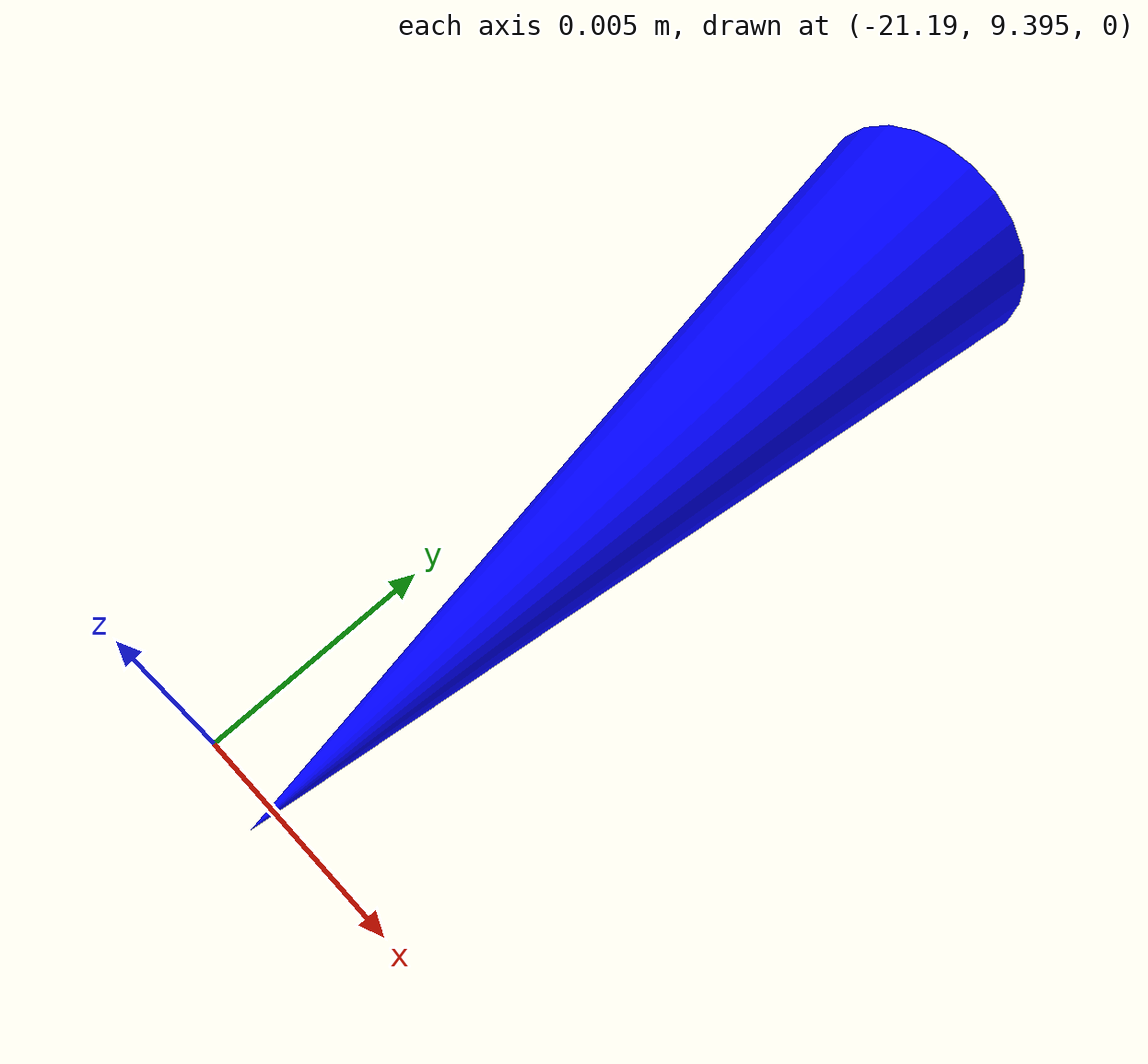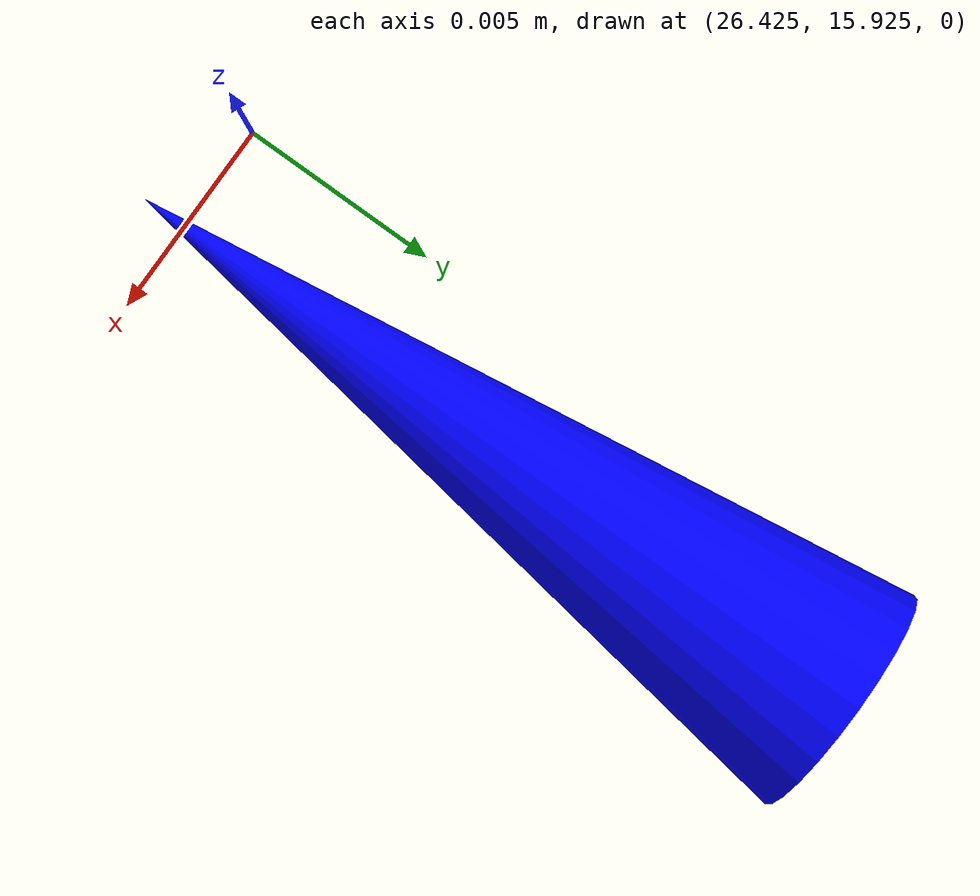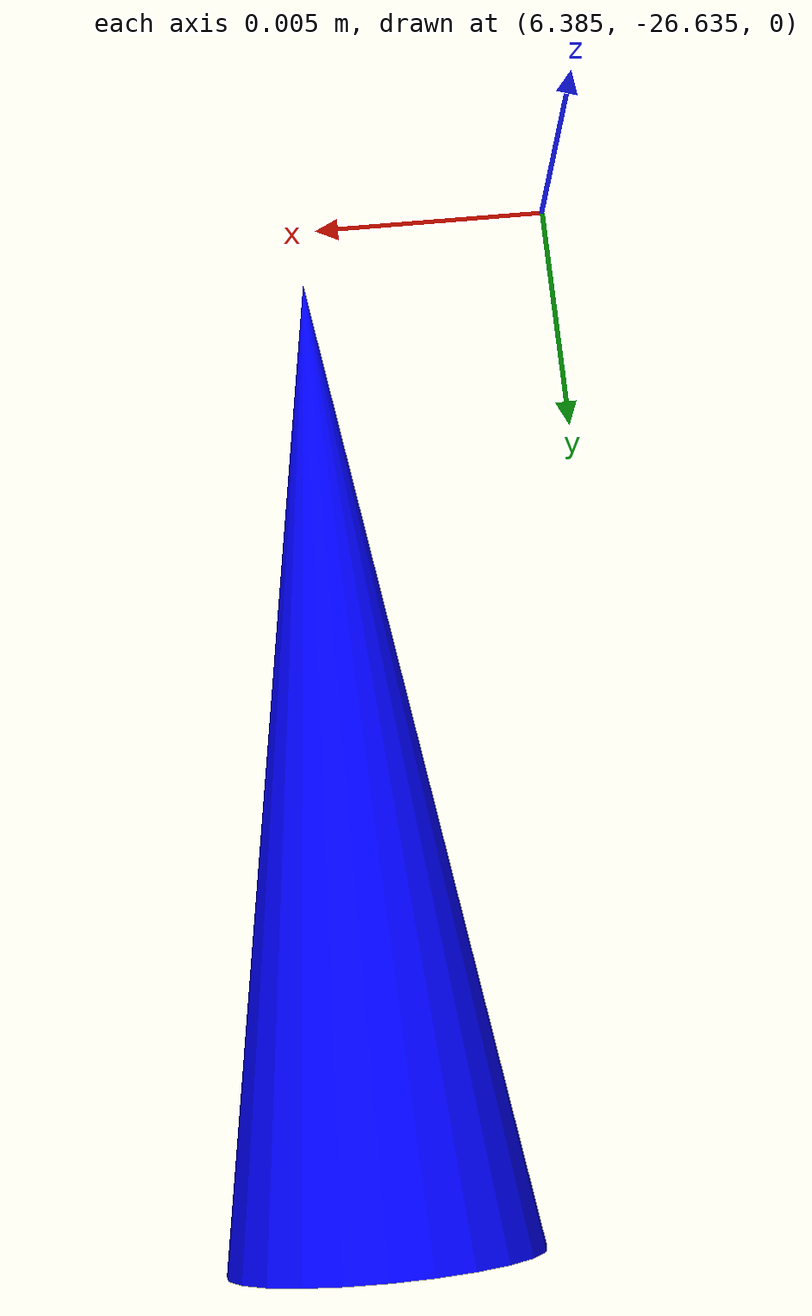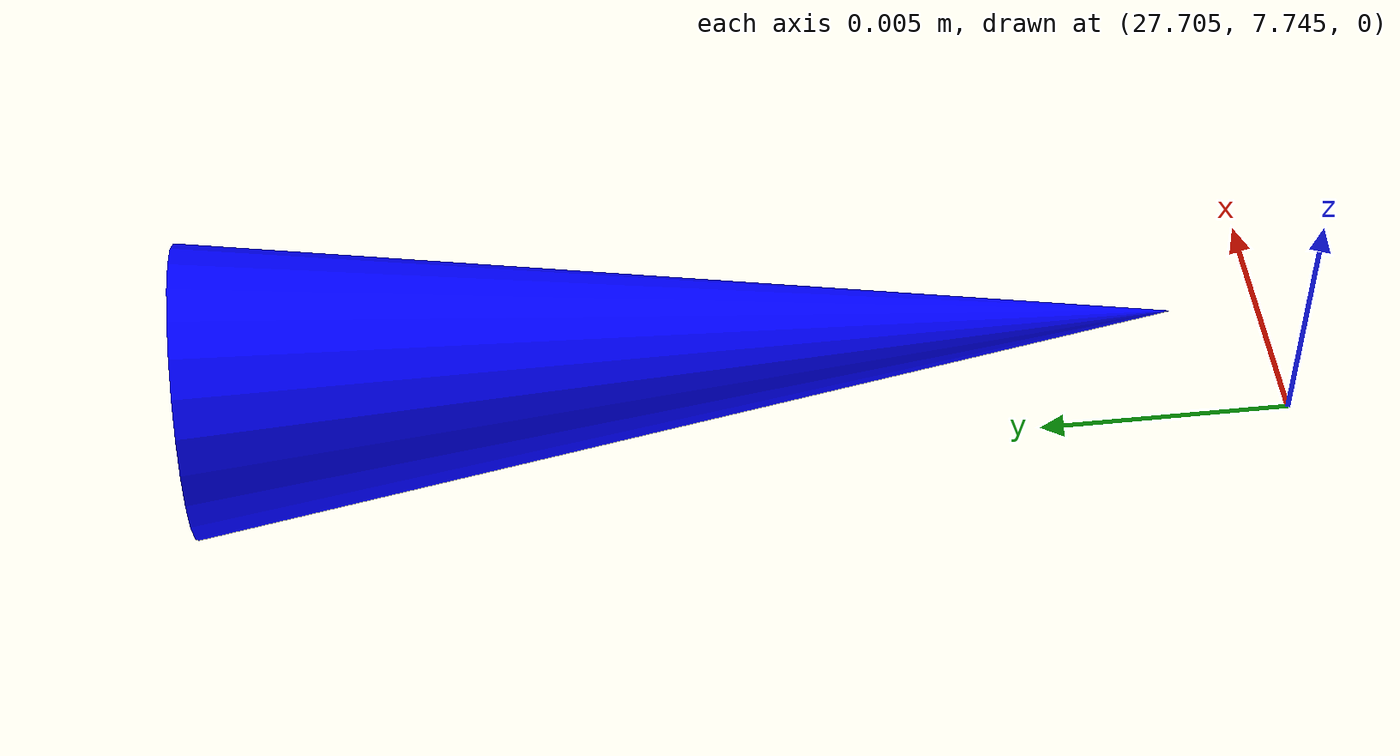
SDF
<?xml version="1.0"?>
  <sdf version='1.9'>
     <model name='cone_0'>
      <link name='cone_0_link'>
        <inertial>
			<mass>0</mass>
			<inertia>
			<ixx>0.166667</ixx>
			<ixy>0</ixy>
			<ixz>0</ixz>
			<iyy>0.166667</iyy>
			<iyz>0</iyz>
			<izz>0.166667</izz>
			</inertia>
		</inertial>
        <collision name='cone_0_collision'>
          <geometry>
            <mesh>
              <uri>/models/cone/meshes/cone.stl</uri>
              <scale>0.001 0.001 0.001</scale>
            </mesh>
          </geometry>
        </collision>
        <visual name='cone_0_visual'>
          <geometry>
            <mesh>
              <uri>/models/cone/meshes/cone.stl</uri>
              <scale>0.001 0.001 0.001</scale>
            </mesh>
          </geometry>
          <material>
            <ambient>1 1 0 1</ambient>
            <diffuse>1 1 0 1</diffuse>
            <specular>1 1 0 1</specular>
          </material>
        </visual>

        <enable_wind>false</enable_wind>
      </link>
      <pose>7.742034689728746 17.705333171677342 0.0 1.57 0 0</pose>
      <static>true</static>
      </model>

     <model name='cone_1'>
      <link name='cone_1_link'>
        <inertial>
			<mass>0</mass>
			<inertia>
			<ixx>0.166667</ixx>
			<ixy>0</ixy>
			<ixz>0</ixz>
			<iyy>0.166667</iyy>
			<iyz>0</iyz>
			<izz>0.166667</izz>
			</inertia>
		</inertial>
        <collision name='cone_1_collision'>
          <geometry>
            <mesh>
              <uri>/models/cone/meshes/cone.stl</uri>
              <scale>0.001 0.001 0.001</scale>
            </mesh>
          </geometry>
        </collision>
        <visual name='cone_1_visual'>
          <geometry>
            <mesh>
              <uri>/models/cone/meshes/cone.stl</uri>
              <scale>0.001 0.001 0.001</scale>
            </mesh>
          </geometry>
          <material>
            <ambient>1 1 0 1</ambient>
            <diffuse>1 1 0 1</diffuse>
            <specular>1 1 0 1</specular>
          </material>
        </visual>

        <enable_wind>false</enable_wind>
      </link>
      <pose>8.447195307557115 17.67379196722483 0.0 1.57 0 0</pose>
      <static>true</static>
      </model>

     <model name='cone_2'>
      <link name='cone_2_link'>
        <inertial>
			<mass>0</mass>
			<inertia>
			<ixx>0.166667</ixx>
			<ixy>0</ixy>
			<ixz>0</ixz>
			<iyy>0.166667</iyy>
			<iyz>0</iyz>
			<izz>0.166667</izz>
			</inertia>
		</inertial>
        <collision name='cone_2_collision'>
          <geometry>
            <mesh>
              <uri>/models/cone/meshes/cone.stl</uri>
              <scale>0.001 0.001 0.001</scale>
            </mesh>
          </geometry>
        </collision>
        <visual name='cone_2_visual'>
          <geometry>
            <mesh>
              <uri>/models/cone/meshes/cone.stl</uri>
              <scale>0.001 0.001 0.001</scale>
            </mesh>
          </geometry>
          <material>
            <ambient>1 1 0 1</ambient>
            <diffuse>1 1 0 1</diffuse>
            <specular>1 1 0 1</specular>
          </material>
        </visual>

        <enable_wind>false</enable_wind>
      </link>
      <pose>10.532398096863757 17.623922906708472 0.0 1.57 0 0</pose>
      <static>true</static>
      </model>

     <model name='cone_3'>
      <link name='cone_3_link'>
        <inertial>
			<mass>0</mass>
			<inertia>
			<ixx>0.166667</ixx>
			<ixy>0</ixy>
			<ixz>0</ixz>
			<iyy>0.166667</iyy>
			<iyz>0</iyz>
			<izz>0.166667</izz>
			</inertia>
		</inertial>
        <collision name='cone_3_collision'>
          <geometry>
            <mesh>
              <uri>/models/cone/meshes/cone.stl</uri>
              <scale>0.001 0.001 0.001</scale>
            </mesh>
          </geometry>
        </collision>
        <visual name='cone_3_visual'>
          <geometry>
            <mesh>
              <uri>/models/cone/meshes/cone.stl</uri>
              <scale>0.001 0.001 0.001</scale>
            </mesh>
          </geometry>
          <material>
            <ambient>1 1 0 1</ambient>
            <diffuse>1 1 0 1</diffuse>
            <specular>1 1 0 1</specular>
          </material>
        </visual>

        <enable_wind>false</enable_wind>
      </link>
      <pose>12.701393381897935 17.49992559988474 0.0 1.57 0 0</pose>
      <static>true</static>
      </model>

     <model name='cone_4'>
      <link name='cone_4_link'>
        <inertial>
			<mass>0</mass>
			<inertia>
			<ixx>0.166667</ixx>
			<ixy>0</ixy>
			<ixz>0</ixz>
			<iyy>0.166667</iyy>
			<iyz>0</iyz>
			<izz>0.166667</izz>
			</inertia>
		</inertial>
        <collision name='cone_4_collision'>
          <geometry>
            <mesh>
              <uri>/models/cone/meshes/cone.stl</uri>
              <scale>0.001 0.001 0.001</scale>
            </mesh>
          </geometry>
        </collision>
        <visual name='cone_4_visual'>
          <geometry>
            <mesh>
              <uri>/models/cone/meshes/cone.stl</uri>
              <scale>0.001 0.001 0.001</scale>
            </mesh>
          </geometry>
          <material>
            <ambient>1 1 0 1</ambient>
            <diffuse>1 1 0 1</diffuse>
            <specular>1 1 0 1</specular>
          </material>
        </visual>

        <enable_wind>false</enable_wind>
      </link>
      <pose>14.490193049256334 17.45396340925669 0.0 1.57 0 0</pose>
      <static>true</static>
      </model>

     <model name='cone_5'>
      <link name='cone_5_link'>
        <inertial>
			<mass>0</mass>
			<inertia>
			<ixx>0.166667</ixx>
			<ixy>0</ixy>
			<ixz>0</ixz>
			<iyy>0.166667</iyy>
			<iyz>0</iyz>
			<izz>0.166667</izz>
			</inertia>
		</inertial>
        <collision name='cone_5_collision'>
          <geometry>
            <mesh>
              <uri>/models/cone/meshes/cone.stl</uri>
              <scale>0.001 0.001 0.001</scale>
            </mesh>
          </geometry>
        </collision>
        <visual name='cone_5_visual'>
          <geometry>
            <mesh>
              <uri>/models/cone/meshes/cone.stl</uri>
              <scale>0.001 0.001 0.001</scale>
            </mesh>
          </geometry>
          <material>
            <ambient>1 1 0 1</ambient>
            <diffuse>1 1 0 1</diffuse>
            <specular>1 1 0 1</specular>
          </material>
        </visual>

        <enable_wind>false</enable_wind>
      </link>
      <pose>16.65316187555028 17.1900486334083 0.0 1.57 0 0</pose>
      <static>true</static>
      </model>

     <model name='cone_6'>
      <link name='cone_6_link'>
        <inertial>
			<mass>0</mass>
			<inertia>
			<ixx>0.166667</ixx>
			<ixy>0</ixy>
			<ixz>0</ixz>
			<iyy>0.166667</iyy>
			<iyz>0</iyz>
			<izz>0.166667</izz>
			</inertia>
		</inertial>
        <collision name='cone_6_collision'>
          <geometry>
            <mesh>
              <uri>/models/cone/meshes/cone.stl</uri>
              <scale>0.001 0.001 0.001</scale>
            </mesh>
          </geometry>
        </collision>
        <visual name='cone_6_visual'>
          <geometry>
            <mesh>
              <uri>/models/cone/meshes/cone.stl</uri>
              <scale>0.001 0.001 0.001</scale>
            </mesh>
          </geometry>
          <material>
            <ambient>1 1 0 1</ambient>
            <diffuse>1 1 0 1</diffuse>
            <specular>1 1 0 1</specular>
          </material>
        </visual>

        <enable_wind>false</enable_wind>
      </link>
      <pose>18.550547663514145 16.922206102204076 0.0 1.57 0 0</pose>
      <static>true</static>
      </model>

     <model name='cone_7'>
      <link name='cone_7_link'>
        <inertial>
			<mass>0</mass>
			<inertia>
			<ixx>0.166667</ixx>
			<ixy>0</ixy>
			<ixz>0</ixz>
			<iyy>0.166667</iyy>
			<iyz>0</iyz>
			<izz>0.166667</izz>
			</inertia>
		</inertial>
        <collision name='cone_7_collision'>
          <geometry>
            <mesh>
              <uri>/models/cone/meshes/cone.stl</uri>
              <scale>0.001 0.001 0.001</scale>
            </mesh>
          </geometry>
        </collision>
        <visual name='cone_7_visual'>
          <geometry>
            <mesh>
              <uri>/models/cone/meshes/cone.stl</uri>
              <scale>0.001 0.001 0.001</scale>
            </mesh>
          </geometry>
          <material>
            <ambient>1 1 0 1</ambient>
            <diffuse>1 1 0 1</diffuse>
            <specular>1 1 0 1</specular>
          </material>
        </visual>

        <enable_wind>false</enable_wind>
      </link>
      <pose>20.040591303650867 16.537257181000463 0.0 1.57 0 0</pose>
      <static>true</static>
      </model>

     <model name='cone_8'>
      <link name='cone_8_link'>
        <inertial>
			<mass>0</mass>
			<inertia>
			<ixx>0.166667</ixx>
			<ixy>0</ixy>
			<ixz>0</ixz>
			<iyy>0.166667</iyy>
			<iyz>0</iyz>
			<izz>0.166667</izz>
			</inertia>
		</inertial>
        <collision name='cone_8_collision'>
          <geometry>
            <mesh>
              <uri>/models/cone/meshes/cone.stl</uri>
              <scale>0.001 0.001 0.001</scale>
            </mesh>
          </geometry>
        </collision>
        <visual name='cone_8_visual'>
          <geometry>
            <mesh>
              <uri>/models/cone/meshes/cone.stl</uri>
              <scale>0.001 0.001 0.001</scale>
            </mesh>
          </geometry>
          <material>
            <ambient>1 1 0 1</ambient>
            <diffuse>1 1 0 1</diffuse>
            <specular>1 1 0 1</specular>
          </material>
        </visual>

        <enable_wind>false</enable_wind>
      </link>
      <pose>21.92312266046239 15.900208936524145 0.0 1.57 0 0</pose>
      <static>true</static>
      </model>

     <model name='cone_9'>
      <link name='cone_9_link'>
        <inertial>
			<mass>0</mass>
			<inertia>
			<ixx>0.166667</ixx>
			<ixy>0</ixy>
			<ixz>0</ixz>
			<iyy>0.166667</iyy>
			<iyz>0</iyz>
			<izz>0.166667</izz>
			</inertia>
		</inertial>
        <collision name='cone_9_collision'>
          <geometry>
            <mesh>
              <uri>/models/cone/meshes/cone.stl</uri>
              <scale>0.001 0.001 0.001</scale>
            </mesh>
          </geometry>
        </collision>
        <visual name='cone_9_visual'>
          <geometry>
            <mesh>
              <uri>/models/cone/meshes/cone.stl</uri>
              <scale>0.001 0.001 0.001</scale>
            </mesh>
          </geometry>
          <material>
            <ambient>1 1 0 1</ambient>
            <diffuse>1 1 0 1</diffuse>
            <specular>1 1 0 1</specular>
          </material>
        </visual>

        <enable_wind>false</enable_wind>
      </link>
      <pose>23.606309382264147 15.20658768255686 0.0 1.57 0 0</pose>
      <static>true</static>
      </model>

     <model name='cone_10'>
      <link name='cone_10_link'>
        <inertial>
			<mass>0</mass>
			<inertia>
			<ixx>0.166667</ixx>
			<ixy>0</ixy>
			<ixz>0</ixz>
			<iyy>0.166667</iyy>
			<iyz>0</iyz>
			<izz>0.166667</izz>
			</inertia>
		</inertial>
        <collision name='cone_10_collision'>
          <geometry>
            <mesh>
              <uri>/models/cone/meshes/cone.stl</uri>
              <scale>0.001 0.001 0.001</scale>
            </mesh>
          </geometry>
        </collision>
        <visual name='cone_10_visual'>
          <geometry>
            <mesh>
              <uri>/models/cone/meshes/cone.stl</uri>
              <scale>0.001 0.001 0.001</scale>
            </mesh>
          </geometry>
          <material>
            <ambient>1 1 0 1</ambient>
            <diffuse>1 1 0 1</diffuse>
            <specular>1 1 0 1</specular>
          </material>
        </visual>

        <enable_wind>false</enable_wind>
      </link>
      <pose>24.751217524353994 14.442515455078833 0.0 1.57 0 0</pose>
      <static>true</static>
      </model>

     <model name='cone_11'>
      <link name='cone_11_link'>
        <inertial>
			<mass>0</mass>
			<inertia>
			<ixx>0.166667</ixx>
			<ixy>0</ixy>
			<ixz>0</ixz>
			<iyy>0.166667</iyy>
			<iyz>0</iyz>
			<izz>0.166667</izz>
			</inertia>
		</inertial>
        <collision name='cone_11_collision'>
          <geometry>
            <mesh>
              <uri>/models/cone/meshes/cone.stl</uri>
              <scale>0.001 0.001 0.001</scale>
            </mesh>
          </geometry>
        </collision>
        <visual name='cone_11_visual'>
          <geometry>
            <mesh>
              <uri>/models/cone/meshes/cone.stl</uri>
              <scale>0.001 0.001 0.001</scale>
            </mesh>
          </geometry>
          <material>
            <ambient>1 1 0 1</ambient>
            <diffuse>1 1 0 1</diffuse>
            <specular>1 1 0 1</specular>
          </material>
        </visual>

        <enable_wind>false</enable_wind>
      </link>
      <pose>25.611662165467273 13.138141904663794 0.0 1.57 0 0</pose>
      <static>true</static>
      </model>

     <model name='cone_12'>
      <link name='cone_12_link'>
        <inertial>
			<mass>0</mass>
			<inertia>
			<ixx>0.166667</ixx>
			<ixy>0</ixy>
			<ixz>0</ixz>
			<iyy>0.166667</iyy>
			<iyz>0</iyz>
			<izz>0.166667</izz>
			</inertia>
		</inertial>
        <collision name='cone_12_collision'>
          <geometry>
            <mesh>
              <uri>/models/cone/meshes/cone.stl</uri>
              <scale>0.001 0.001 0.001</scale>
            </mesh>
          </geometry>
        </collision>
        <visual name='cone_12_visual'>
          <geometry>
            <mesh>
              <uri>/models/cone/meshes/cone.stl</uri>
              <scale>0.001 0.001 0.001</scale>
            </mesh>
          </geometry>
          <material>
            <ambient>1 1 0 1</ambient>
            <diffuse>1 1 0 1</diffuse>
            <specular>1 1 0 1</specular>
          </material>
        </visual>

        <enable_wind>false</enable_wind>
      </link>
      <pose>26.133718745057116 11.475116811585181 0.0 1.57 0 0</pose>
      <static>true</static>
      </model>

     <model name='cone_13'>
      <link name='cone_13_link'>
        <inertial>
			<mass>0</mass>
			<inertia>
			<ixx>0.166667</ixx>
			<ixy>0</ixy>
			<ixz>0</ixz>
			<iyy>0.166667</iyy>
			<iyz>0</iyz>
			<izz>0.166667</izz>
			</inertia>
		</inertial>
        <collision name='cone_13_collision'>
          <geometry>
            <mesh>
              <uri>/models/cone/meshes/cone.stl</uri>
              <scale>0.001 0.001 0.001</scale>
            </mesh>
          </geometry>
        </collision>
        <visual name='cone_13_visual'>
          <geometry>
            <mesh>
              <uri>/models/cone/meshes/cone.stl</uri>
              <scale>0.001 0.001 0.001</scale>
            </mesh>
          </geometry>
          <material>
            <ambient>1 1 0 1</ambient>
            <diffuse>1 1 0 1</diffuse>
            <specular>1 1 0 1</specular>
          </material>
        </visual>

        <enable_wind>false</enable_wind>
      </link>
      <pose>26.31678072625829 9.908749662232154 0.0 1.57 0 0</pose>
      <static>true</static>
      </model>

     <model name='cone_14'>
      <link name='cone_14_link'>
        <inertial>
			<mass>0</mass>
			<inertia>
			<ixx>0.166667</ixx>
			<ixy>0</ixy>
			<ixz>0</ixz>
			<iyy>0.166667</iyy>
			<iyz>0</iyz>
			<izz>0.166667</izz>
			</inertia>
		</inertial>
        <collision name='cone_14_collision'>
          <geometry>
            <mesh>
              <uri>/models/cone/meshes/cone.stl</uri>
              <scale>0.001 0.001 0.001</scale>
            </mesh>
          </geometry>
        </collision>
        <visual name='cone_14_visual'>
          <geometry>
            <mesh>
              <uri>/models/cone/meshes/cone.stl</uri>
              <scale>0.001 0.001 0.001</scale>
            </mesh>
          </geometry>
          <material>
            <ambient>1 1 0 1</ambient>
            <diffuse>1 1 0 1</diffuse>
            <specular>1 1 0 1</specular>
          </material>
        </visual>

        <enable_wind>false</enable_wind>
      </link>
      <pose>25.95169817620946 8.38755692083811 0.0 1.57 0 0</pose>
      <static>true</static>
      </model>

     <model name='cone_15'>
      <link name='cone_15_link'>
        <inertial>
			<mass>0</mass>
			<inertia>
			<ixx>0.166667</ixx>
			<ixy>0</ixy>
			<ixz>0</ixz>
			<iyy>0.166667</iyy>
			<iyz>0</iyz>
			<izz>0.166667</izz>
			</inertia>
		</inertial>
        <collision name='cone_15_collision'>
          <geometry>
            <mesh>
              <uri>/models/cone/meshes/cone.stl</uri>
              <scale>0.001 0.001 0.001</scale>
            </mesh>
          </geometry>
        </collision>
        <visual name='cone_15_visual'>
          <geometry>
            <mesh>
              <uri>/models/cone/meshes/cone.stl</uri>
              <scale>0.001 0.001 0.001</scale>
            </mesh>
          </geometry>
          <material>
            <ambient>1 1 0 1</ambient>
            <diffuse>1 1 0 1</diffuse>
            <specular>1 1 0 1</specular>
          </material>
        </visual>

        <enable_wind>false</enable_wind>
      </link>
      <pose>25.004358546082507 7.375549016785376 0.0 1.57 0 0</pose>
      <static>true</static>
      </model>

     <model name='cone_16'>
      <link name='cone_16_link'>
        <inertial>
			<mass>0</mass>
			<inertia>
			<ixx>0.166667</ixx>
			<ixy>0</ixy>
			<ixz>0</ixz>
			<iyy>0.166667</iyy>
			<iyz>0</iyz>
			<izz>0.166667</izz>
			</inertia>
		</inertial>
        <collision name='cone_16_collision'>
          <geometry>
            <mesh>
              <uri>/models/cone/meshes/cone.stl</uri>
              <scale>0.001 0.001 0.001</scale>
            </mesh>
          </geometry>
        </collision>
        <visual name='cone_16_visual'>
          <geometry>
            <mesh>
              <uri>/models/cone/meshes/cone.stl</uri>
              <scale>0.001 0.001 0.001</scale>
            </mesh>
          </geometry>
          <material>
            <ambient>1 1 0 1</ambient>
            <diffuse>1 1 0 1</diffuse>
            <specular>1 1 0 1</specular>
          </material>
        </visual>

        <enable_wind>false</enable_wind>
      </link>
      <pose>23.486972681824696 6.0377861841437745 0.0 1.57 0 0</pose>
      <static>true</static>
      </model>

     <model name='cone_17'>
      <link name='cone_17_link'>
        <inertial>
			<mass>0</mass>
			<inertia>
			<ixx>0.166667</ixx>
			<ixy>0</ixy>
			<ixz>0</ixz>
			<iyy>0.166667</iyy>
			<iyz>0</iyz>
			<izz>0.166667</izz>
			</inertia>
		</inertial>
        <collision name='cone_17_collision'>
          <geometry>
            <mesh>
              <uri>/models/cone/meshes/cone.stl</uri>
              <scale>0.001 0.001 0.001</scale>
            </mesh>
          </geometry>
        </collision>
        <visual name='cone_17_visual'>
          <geometry>
            <mesh>
              <uri>/models/cone/meshes/cone.stl</uri>
              <scale>0.001 0.001 0.001</scale>
            </mesh>
          </geometry>
          <material>
            <ambient>1 1 0 1</ambient>
            <diffuse>1 1 0 1</diffuse>
            <specular>1 1 0 1</specular>
          </material>
        </visual>

        <enable_wind>false</enable_wind>
      </link>
      <pose>22.11114107782079 4.860138784241431 0.0 1.57 0 0</pose>
      <static>true</static>
      </model>

     <model name='cone_18'>
      <link name='cone_18_link'>
        <inertial>
			<mass>0</mass>
			<inertia>
			<ixx>0.166667</ixx>
			<ixy>0</ixy>
			<ixz>0</ixz>
			<iyy>0.166667</iyy>
			<iyz>0</iyz>
			<izz>0.166667</izz>
			</inertia>
		</inertial>
        <collision name='cone_18_collision'>
          <geometry>
            <mesh>
              <uri>/models/cone/meshes/cone.stl</uri>
              <scale>0.001 0.001 0.001</scale>
            </mesh>
          </geometry>
        </collision>
        <visual name='cone_18_visual'>
          <geometry>
            <mesh>
              <uri>/models/cone/meshes/cone.stl</uri>
              <scale>0.001 0.001 0.001</scale>
            </mesh>
          </geometry>
          <material>
            <ambient>1 1 0 1</ambient>
            <diffuse>1 1 0 1</diffuse>
            <specular>1 1 0 1</specular>
          </material>
        </visual>

        <enable_wind>false</enable_wind>
      </link>
      <pose>20.557459132020007 4.063882909607642 0.0 1.57 0 0</pose>
      <static>true</static>
      </model>

     <model name='cone_19'>
      <link name='cone_19_link'>
        <inertial>
			<mass>0</mass>
			<inertia>
			<ixx>0.166667</ixx>
			<ixy>0</ixy>
			<ixz>0</ixz>
			<iyy>0.166667</iyy>
			<iyz>0</iyz>
			<izz>0.166667</izz>
			</inertia>
		</inertial>
        <collision name='cone_19_collision'>
          <geometry>
            <mesh>
              <uri>/models/cone/meshes/cone.stl</uri>
              <scale>0.001 0.001 0.001</scale>
            </mesh>
          </geometry>
        </collision>
        <visual name='cone_19_visual'>
          <geometry>
            <mesh>
              <uri>/models/cone/meshes/cone.stl</uri>
              <scale>0.001 0.001 0.001</scale>
            </mesh>
          </geometry>
          <material>
            <ambient>1 1 0 1</ambient>
            <diffuse>1 1 0 1</diffuse>
            <specular>1 1 0 1</specular>
          </material>
        </visual>

        <enable_wind>false</enable_wind>
      </link>
      <pose>18.608921686951646 3.429864202332251 0.0 1.57 0 0</pose>
      <static>true</static>
      </model>

     <model name='cone_20'>
      <link name='cone_20_link'>
        <inertial>
			<mass>0</mass>
			<inertia>
			<ixx>0.166667</ixx>
			<ixy>0</ixy>
			<ixz>0</ixz>
			<iyy>0.166667</iyy>
			<iyz>0</iyz>
			<izz>0.166667</izz>
			</inertia>
		</inertial>
        <collision name='cone_20_collision'>
          <geometry>
            <mesh>
              <uri>/models/cone/meshes/cone.stl</uri>
              <scale>0.001 0.001 0.001</scale>
            </mesh>
          </geometry>
        </collision>
        <visual name='cone_20_visual'>
          <geometry>
            <mesh>
              <uri>/models/cone/meshes/cone.stl</uri>
              <scale>0.001 0.001 0.001</scale>
            </mesh>
          </geometry>
          <material>
            <ambient>1 1 0 1</ambient>
            <diffuse>1 1 0 1</diffuse>
            <specular>1 1 0 1</specular>
          </material>
        </visual>

        <enable_wind>false</enable_wind>
      </link>
      <pose>16.603126017395983 2.748691259217017 0.0 1.57 0 0</pose>
      <static>true</static>
      </model>

     <model name='cone_21'>
      <link name='cone_21_link'>
        <inertial>
			<mass>0</mass>
			<inertia>
			<ixx>0.166667</ixx>
			<ixy>0</ixy>
			<ixz>0</ixz>
			<iyy>0.166667</iyy>
			<iyz>0</iyz>
			<izz>0.166667</izz>
			</inertia>
		</inertial>
        <collision name='cone_21_collision'>
          <geometry>
            <mesh>
              <uri>/models/cone/meshes/cone.stl</uri>
              <scale>0.001 0.001 0.001</scale>
            </mesh>
          </geometry>
        </collision>
        <visual name='cone_21_visual'>
          <geometry>
            <mesh>
              <uri>/models/cone/meshes/cone.stl</uri>
              <scale>0.001 0.001 0.001</scale>
            </mesh>
          </geometry>
          <material>
            <ambient>1 1 0 1</ambient>
            <diffuse>1 1 0 1</diffuse>
            <specular>1 1 0 1</specular>
          </material>
        </visual>

        <enable_wind>false</enable_wind>
      </link>
      <pose>14.747824732605944 2.3823143823859625 0.0 1.57 0 0</pose>
      <static>true</static>
      </model>

     <model name='cone_22'>
      <link name='cone_22_link'>
        <inertial>
			<mass>0</mass>
			<inertia>
			<ixx>0.166667</ixx>
			<ixy>0</ixy>
			<ixz>0</ixz>
			<iyy>0.166667</iyy>
			<iyz>0</iyz>
			<izz>0.166667</izz>
			</inertia>
		</inertial>
        <collision name='cone_22_collision'>
          <geometry>
            <mesh>
              <uri>/models/cone/meshes/cone.stl</uri>
              <scale>0.001 0.001 0.001</scale>
            </mesh>
          </geometry>
        </collision>
        <visual name='cone_22_visual'>
          <geometry>
            <mesh>
              <uri>/models/cone/meshes/cone.stl</uri>
              <scale>0.001 0.001 0.001</scale>
            </mesh>
          </geometry>
          <material>
            <ambient>1 1 0 1</ambient>
            <diffuse>1 1 0 1</diffuse>
            <specular>1 1 0 1</specular>
          </material>
        </visual>

        <enable_wind>false</enable_wind>
      </link>
      <pose>13.096530405823717 2.352552877259009 0.0 1.57 0 0</pose>
      <static>true</static>
      </model>

     <model name='cone_23'>
      <link name='cone_23_link'>
        <inertial>
			<mass>0</mass>
			<inertia>
			<ixx>0.166667</ixx>
			<ixy>0</ixy>
			<ixz>0</ixz>
			<iyy>0.166667</iyy>
			<iyz>0</iyz>
			<izz>0.166667</izz>
			</inertia>
		</inertial>
        <collision name='cone_23_collision'>
          <geometry>
            <mesh>
              <uri>/models/cone/meshes/cone.stl</uri>
              <scale>0.001 0.001 0.001</scale>
            </mesh>
          </geometry>
        </collision>
        <visual name='cone_23_visual'>
          <geometry>
            <mesh>
              <uri>/models/cone/meshes/cone.stl</uri>
              <scale>0.001 0.001 0.001</scale>
            </mesh>
          </geometry>
          <material>
            <ambient>1 1 0 1</ambient>
            <diffuse>1 1 0 1</diffuse>
            <specular>1 1 0 1</specular>
          </material>
        </visual>

        <enable_wind>false</enable_wind>
      </link>
      <pose>11.541059748475083 2.749478612732642 0.0 1.57 0 0</pose>
      <static>true</static>
      </model>

     <model name='cone_24'>
      <link name='cone_24_link'>
        <inertial>
			<mass>0</mass>
			<inertia>
			<ixx>0.166667</ixx>
			<ixy>0</ixy>
			<ixz>0</ixz>
			<iyy>0.166667</iyy>
			<iyz>0</iyz>
			<izz>0.166667</izz>
			</inertia>
		</inertial>
        <collision name='cone_24_collision'>
          <geometry>
            <mesh>
              <uri>/models/cone/meshes/cone.stl</uri>
              <scale>0.001 0.001 0.001</scale>
            </mesh>
          </geometry>
        </collision>
        <visual name='cone_24_visual'>
          <geometry>
            <mesh>
              <uri>/models/cone/meshes/cone.stl</uri>
              <scale>0.001 0.001 0.001</scale>
            </mesh>
          </geometry>
          <material>
            <ambient>1 1 0 1</ambient>
            <diffuse>1 1 0 1</diffuse>
            <specular>1 1 0 1</specular>
          </material>
        </visual>

        <enable_wind>false</enable_wind>
      </link>
      <pose>9.63776137048436 3.612327657532447 0.0 1.57 0 0</pose>
      <static>true</static>
      </model>

     <model name='cone_25'>
      <link name='cone_25_link'>
        <inertial>
			<mass>0</mass>
			<inertia>
			<ixx>0.166667</ixx>
			<ixy>0</ixy>
			<ixz>0</ixz>
			<iyy>0.166667</iyy>
			<iyz>0</iyz>
			<izz>0.166667</izz>
			</inertia>
		</inertial>
        <collision name='cone_25_collision'>
          <geometry>
            <mesh>
              <uri>/models/cone/meshes/cone.stl</uri>
              <scale>0.001 0.001 0.001</scale>
            </mesh>
          </geometry>
        </collision>
        <visual name='cone_25_visual'>
          <geometry>
            <mesh>
              <uri>/models/cone/meshes/cone.stl</uri>
              <scale>0.001 0.001 0.001</scale>
            </mesh>
          </geometry>
          <material>
            <ambient>1 1 0 1</ambient>
            <diffuse>1 1 0 1</diffuse>
            <specular>1 1 0 1</specular>
          </material>
        </visual>

        <enable_wind>false</enable_wind>
      </link>
      <pose>8.051291529480944 4.86127976019358 0.0 1.57 0 0</pose>
      <static>true</static>
      </model>

     <model name='cone_26'>
      <link name='cone_26_link'>
        <inertial>
			<mass>0</mass>
			<inertia>
			<ixx>0.166667</ixx>
			<ixy>0</ixy>
			<ixz>0</ixz>
			<iyy>0.166667</iyy>
			<iyz>0</iyz>
			<izz>0.166667</izz>
			</inertia>
		</inertial>
        <collision name='cone_26_collision'>
          <geometry>
            <mesh>
              <uri>/models/cone/meshes/cone.stl</uri>
              <scale>0.001 0.001 0.001</scale>
            </mesh>
          </geometry>
        </collision>
        <visual name='cone_26_visual'>
          <geometry>
            <mesh>
              <uri>/models/cone/meshes/cone.stl</uri>
              <scale>0.001 0.001 0.001</scale>
            </mesh>
          </geometry>
          <material>
            <ambient>1 1 0 1</ambient>
            <diffuse>1 1 0 1</diffuse>
            <specular>1 1 0 1</specular>
          </material>
        </visual>

        <enable_wind>false</enable_wind>
      </link>
      <pose>6.723178641144762 6.72584045965647 0.0 1.57 0 0</pose>
      <static>true</static>
      </model>

     <model name='cone_27'>
      <link name='cone_27_link'>
        <inertial>
			<mass>0</mass>
			<inertia>
			<ixx>0.166667</ixx>
			<ixy>0</ixy>
			<ixz>0</ixz>
			<iyy>0.166667</iyy>
			<iyz>0</iyz>
			<izz>0.166667</izz>
			</inertia>
		</inertial>
        <collision name='cone_27_collision'>
          <geometry>
            <mesh>
              <uri>/models/cone/meshes/cone.stl</uri>
              <scale>0.001 0.001 0.001</scale>
            </mesh>
          </geometry>
        </collision>
        <visual name='cone_27_visual'>
          <geometry>
            <mesh>
              <uri>/models/cone/meshes/cone.stl</uri>
              <scale>0.001 0.001 0.001</scale>
            </mesh>
          </geometry>
          <material>
            <ambient>1 1 0 1</ambient>
            <diffuse>1 1 0 1</diffuse>
            <specular>1 1 0 1</specular>
          </material>
        </visual>

        <enable_wind>false</enable_wind>
      </link>
      <pose>5.220282284562121 8.289879308533424 0.0 1.57 0 0</pose>
      <static>true</static>
      </model>

     <model name='cone_28'>
      <link name='cone_28_link'>
        <inertial>
			<mass>0</mass>
			<inertia>
			<ixx>0.166667</ixx>
			<ixy>0</ixy>
			<ixz>0</ixz>
			<iyy>0.166667</iyy>
			<iyz>0</iyz>
			<izz>0.166667</izz>
			</inertia>
		</inertial>
        <collision name='cone_28_collision'>
          <geometry>
            <mesh>
              <uri>/models/cone/meshes/cone.stl</uri>
              <scale>0.001 0.001 0.001</scale>
            </mesh>
          </geometry>
        </collision>
        <visual name='cone_28_visual'>
          <geometry>
            <mesh>
              <uri>/models/cone/meshes/cone.stl</uri>
              <scale>0.001 0.001 0.001</scale>
            </mesh>
          </geometry>
          <material>
            <ambient>1 1 0 1</ambient>
            <diffuse>1 1 0 1</diffuse>
            <specular>1 1 0 1</specular>
          </material>
        </visual>

        <enable_wind>false</enable_wind>
      </link>
      <pose>3.676563332621584 9.704400525879615 0.0 1.57 0 0</pose>
      <static>true</static>
      </model>

     <model name='cone_29'>
      <link name='cone_29_link'>
        <inertial>
			<mass>0</mass>
			<inertia>
			<ixx>0.166667</ixx>
			<ixy>0</ixy>
			<ixz>0</ixz>
			<iyy>0.166667</iyy>
			<iyz>0</iyz>
			<izz>0.166667</izz>
			</inertia>
		</inertial>
        <collision name='cone_29_collision'>
          <geometry>
            <mesh>
              <uri>/models/cone/meshes/cone.stl</uri>
              <scale>0.001 0.001 0.001</scale>
            </mesh>
          </geometry>
        </collision>
        <visual name='cone_29_visual'>
          <geometry>
            <mesh>
              <uri>/models/cone/meshes/cone.stl</uri>
              <scale>0.001 0.001 0.001</scale>
            </mesh>
          </geometry>
          <material>
            <ambient>1 1 0 1</ambient>
            <diffuse>1 1 0 1</diffuse>
            <specular>1 1 0 1</specular>
          </material>
        </visual>

        <enable_wind>false</enable_wind>
      </link>
      <pose>1.5771283310098745 10.729925046753637 0.0 1.57 0 0</pose>
      <static>true</static>
      </model>

     <model name='cone_30'>
      <link name='cone_30_link'>
        <inertial>
			<mass>0</mass>
			<inertia>
			<ixx>0.166667</ixx>
			<ixy>0</ixy>
			<ixz>0</ixz>
			<iyy>0.166667</iyy>
			<iyz>0</iyz>
			<izz>0.166667</izz>
			</inertia>
		</inertial>
        <collision name='cone_30_collision'>
          <geometry>
            <mesh>
              <uri>/models/cone/meshes/cone.stl</uri>
              <scale>0.001 0.001 0.001</scale>
            </mesh>
          </geometry>
        </collision>
        <visual name='cone_30_visual'>
          <geometry>
            <mesh>
              <uri>/models/cone/meshes/cone.stl</uri>
              <scale>0.001 0.001 0.001</scale>
            </mesh>
          </geometry>
          <material>
            <ambient>1 1 0 1</ambient>
            <diffuse>1 1 0 1</diffuse>
            <specular>1 1 0 1</specular>
          </material>
        </visual>

        <enable_wind>false</enable_wind>
      </link>
      <pose>-0.8690063793020151 10.829716382813208 0.0 1.57 0 0</pose>
      <static>true</static>
      </model>

     <model name='cone_31'>
      <link name='cone_31_link'>
        <inertial>
			<mass>0</mass>
			<inertia>
			<ixx>0.166667</ixx>
			<ixy>0</ixy>
			<ixz>0</ixz>
			<iyy>0.166667</iyy>
			<iyz>0</iyz>
			<izz>0.166667</izz>
			</inertia>
		</inertial>
        <collision name='cone_31_collision'>
          <geometry>
            <mesh>
              <uri>/models/cone/meshes/cone.stl</uri>
              <scale>0.001 0.001 0.001</scale>
            </mesh>
          </geometry>
        </collision>
        <visual name='cone_31_visual'>
          <geometry>
            <mesh>
              <uri>/models/cone/meshes/cone.stl</uri>
              <scale>0.001 0.001 0.001</scale>
            </mesh>
          </geometry>
          <material>
            <ambient>1 1 0 1</ambient>
            <diffuse>1 1 0 1</diffuse>
            <specular>1 1 0 1</specular>
          </material>
        </visual>

        <enable_wind>false</enable_wind>
      </link>
      <pose>-3.100106175597181 10.248561940979712 0.0 1.57 0 0</pose>
      <static>true</static>
      </model>

     <model name='cone_32'>
      <link name='cone_32_link'>
        <inertial>
			<mass>0</mass>
			<inertia>
			<ixx>0.166667</ixx>
			<ixy>0</ixy>
			<ixz>0</ixz>
			<iyy>0.166667</iyy>
			<iyz>0</iyz>
			<izz>0.166667</izz>
			</inertia>
		</inertial>
        <collision name='cone_32_collision'>
          <geometry>
            <mesh>
              <uri>/models/cone/meshes/cone.stl</uri>
              <scale>0.001 0.001 0.001</scale>
            </mesh>
          </geometry>
        </collision>
        <visual name='cone_32_visual'>
          <geometry>
            <mesh>
              <uri>/models/cone/meshes/cone.stl</uri>
              <scale>0.001 0.001 0.001</scale>
            </mesh>
          </geometry>
          <material>
            <ambient>1 1 0 1</ambient>
            <diffuse>1 1 0 1</diffuse>
            <specular>1 1 0 1</specular>
          </material>
        </visual>

        <enable_wind>false</enable_wind>
      </link>
      <pose>-4.84554303472804 9.134345708679907 0.0 1.57 0 0</pose>
      <static>true</static>
      </model>

     <model name='cone_33'>
      <link name='cone_33_link'>
        <inertial>
			<mass>0</mass>
			<inertia>
			<ixx>0.166667</ixx>
			<ixy>0</ixy>
			<ixz>0</ixz>
			<iyy>0.166667</iyy>
			<iyz>0</iyz>
			<izz>0.166667</izz>
			</inertia>
		</inertial>
        <collision name='cone_33_collision'>
          <geometry>
            <mesh>
              <uri>/models/cone/meshes/cone.stl</uri>
              <scale>0.001 0.001 0.001</scale>
            </mesh>
          </geometry>
        </collision>
        <visual name='cone_33_visual'>
          <geometry>
            <mesh>
              <uri>/models/cone/meshes/cone.stl</uri>
              <scale>0.001 0.001 0.001</scale>
            </mesh>
          </geometry>
          <material>
            <ambient>1 1 0 1</ambient>
            <diffuse>1 1 0 1</diffuse>
            <specular>1 1 0 1</specular>
          </material>
        </visual>

        <enable_wind>false</enable_wind>
      </link>
      <pose>-6.33364117925929 7.5075188501594 0.0 1.57 0 0</pose>
      <static>true</static>
      </model>

     <model name='cone_34'>
      <link name='cone_34_link'>
        <inertial>
			<mass>0</mass>
			<inertia>
			<ixx>0.166667</ixx>
			<ixy>0</ixy>
			<ixz>0</ixz>
			<iyy>0.166667</iyy>
			<iyz>0</iyz>
			<izz>0.166667</izz>
			</inertia>
		</inertial>
        <collision name='cone_34_collision'>
          <geometry>
            <mesh>
              <uri>/models/cone/meshes/cone.stl</uri>
              <scale>0.001 0.001 0.001</scale>
            </mesh>
          </geometry>
        </collision>
        <visual name='cone_34_visual'>
          <geometry>
            <mesh>
              <uri>/models/cone/meshes/cone.stl</uri>
              <scale>0.001 0.001 0.001</scale>
            </mesh>
          </geometry>
          <material>
            <ambient>1 1 0 1</ambient>
            <diffuse>1 1 0 1</diffuse>
            <specular>1 1 0 1</specular>
          </material>
        </visual>

        <enable_wind>false</enable_wind>
      </link>
      <pose>-7.067241795714368 5.476565633606666 0.0 1.57 0 0</pose>
      <static>true</static>
      </model>

     <model name='cone_35'>
      <link name='cone_35_link'>
        <inertial>
			<mass>0</mass>
			<inertia>
			<ixx>0.166667</ixx>
			<ixy>0</ixy>
			<ixz>0</ixz>
			<iyy>0.166667</iyy>
			<iyz>0</iyz>
			<izz>0.166667</izz>
			</inertia>
		</inertial>
        <collision name='cone_35_collision'>
          <geometry>
            <mesh>
              <uri>/models/cone/meshes/cone.stl</uri>
              <scale>0.001 0.001 0.001</scale>
            </mesh>
          </geometry>
        </collision>
        <visual name='cone_35_visual'>
          <geometry>
            <mesh>
              <uri>/models/cone/meshes/cone.stl</uri>
              <scale>0.001 0.001 0.001</scale>
            </mesh>
          </geometry>
          <material>
            <ambient>1 1 0 1</ambient>
            <diffuse>1 1 0 1</diffuse>
            <specular>1 1 0 1</specular>
          </material>
        </visual>

        <enable_wind>false</enable_wind>
      </link>
      <pose>-7.350691350157728 3.4004288538215093 0.0 1.57 0 0</pose>
      <static>true</static>
      </model>

     <model name='cone_36'>
      <link name='cone_36_link'>
        <inertial>
			<mass>0</mass>
			<inertia>
			<ixx>0.166667</ixx>
			<ixy>0</ixy>
			<ixz>0</ixz>
			<iyy>0.166667</iyy>
			<iyz>0</iyz>
			<izz>0.166667</izz>
			</inertia>
		</inertial>
        <collision name='cone_36_collision'>
          <geometry>
            <mesh>
              <uri>/models/cone/meshes/cone.stl</uri>
              <scale>0.001 0.001 0.001</scale>
            </mesh>
          </geometry>
        </collision>
        <visual name='cone_36_visual'>
          <geometry>
            <mesh>
              <uri>/models/cone/meshes/cone.stl</uri>
              <scale>0.001 0.001 0.001</scale>
            </mesh>
          </geometry>
          <material>
            <ambient>1 1 0 1</ambient>
            <diffuse>1 1 0 1</diffuse>
            <specular>1 1 0 1</specular>
          </material>
        </visual>

        <enable_wind>false</enable_wind>
      </link>
      <pose>-7.276237233336438 1.5949459894416265 0.0 1.57 0 0</pose>
      <static>true</static>
      </model>

     <model name='cone_37'>
      <link name='cone_37_link'>
        <inertial>
			<mass>0</mass>
			<inertia>
			<ixx>0.166667</ixx>
			<ixy>0</ixy>
			<ixz>0</ixz>
			<iyy>0.166667</iyy>
			<iyz>0</iyz>
			<izz>0.166667</izz>
			</inertia>
		</inertial>
        <collision name='cone_37_collision'>
          <geometry>
            <mesh>
              <uri>/models/cone/meshes/cone.stl</uri>
              <scale>0.001 0.001 0.001</scale>
            </mesh>
          </geometry>
        </collision>
        <visual name='cone_37_visual'>
          <geometry>
            <mesh>
              <uri>/models/cone/meshes/cone.stl</uri>
              <scale>0.001 0.001 0.001</scale>
            </mesh>
          </geometry>
          <material>
            <ambient>1 1 0 1</ambient>
            <diffuse>1 1 0 1</diffuse>
            <specular>1 1 0 1</specular>
          </material>
        </visual>

        <enable_wind>false</enable_wind>
      </link>
      <pose>-7.530743535216321 -0.04291984002614697 0.0 1.57 0 0</pose>
      <static>true</static>
      </model>

     <model name='cone_38'>
      <link name='cone_38_link'>
        <inertial>
			<mass>0</mass>
			<inertia>
			<ixx>0.166667</ixx>
			<ixy>0</ixy>
			<ixz>0</ixz>
			<iyy>0.166667</iyy>
			<iyz>0</iyz>
			<izz>0.166667</izz>
			</inertia>
		</inertial>
        <collision name='cone_38_collision'>
          <geometry>
            <mesh>
              <uri>/models/cone/meshes/cone.stl</uri>
              <scale>0.001 0.001 0.001</scale>
            </mesh>
          </geometry>
        </collision>
        <visual name='cone_38_visual'>
          <geometry>
            <mesh>
              <uri>/models/cone/meshes/cone.stl</uri>
              <scale>0.001 0.001 0.001</scale>
            </mesh>
          </geometry>
          <material>
            <ambient>1 1 0 1</ambient>
            <diffuse>1 1 0 1</diffuse>
            <specular>1 1 0 1</specular>
          </material>
        </visual>

        <enable_wind>false</enable_wind>
      </link>
      <pose>-8.395731480772962 -1.4031565801384516 0.0 1.57 0 0</pose>
      <static>true</static>
      </model>

     <model name='cone_39'>
      <link name='cone_39_link'>
        <inertial>
			<mass>0</mass>
			<inertia>
			<ixx>0.166667</ixx>
			<ixy>0</ixy>
			<ixz>0</ixz>
			<iyy>0.166667</iyy>
			<iyz>0</iyz>
			<izz>0.166667</izz>
			</inertia>
		</inertial>
        <collision name='cone_39_collision'>
          <geometry>
            <mesh>
              <uri>/models/cone/meshes/cone.stl</uri>
              <scale>0.001 0.001 0.001</scale>
            </mesh>
          </geometry>
        </collision>
        <visual name='cone_39_visual'>
          <geometry>
            <mesh>
              <uri>/models/cone/meshes/cone.stl</uri>
              <scale>0.001 0.001 0.001</scale>
            </mesh>
          </geometry>
          <material>
            <ambient>1 1 0 1</ambient>
            <diffuse>1 1 0 1</diffuse>
            <specular>1 1 0 1</specular>
          </material>
        </visual>

        <enable_wind>false</enable_wind>
      </link>
      <pose>-9.439920170958509 -3.2382006780388424 0.0 1.57 0 0</pose>
      <static>true</static>
      </model>

     <model name='cone_40'>
      <link name='cone_40_link'>
        <inertial>
			<mass>0</mass>
			<inertia>
			<ixx>0.166667</ixx>
			<ixy>0</ixy>
			<ixz>0</ixz>
			<iyy>0.166667</iyy>
			<iyz>0</iyz>
			<izz>0.166667</izz>
			</inertia>
		</inertial>
        <collision name='cone_40_collision'>
          <geometry>
            <mesh>
              <uri>/models/cone/meshes/cone.stl</uri>
              <scale>0.001 0.001 0.001</scale>
            </mesh>
          </geometry>
        </collision>
        <visual name='cone_40_visual'>
          <geometry>
            <mesh>
              <uri>/models/cone/meshes/cone.stl</uri>
              <scale>0.001 0.001 0.001</scale>
            </mesh>
          </geometry>
          <material>
            <ambient>1 1 0 1</ambient>
            <diffuse>1 1 0 1</diffuse>
            <specular>1 1 0 1</specular>
          </material>
        </visual>

        <enable_wind>false</enable_wind>
      </link>
      <pose>-9.580874760802258 -5.3890330449822015 0.0 1.57 0 0</pose>
      <static>true</static>
      </model>

     <model name='cone_41'>
      <link name='cone_41_link'>
        <inertial>
			<mass>0</mass>
			<inertia>
			<ixx>0.166667</ixx>
			<ixy>0</ixy>
			<ixz>0</ixz>
			<iyy>0.166667</iyy>
			<iyz>0</iyz>
			<izz>0.166667</izz>
			</inertia>
		</inertial>
        <collision name='cone_41_collision'>
          <geometry>
            <mesh>
              <uri>/models/cone/meshes/cone.stl</uri>
              <scale>0.001 0.001 0.001</scale>
            </mesh>
          </geometry>
        </collision>
        <visual name='cone_41_visual'>
          <geometry>
            <mesh>
              <uri>/models/cone/meshes/cone.stl</uri>
              <scale>0.001 0.001 0.001</scale>
            </mesh>
          </geometry>
          <material>
            <ambient>1 1 0 1</ambient>
            <diffuse>1 1 0 1</diffuse>
            <specular>1 1 0 1</specular>
          </material>
        </visual>

        <enable_wind>false</enable_wind>
      </link>
      <pose>-9.23912213629054 -7.463013757872826 0.0 1.57 0 0</pose>
      <static>true</static>
      </model>

     <model name='cone_42'>
      <link name='cone_42_link'>
        <inertial>
			<mass>0</mass>
			<inertia>
			<ixx>0.166667</ixx>
			<ixy>0</ixy>
			<ixz>0</ixz>
			<iyy>0.166667</iyy>
			<iyz>0</iyz>
			<izz>0.166667</izz>
			</inertia>
		</inertial>
        <collision name='cone_42_collision'>
          <geometry>
            <mesh>
              <uri>/models/cone/meshes/cone.stl</uri>
              <scale>0.001 0.001 0.001</scale>
            </mesh>
          </geometry>
        </collision>
        <visual name='cone_42_visual'>
          <geometry>
            <mesh>
              <uri>/models/cone/meshes/cone.stl</uri>
              <scale>0.001 0.001 0.001</scale>
            </mesh>
          </geometry>
          <material>
            <ambient>1 1 0 1</ambient>
            <diffuse>1 1 0 1</diffuse>
            <specular>1 1 0 1</specular>
          </material>
        </visual>

        <enable_wind>false</enable_wind>
      </link>
      <pose>-8.142402775938978 -9.472136224913841 0.0 1.57 0 0</pose>
      <static>true</static>
      </model>

     <model name='cone_43'>
      <link name='cone_43_link'>
        <inertial>
			<mass>0</mass>
			<inertia>
			<ixx>0.166667</ixx>
			<ixy>0</ixy>
			<ixz>0</ixz>
			<iyy>0.166667</iyy>
			<iyz>0</iyz>
			<izz>0.166667</izz>
			</inertia>
		</inertial>
        <collision name='cone_43_collision'>
          <geometry>
            <mesh>
              <uri>/models/cone/meshes/cone.stl</uri>
              <scale>0.001 0.001 0.001</scale>
            </mesh>
          </geometry>
        </collision>
        <visual name='cone_43_visual'>
          <geometry>
            <mesh>
              <uri>/models/cone/meshes/cone.stl</uri>
              <scale>0.001 0.001 0.001</scale>
            </mesh>
          </geometry>
          <material>
            <ambient>1 1 0 1</ambient>
            <diffuse>1 1 0 1</diffuse>
            <specular>1 1 0 1</specular>
          </material>
        </visual>

        <enable_wind>false</enable_wind>
      </link>
      <pose>-6.952127965147962 -10.875914301085716 0.0 1.57 0 0</pose>
      <static>true</static>
      </model>

     <model name='cone_44'>
      <link name='cone_44_link'>
        <inertial>
			<mass>0</mass>
			<inertia>
			<ixx>0.166667</ixx>
			<ixy>0</ixy>
			<ixz>0</ixz>
			<iyy>0.166667</iyy>
			<iyz>0</iyz>
			<izz>0.166667</izz>
			</inertia>
		</inertial>
        <collision name='cone_44_collision'>
          <geometry>
            <mesh>
              <uri>/models/cone/meshes/cone.stl</uri>
              <scale>0.001 0.001 0.001</scale>
            </mesh>
          </geometry>
        </collision>
        <visual name='cone_44_visual'>
          <geometry>
            <mesh>
              <uri>/models/cone/meshes/cone.stl</uri>
              <scale>0.001 0.001 0.001</scale>
            </mesh>
          </geometry>
          <material>
            <ambient>1 1 0 1</ambient>
            <diffuse>1 1 0 1</diffuse>
            <specular>1 1 0 1</specular>
          </material>
        </visual>

        <enable_wind>false</enable_wind>
      </link>
      <pose>-5.350124486144056 -12.020399011779077 0.0 1.57 0 0</pose>
      <static>true</static>
      </model>

     <model name='cone_45'>
      <link name='cone_45_link'>
        <inertial>
			<mass>0</mass>
			<inertia>
			<ixx>0.166667</ixx>
			<ixy>0</ixy>
			<ixz>0</ixz>
			<iyy>0.166667</iyy>
			<iyz>0</iyz>
			<izz>0.166667</izz>
			</inertia>
		</inertial>
        <collision name='cone_45_collision'>
          <geometry>
            <mesh>
              <uri>/models/cone/meshes/cone.stl</uri>
              <scale>0.001 0.001 0.001</scale>
            </mesh>
          </geometry>
        </collision>
        <visual name='cone_45_visual'>
          <geometry>
            <mesh>
              <uri>/models/cone/meshes/cone.stl</uri>
              <scale>0.001 0.001 0.001</scale>
            </mesh>
          </geometry>
          <material>
            <ambient>1 1 0 1</ambient>
            <diffuse>1 1 0 1</diffuse>
            <specular>1 1 0 1</specular>
          </material>
        </visual>

        <enable_wind>false</enable_wind>
      </link>
      <pose>-4.547688801939954 -12.935560144591577 0.0 1.57 0 0</pose>
      <static>true</static>
      </model>

     <model name='cone_46'>
      <link name='cone_46_link'>
        <inertial>
			<mass>0</mass>
			<inertia>
			<ixx>0.166667</ixx>
			<ixy>0</ixy>
			<ixz>0</ixz>
			<iyy>0.166667</iyy>
			<iyz>0</iyz>
			<izz>0.166667</izz>
			</inertia>
		</inertial>
        <collision name='cone_46_collision'>
          <geometry>
            <mesh>
              <uri>/models/cone/meshes/cone.stl</uri>
              <scale>0.001 0.001 0.001</scale>
            </mesh>
          </geometry>
        </collision>
        <visual name='cone_46_visual'>
          <geometry>
            <mesh>
              <uri>/models/cone/meshes/cone.stl</uri>
              <scale>0.001 0.001 0.001</scale>
            </mesh>
          </geometry>
          <material>
            <ambient>1 1 0 1</ambient>
            <diffuse>1 1 0 1</diffuse>
            <specular>1 1 0 1</specular>
          </material>
        </visual>

        <enable_wind>false</enable_wind>
      </link>
      <pose>-4.032511265929212 -14.208424677062279 0.0 1.57 0 0</pose>
      <static>true</static>
      </model>

     <model name='cone_47'>
      <link name='cone_47_link'>
        <inertial>
			<mass>0</mass>
			<inertia>
			<ixx>0.166667</ixx>
			<ixy>0</ixy>
			<ixz>0</ixz>
			<iyy>0.166667</iyy>
			<iyz>0</iyz>
			<izz>0.166667</izz>
			</inertia>
		</inertial>
        <collision name='cone_47_collision'>
          <geometry>
            <mesh>
              <uri>/models/cone/meshes/cone.stl</uri>
              <scale>0.001 0.001 0.001</scale>
            </mesh>
          </geometry>
        </collision>
        <visual name='cone_47_visual'>
          <geometry>
            <mesh>
              <uri>/models/cone/meshes/cone.stl</uri>
              <scale>0.001 0.001 0.001</scale>
            </mesh>
          </geometry>
          <material>
            <ambient>1 1 0 1</ambient>
            <diffuse>1 1 0 1</diffuse>
            <specular>1 1 0 1</specular>
          </material>
        </visual>

        <enable_wind>false</enable_wind>
      </link>
      <pose>-3.7937039691762826 -16.209229578185326 0.0 1.57 0 0</pose>
      <static>true</static>
      </model>

     <model name='cone_48'>
      <link name='cone_48_link'>
        <inertial>
			<mass>0</mass>
			<inertia>
			<ixx>0.166667</ixx>
			<ixy>0</ixy>
			<ixz>0</ixz>
			<iyy>0.166667</iyy>
			<iyz>0</iyz>
			<izz>0.166667</izz>
			</inertia>
		</inertial>
        <collision name='cone_48_collision'>
          <geometry>
            <mesh>
              <uri>/models/cone/meshes/cone.stl</uri>
              <scale>0.001 0.001 0.001</scale>
            </mesh>
          </geometry>
        </collision>
        <visual name='cone_48_visual'>
          <geometry>
            <mesh>
              <uri>/models/cone/meshes/cone.stl</uri>
              <scale>0.001 0.001 0.001</scale>
            </mesh>
          </geometry>
          <material>
            <ambient>1 1 0 1</ambient>
            <diffuse>1 1 0 1</diffuse>
            <specular>1 1 0 1</specular>
          </material>
        </visual>

        <enable_wind>false</enable_wind>
      </link>
      <pose>-2.7679854709463023 -17.812283624816185 0.0 1.57 0 0</pose>
      <static>true</static>
      </model>

     <model name='cone_49'>
      <link name='cone_49_link'>
        <inertial>
			<mass>0</mass>
			<inertia>
			<ixx>0.166667</ixx>
			<ixy>0</ixy>
			<ixz>0</ixz>
			<iyy>0.166667</iyy>
			<iyz>0</iyz>
			<izz>0.166667</izz>
			</inertia>
		</inertial>
        <collision name='cone_49_collision'>
          <geometry>
            <mesh>
              <uri>/models/cone/meshes/cone.stl</uri>
              <scale>0.001 0.001 0.001</scale>
            </mesh>
          </geometry>
        </collision>
        <visual name='cone_49_visual'>
          <geometry>
            <mesh>
              <uri>/models/cone/meshes/cone.stl</uri>
              <scale>0.001 0.001 0.001</scale>
            </mesh>
          </geometry>
          <material>
            <ambient>1 1 0 1</ambient>
            <diffuse>1 1 0 1</diffuse>
            <specular>1 1 0 1</specular>
          </material>
        </visual>

        <enable_wind>false</enable_wind>
      </link>
      <pose>-1.5280129749135873 -19.040658106017357 0.0 1.57 0 0</pose>
      <static>true</static>
      </model>

     <model name='cone_50'>
      <link name='cone_50_link'>
        <inertial>
			<mass>0</mass>
			<inertia>
			<ixx>0.166667</ixx>
			<ixy>0</ixy>
			<ixz>0</ixz>
			<iyy>0.166667</iyy>
			<iyz>0</iyz>
			<izz>0.166667</izz>
			</inertia>
		</inertial>
        <collision name='cone_50_collision'>
          <geometry>
            <mesh>
              <uri>/models/cone/meshes/cone.stl</uri>
              <scale>0.001 0.001 0.001</scale>
            </mesh>
          </geometry>
        </collision>
        <visual name='cone_50_visual'>
          <geometry>
            <mesh>
              <uri>/models/cone/meshes/cone.stl</uri>
              <scale>0.001 0.001 0.001</scale>
            </mesh>
          </geometry>
          <material>
            <ambient>1 1 0 1</ambient>
            <diffuse>1 1 0 1</diffuse>
            <specular>1 1 0 1</specular>
          </material>
        </visual>

        <enable_wind>false</enable_wind>
      </link>
      <pose>0.242249266449938 -20.474266351866966 0.0 1.57 0 0</pose>
      <static>true</static>
      </model>

     <model name='cone_51'>
      <link name='cone_51_link'>
        <inertial>
			<mass>0</mass>
			<inertia>
			<ixx>0.166667</ixx>
			<ixy>0</ixy>
			<ixz>0</ixz>
			<iyy>0.166667</iyy>
			<iyz>0</iyz>
			<izz>0.166667</izz>
			</inertia>
		</inertial>
        <collision name='cone_51_collision'>
          <geometry>
            <mesh>
              <uri>/models/cone/meshes/cone.stl</uri>
              <scale>0.001 0.001 0.001</scale>
            </mesh>
          </geometry>
        </collision>
        <visual name='cone_51_visual'>
          <geometry>
            <mesh>
              <uri>/models/cone/meshes/cone.stl</uri>
              <scale>0.001 0.001 0.001</scale>
            </mesh>
          </geometry>
          <material>
            <ambient>1 1 0 1</ambient>
            <diffuse>1 1 0 1</diffuse>
            <specular>1 1 0 1</specular>
          </material>
        </visual>

        <enable_wind>false</enable_wind>
      </link>
      <pose>2.24508549386693 -21.376555170226343 0.0 1.57 0 0</pose>
      <static>true</static>
      </model>

     <model name='cone_52'>
      <link name='cone_52_link'>
        <inertial>
			<mass>0</mass>
			<inertia>
			<ixx>0.166667</ixx>
			<ixy>0</ixy>
			<ixz>0</ixz>
			<iyy>0.166667</iyy>
			<iyz>0</iyz>
			<izz>0.166667</izz>
			</inertia>
		</inertial>
        <collision name='cone_52_collision'>
          <geometry>
            <mesh>
              <uri>/models/cone/meshes/cone.stl</uri>
              <scale>0.001 0.001 0.001</scale>
            </mesh>
          </geometry>
        </collision>
        <visual name='cone_52_visual'>
          <geometry>
            <mesh>
              <uri>/models/cone/meshes/cone.stl</uri>
              <scale>0.001 0.001 0.001</scale>
            </mesh>
          </geometry>
          <material>
            <ambient>1 1 0 1</ambient>
            <diffuse>1 1 0 1</diffuse>
            <specular>1 1 0 1</specular>
          </material>
        </visual>

        <enable_wind>false</enable_wind>
      </link>
      <pose>3.2484489243669605 -22.047847284484153 0.0 1.57 0 0</pose>
      <static>true</static>
      </model>

     <model name='cone_53'>
      <link name='cone_53_link'>
        <inertial>
			<mass>0</mass>
			<inertia>
			<ixx>0.166667</ixx>
			<ixy>0</ixy>
			<ixz>0</ixz>
			<iyy>0.166667</iyy>
			<iyz>0</iyz>
			<izz>0.166667</izz>
			</inertia>
		</inertial>
        <collision name='cone_53_collision'>
          <geometry>
            <mesh>
              <uri>/models/cone/meshes/cone.stl</uri>
              <scale>0.001 0.001 0.001</scale>
            </mesh>
          </geometry>
        </collision>
        <visual name='cone_53_visual'>
          <geometry>
            <mesh>
              <uri>/models/cone/meshes/cone.stl</uri>
              <scale>0.001 0.001 0.001</scale>
            </mesh>
          </geometry>
          <material>
            <ambient>1 1 0 1</ambient>
            <diffuse>1 1 0 1</diffuse>
            <specular>1 1 0 1</specular>
          </material>
        </visual>

        <enable_wind>false</enable_wind>
      </link>
      <pose>4.095913712327013 -23.216270746398216 0.0 1.57 0 0</pose>
      <static>true</static>
      </model>

     <model name='cone_54'>
      <link name='cone_54_link'>
        <inertial>
			<mass>0</mass>
			<inertia>
			<ixx>0.166667</ixx>
			<ixy>0</ixy>
			<ixz>0</ixz>
			<iyy>0.166667</iyy>
			<iyz>0</iyz>
			<izz>0.166667</izz>
			</inertia>
		</inertial>
        <collision name='cone_54_collision'>
          <geometry>
            <mesh>
              <uri>/models/cone/meshes/cone.stl</uri>
              <scale>0.001 0.001 0.001</scale>
            </mesh>
          </geometry>
        </collision>
        <visual name='cone_54_visual'>
          <geometry>
            <mesh>
              <uri>/models/cone/meshes/cone.stl</uri>
              <scale>0.001 0.001 0.001</scale>
            </mesh>
          </geometry>
          <material>
            <ambient>1 1 0 1</ambient>
            <diffuse>1 1 0 1</diffuse>
            <specular>1 1 0 1</specular>
          </material>
        </visual>

        <enable_wind>false</enable_wind>
      </link>
      <pose>4.66477863008214 -24.76807586114431 0.0 1.57 0 0</pose>
      <static>true</static>
      </model>

     <model name='cone_55'>
      <link name='cone_55_link'>
        <inertial>
			<mass>0</mass>
			<inertia>
			<ixx>0.166667</ixx>
			<ixy>0</ixy>
			<ixz>0</ixz>
			<iyy>0.166667</iyy>
			<iyz>0</iyz>
			<izz>0.166667</izz>
			</inertia>
		</inertial>
        <collision name='cone_55_collision'>
          <geometry>
            <mesh>
              <uri>/models/cone/meshes/cone.stl</uri>
              <scale>0.001 0.001 0.001</scale>
            </mesh>
          </geometry>
        </collision>
        <visual name='cone_55_visual'>
          <geometry>
            <mesh>
              <uri>/models/cone/meshes/cone.stl</uri>
              <scale>0.001 0.001 0.001</scale>
            </mesh>
          </geometry>
          <material>
            <ambient>1 1 0 1</ambient>
            <diffuse>1 1 0 1</diffuse>
            <specular>1 1 0 1</specular>
          </material>
        </visual>

        <enable_wind>false</enable_wind>
      </link>
      <pose>4.490243784729967 -26.164566339659935 0.0 1.57 0 0</pose>
      <static>true</static>
      </model>

     <model name='cone_56'>
      <link name='cone_56_link'>
        <inertial>
			<mass>0</mass>
			<inertia>
			<ixx>0.166667</ixx>
			<ixy>0</ixy>
			<ixz>0</ixz>
			<iyy>0.166667</iyy>
			<iyz>0</iyz>
			<izz>0.166667</izz>
			</inertia>
		</inertial>
        <collision name='cone_56_collision'>
          <geometry>
            <mesh>
              <uri>/models/cone/meshes/cone.stl</uri>
              <scale>0.001 0.001 0.001</scale>
            </mesh>
          </geometry>
        </collision>
        <visual name='cone_56_visual'>
          <geometry>
            <mesh>
              <uri>/models/cone/meshes/cone.stl</uri>
              <scale>0.001 0.001 0.001</scale>
            </mesh>
          </geometry>
          <material>
            <ambient>1 1 0 1</ambient>
            <diffuse>1 1 0 1</diffuse>
            <specular>1 1 0 1</specular>
          </material>
        </visual>

        <enable_wind>false</enable_wind>
      </link>
      <pose>4.010922018830309 -27.63055907647634 0.0 1.57 0 0</pose>
      <static>true</static>
      </model>

     <model name='cone_57'>
      <link name='cone_57_link'>
        <inertial>
			<mass>0</mass>
			<inertia>
			<ixx>0.166667</ixx>
			<ixy>0</ixy>
			<ixz>0</ixz>
			<iyy>0.166667</iyy>
			<iyz>0</iyz>
			<izz>0.166667</izz>
			</inertia>
		</inertial>
        <collision name='cone_57_collision'>
          <geometry>
            <mesh>
              <uri>/models/cone/meshes/cone.stl</uri>
              <scale>0.001 0.001 0.001</scale>
            </mesh>
          </geometry>
        </collision>
        <visual name='cone_57_visual'>
          <geometry>
            <mesh>
              <uri>/models/cone/meshes/cone.stl</uri>
              <scale>0.001 0.001 0.001</scale>
            </mesh>
          </geometry>
          <material>
            <ambient>1 1 0 1</ambient>
            <diffuse>1 1 0 1</diffuse>
            <specular>1 1 0 1</specular>
          </material>
        </visual>

        <enable_wind>false</enable_wind>
      </link>
      <pose>2.638079253975878 -27.748643793273217 0.0 1.57 0 0</pose>
      <static>true</static>
      </model>

     <model name='cone_58'>
      <link name='cone_58_link'>
        <inertial>
			<mass>0</mass>
			<inertia>
			<ixx>0.166667</ixx>
			<ixy>0</ixy>
			<ixz>0</ixz>
			<iyy>0.166667</iyy>
			<iyz>0</iyz>
			<izz>0.166667</izz>
			</inertia>
		</inertial>
        <collision name='cone_58_collision'>
          <geometry>
            <mesh>
              <uri>/models/cone/meshes/cone.stl</uri>
              <scale>0.001 0.001 0.001</scale>
            </mesh>
          </geometry>
        </collision>
        <visual name='cone_58_visual'>
          <geometry>
            <mesh>
              <uri>/models/cone/meshes/cone.stl</uri>
              <scale>0.001 0.001 0.001</scale>
            </mesh>
          </geometry>
          <material>
            <ambient>1 1 0 1</ambient>
            <diffuse>1 1 0 1</diffuse>
            <specular>1 1 0 1</specular>
          </material>
        </visual>

        <enable_wind>false</enable_wind>
      </link>
      <pose>0.7676023166818716 -26.858714594054465 0.0 1.57 0 0</pose>
      <static>true</static>
      </model>

     <model name='cone_59'>
      <link name='cone_59_link'>
        <inertial>
			<mass>0</mass>
			<inertia>
			<ixx>0.166667</ixx>
			<ixy>0</ixy>
			<ixz>0</ixz>
			<iyy>0.166667</iyy>
			<iyz>0</iyz>
			<izz>0.166667</izz>
			</inertia>
		</inertial>
        <collision name='cone_59_collision'>
          <geometry>
            <mesh>
              <uri>/models/cone/meshes/cone.stl</uri>
              <scale>0.001 0.001 0.001</scale>
            </mesh>
          </geometry>
        </collision>
        <visual name='cone_59_visual'>
          <geometry>
            <mesh>
              <uri>/models/cone/meshes/cone.stl</uri>
              <scale>0.001 0.001 0.001</scale>
            </mesh>
          </geometry>
          <material>
            <ambient>1 1 0 1</ambient>
            <diffuse>1 1 0 1</diffuse>
            <specular>1 1 0 1</specular>
          </material>
        </visual>

        <enable_wind>false</enable_wind>
      </link>
      <pose>-1.4383113223867319 -25.860721124816184 0.0 1.57 0 0</pose>
      <static>true</static>
      </model>

     <model name='cone_60'>
      <link name='cone_60_link'>
        <inertial>
			<mass>0</mass>
			<inertia>
			<ixx>0.166667</ixx>
			<ixy>0</ixy>
			<ixz>0</ixz>
			<iyy>0.166667</iyy>
			<iyz>0</iyz>
			<izz>0.166667</izz>
			</inertia>
		</inertial>
        <collision name='cone_60_collision'>
          <geometry>
            <mesh>
              <uri>/models/cone/meshes/cone.stl</uri>
              <scale>0.001 0.001 0.001</scale>
            </mesh>
          </geometry>
        </collision>
        <visual name='cone_60_visual'>
          <geometry>
            <mesh>
              <uri>/models/cone/meshes/cone.stl</uri>
              <scale>0.001 0.001 0.001</scale>
            </mesh>
          </geometry>
          <material>
            <ambient>1 1 0 1</ambient>
            <diffuse>1 1 0 1</diffuse>
            <specular>1 1 0 1</specular>
          </material>
        </visual>

        <enable_wind>false</enable_wind>
      </link>
      <pose>-3.4915101367788215 -24.834002985167746 0.0 1.57 0 0</pose>
      <static>true</static>
      </model>

     <model name='cone_61'>
      <link name='cone_61_link'>
        <inertial>
			<mass>0</mass>
			<inertia>
			<ixx>0.166667</ixx>
			<ixy>0</ixy>
			<ixz>0</ixz>
			<iyy>0.166667</iyy>
			<iyz>0</iyz>
			<izz>0.166667</izz>
			</inertia>
		</inertial>
        <collision name='cone_61_collision'>
          <geometry>
            <mesh>
              <uri>/models/cone/meshes/cone.stl</uri>
              <scale>0.001 0.001 0.001</scale>
            </mesh>
          </geometry>
        </collision>
        <visual name='cone_61_visual'>
          <geometry>
            <mesh>
              <uri>/models/cone/meshes/cone.stl</uri>
              <scale>0.001 0.001 0.001</scale>
            </mesh>
          </geometry>
          <material>
            <ambient>1 1 0 1</ambient>
            <diffuse>1 1 0 1</diffuse>
            <specular>1 1 0 1</specular>
          </material>
        </visual>

        <enable_wind>false</enable_wind>
      </link>
      <pose>-5.218064244444837 -24.032435907531028 0.0 1.57 0 0</pose>
      <static>true</static>
      </model>

     <model name='cone_62'>
      <link name='cone_62_link'>
        <inertial>
			<mass>0</mass>
			<inertia>
			<ixx>0.166667</ixx>
			<ixy>0</ixy>
			<ixz>0</ixz>
			<iyy>0.166667</iyy>
			<iyz>0</iyz>
			<izz>0.166667</izz>
			</inertia>
		</inertial>
        <collision name='cone_62_collision'>
          <geometry>
            <mesh>
              <uri>/models/cone/meshes/cone.stl</uri>
              <scale>0.001 0.001 0.001</scale>
            </mesh>
          </geometry>
        </collision>
        <visual name='cone_62_visual'>
          <geometry>
            <mesh>
              <uri>/models/cone/meshes/cone.stl</uri>
              <scale>0.001 0.001 0.001</scale>
            </mesh>
          </geometry>
          <material>
            <ambient>1 1 0 1</ambient>
            <diffuse>1 1 0 1</diffuse>
            <specular>1 1 0 1</specular>
          </material>
        </visual>

        <enable_wind>false</enable_wind>
      </link>
      <pose>-7.17647450750636 -23.136775507140403 0.0 1.57 0 0</pose>
      <static>true</static>
      </model>

     <model name='cone_63'>
      <link name='cone_63_link'>
        <inertial>
			<mass>0</mass>
			<inertia>
			<ixx>0.166667</ixx>
			<ixy>0</ixy>
			<ixz>0</ixz>
			<iyy>0.166667</iyy>
			<iyz>0</iyz>
			<izz>0.166667</izz>
			</inertia>
		</inertial>
        <collision name='cone_63_collision'>
          <geometry>
            <mesh>
              <uri>/models/cone/meshes/cone.stl</uri>
              <scale>0.001 0.001 0.001</scale>
            </mesh>
          </geometry>
        </collision>
        <visual name='cone_63_visual'>
          <geometry>
            <mesh>
              <uri>/models/cone/meshes/cone.stl</uri>
              <scale>0.001 0.001 0.001</scale>
            </mesh>
          </geometry>
          <material>
            <ambient>1 1 0 1</ambient>
            <diffuse>1 1 0 1</diffuse>
            <specular>1 1 0 1</specular>
          </material>
        </visual>

        <enable_wind>false</enable_wind>
      </link>
      <pose>-9.132178242857924 -22.214216913390405 0.0 1.57 0 0</pose>
      <static>true</static>
      </model>

     <model name='cone_64'>
      <link name='cone_64_link'>
        <inertial>
			<mass>0</mass>
			<inertia>
			<ixx>0.166667</ixx>
			<ixy>0</ixy>
			<ixz>0</ixz>
			<iyy>0.166667</iyy>
			<iyz>0</iyz>
			<izz>0.166667</izz>
			</inertia>
		</inertial>
        <collision name='cone_64_collision'>
          <geometry>
            <mesh>
              <uri>/models/cone/meshes/cone.stl</uri>
              <scale>0.001 0.001 0.001</scale>
            </mesh>
          </geometry>
        </collision>
        <visual name='cone_64_visual'>
          <geometry>
            <mesh>
              <uri>/models/cone/meshes/cone.stl</uri>
              <scale>0.001 0.001 0.001</scale>
            </mesh>
          </geometry>
          <material>
            <ambient>1 1 0 1</ambient>
            <diffuse>1 1 0 1</diffuse>
            <specular>1 1 0 1</specular>
          </material>
        </visual>

        <enable_wind>false</enable_wind>
      </link>
      <pose>-10.248606618102064 -21.506253351378685 0.0 1.57 0 0</pose>
      <static>true</static>
      </model>

     <model name='cone_65'>
      <link name='cone_65_link'>
        <inertial>
			<mass>0</mass>
			<inertia>
			<ixx>0.166667</ixx>
			<ixy>0</ixy>
			<ixz>0</ixz>
			<iyy>0.166667</iyy>
			<iyz>0</iyz>
			<izz>0.166667</izz>
			</inertia>
		</inertial>
        <collision name='cone_65_collision'>
          <geometry>
            <mesh>
              <uri>/models/cone/meshes/cone.stl</uri>
              <scale>0.001 0.001 0.001</scale>
            </mesh>
          </geometry>
        </collision>
        <visual name='cone_65_visual'>
          <geometry>
            <mesh>
              <uri>/models/cone/meshes/cone.stl</uri>
              <scale>0.001 0.001 0.001</scale>
            </mesh>
          </geometry>
          <material>
            <ambient>1 1 0 1</ambient>
            <diffuse>1 1 0 1</diffuse>
            <specular>1 1 0 1</specular>
          </material>
        </visual>

        <enable_wind>false</enable_wind>
      </link>
      <pose>-10.985856755431165 -20.480720819640403 0.0 1.57 0 0</pose>
      <static>true</static>
      </model>

     <model name='cone_66'>
      <link name='cone_66_link'>
        <inertial>
			<mass>0</mass>
			<inertia>
			<ixx>0.166667</ixx>
			<ixy>0</ixy>
			<ixz>0</ixz>
			<iyy>0.166667</iyy>
			<iyz>0</iyz>
			<izz>0.166667</izz>
			</inertia>
		</inertial>
        <collision name='cone_66_collision'>
          <geometry>
            <mesh>
              <uri>/models/cone/meshes/cone.stl</uri>
              <scale>0.001 0.001 0.001</scale>
            </mesh>
          </geometry>
        </collision>
        <visual name='cone_66_visual'>
          <geometry>
            <mesh>
              <uri>/models/cone/meshes/cone.stl</uri>
              <scale>0.001 0.001 0.001</scale>
            </mesh>
          </geometry>
          <material>
            <ambient>1 1 0 1</ambient>
            <diffuse>1 1 0 1</diffuse>
            <specular>1 1 0 1</specular>
          </material>
        </visual>

        <enable_wind>false</enable_wind>
      </link>
      <pose>-11.19893430059718 -19.045872034240013 0.0 1.57 0 0</pose>
      <static>true</static>
      </model>

     <model name='cone_67'>
      <link name='cone_67_link'>
        <inertial>
			<mass>0</mass>
			<inertia>
			<ixx>0.166667</ixx>
			<ixy>0</ixy>
			<ixz>0</ixz>
			<iyy>0.166667</iyy>
			<iyz>0</iyz>
			<izz>0.166667</izz>
			</inertia>
		</inertial>
        <collision name='cone_67_collision'>
          <geometry>
            <mesh>
              <uri>/models/cone/meshes/cone.stl</uri>
              <scale>0.001 0.001 0.001</scale>
            </mesh>
          </geometry>
        </collision>
        <visual name='cone_67_visual'>
          <geometry>
            <mesh>
              <uri>/models/cone/meshes/cone.stl</uri>
              <scale>0.001 0.001 0.001</scale>
            </mesh>
          </geometry>
          <material>
            <ambient>1 1 0 1</ambient>
            <diffuse>1 1 0 1</diffuse>
            <specular>1 1 0 1</specular>
          </material>
        </visual>

        <enable_wind>false</enable_wind>
      </link>
      <pose>-10.628932698424329 -17.159375299620873 0.0 1.57 0 0</pose>
      <static>true</static>
      </model>

     <model name='cone_68'>
      <link name='cone_68_link'>
        <inertial>
			<mass>0</mass>
			<inertia>
			<ixx>0.166667</ixx>
			<ixy>0</ixy>
			<ixz>0</ixz>
			<iyy>0.166667</iyy>
			<iyz>0</iyz>
			<izz>0.166667</izz>
			</inertia>
		</inertial>
        <collision name='cone_68_collision'>
          <geometry>
            <mesh>
              <uri>/models/cone/meshes/cone.stl</uri>
              <scale>0.001 0.001 0.001</scale>
            </mesh>
          </geometry>
        </collision>
        <visual name='cone_68_visual'>
          <geometry>
            <mesh>
              <uri>/models/cone/meshes/cone.stl</uri>
              <scale>0.001 0.001 0.001</scale>
            </mesh>
          </geometry>
          <material>
            <ambient>1 1 0 1</ambient>
            <diffuse>1 1 0 1</diffuse>
            <specular>1 1 0 1</specular>
          </material>
        </visual>

        <enable_wind>false</enable_wind>
      </link>
      <pose>-10.255744298155774 -14.884548486876731 0.0 1.57 0 0</pose>
      <static>true</static>
      </model>

     <model name='cone_69'>
      <link name='cone_69_link'>
        <inertial>
			<mass>0</mass>
			<inertia>
			<ixx>0.166667</ixx>
			<ixy>0</ixy>
			<ixz>0</ixz>
			<iyy>0.166667</iyy>
			<iyz>0</iyz>
			<izz>0.166667</izz>
			</inertia>
		</inertial>
        <collision name='cone_69_collision'>
          <geometry>
            <mesh>
              <uri>/models/cone/meshes/cone.stl</uri>
              <scale>0.001 0.001 0.001</scale>
            </mesh>
          </geometry>
        </collision>
        <visual name='cone_69_visual'>
          <geometry>
            <mesh>
              <uri>/models/cone/meshes/cone.stl</uri>
              <scale>0.001 0.001 0.001</scale>
            </mesh>
          </geometry>
          <material>
            <ambient>1 1 0 1</ambient>
            <diffuse>1 1 0 1</diffuse>
            <specular>1 1 0 1</specular>
          </material>
        </visual>

        <enable_wind>false</enable_wind>
      </link>
      <pose>-10.49320920294093 -12.807196344542747 0.0 1.57 0 0</pose>
      <static>true</static>
      </model>

     <model name='cone_70'>
      <link name='cone_70_link'>
        <inertial>
			<mass>0</mass>
			<inertia>
			<ixx>0.166667</ixx>
			<ixy>0</ixy>
			<ixz>0</ixz>
			<iyy>0.166667</iyy>
			<iyz>0</iyz>
			<izz>0.166667</izz>
			</inertia>
		</inertial>
        <collision name='cone_70_collision'>
          <geometry>
            <mesh>
              <uri>/models/cone/meshes/cone.stl</uri>
              <scale>0.001 0.001 0.001</scale>
            </mesh>
          </geometry>
        </collision>
        <visual name='cone_70_visual'>
          <geometry>
            <mesh>
              <uri>/models/cone/meshes/cone.stl</uri>
              <scale>0.001 0.001 0.001</scale>
            </mesh>
          </geometry>
          <material>
            <ambient>1 1 0 1</ambient>
            <diffuse>1 1 0 1</diffuse>
            <specular>1 1 0 1</specular>
          </material>
        </visual>

        <enable_wind>false</enable_wind>
      </link>
      <pose>-11.624926884825696 -10.598596491027124 0.0 1.57 0 0</pose>
      <static>true</static>
      </model>

     <model name='cone_71'>
      <link name='cone_71_link'>
        <inertial>
			<mass>0</mass>
			<inertia>
			<ixx>0.166667</ixx>
			<ixy>0</ixy>
			<ixz>0</ixz>
			<iyy>0.166667</iyy>
			<iyz>0</iyz>
			<izz>0.166667</izz>
			</inertia>
		</inertial>
        <collision name='cone_71_collision'>
          <geometry>
            <mesh>
              <uri>/models/cone/meshes/cone.stl</uri>
              <scale>0.001 0.001 0.001</scale>
            </mesh>
          </geometry>
        </collision>
        <visual name='cone_71_visual'>
          <geometry>
            <mesh>
              <uri>/models/cone/meshes/cone.stl</uri>
              <scale>0.001 0.001 0.001</scale>
            </mesh>
          </geometry>
          <material>
            <ambient>1 1 0 1</ambient>
            <diffuse>1 1 0 1</diffuse>
            <specular>1 1 0 1</specular>
          </material>
        </visual>

        <enable_wind>false</enable_wind>
      </link>
      <pose>-12.935304005797375 -9.076429285216577 0.0 1.57 0 0</pose>
      <static>true</static>
      </model>

     <model name='cone_72'>
      <link name='cone_72_link'>
        <inertial>
			<mass>0</mass>
			<inertia>
			<ixx>0.166667</ixx>
			<ixy>0</ixy>
			<ixz>0</ixz>
			<iyy>0.166667</iyy>
			<iyz>0</iyz>
			<izz>0.166667</izz>
			</inertia>
		</inertial>
        <collision name='cone_72_collision'>
          <geometry>
            <mesh>
              <uri>/models/cone/meshes/cone.stl</uri>
              <scale>0.001 0.001 0.001</scale>
            </mesh>
          </geometry>
        </collision>
        <visual name='cone_72_visual'>
          <geometry>
            <mesh>
              <uri>/models/cone/meshes/cone.stl</uri>
              <scale>0.001 0.001 0.001</scale>
            </mesh>
          </geometry>
          <material>
            <ambient>1 1 0 1</ambient>
            <diffuse>1 1 0 1</diffuse>
            <specular>1 1 0 1</specular>
          </material>
        </visual>

        <enable_wind>false</enable_wind>
      </link>
      <pose>-14.149819691832532 -7.475604547667748 0.0 1.57 0 0</pose>
      <static>true</static>
      </model>

     <model name='cone_73'>
      <link name='cone_73_link'>
        <inertial>
			<mass>0</mass>
			<inertia>
			<ixx>0.166667</ixx>
			<ixy>0</ixy>
			<ixz>0</ixz>
			<iyy>0.166667</iyy>
			<iyz>0</iyz>
			<izz>0.166667</izz>
			</inertia>
		</inertial>
        <collision name='cone_73_collision'>
          <geometry>
            <mesh>
              <uri>/models/cone/meshes/cone.stl</uri>
              <scale>0.001 0.001 0.001</scale>
            </mesh>
          </geometry>
        </collision>
        <visual name='cone_73_visual'>
          <geometry>
            <mesh>
              <uri>/models/cone/meshes/cone.stl</uri>
              <scale>0.001 0.001 0.001</scale>
            </mesh>
          </geometry>
          <material>
            <ambient>1 1 0 1</ambient>
            <diffuse>1 1 0 1</diffuse>
            <specular>1 1 0 1</specular>
          </material>
        </visual>

        <enable_wind>false</enable_wind>
      </link>
      <pose>-15.374599583800306 -5.79600783746267 0.0 1.57 0 0</pose>
      <static>true</static>
      </model>

     <model name='cone_74'>
      <link name='cone_74_link'>
        <inertial>
			<mass>0</mass>
			<inertia>
			<ixx>0.166667</ixx>
			<ixy>0</ixy>
			<ixz>0</ixz>
			<iyy>0.166667</iyy>
			<iyz>0</iyz>
			<izz>0.166667</izz>
			</inertia>
		</inertial>
        <collision name='cone_74_collision'>
          <geometry>
            <mesh>
              <uri>/models/cone/meshes/cone.stl</uri>
              <scale>0.001 0.001 0.001</scale>
            </mesh>
          </geometry>
        </collision>
        <visual name='cone_74_visual'>
          <geometry>
            <mesh>
              <uri>/models/cone/meshes/cone.stl</uri>
              <scale>0.001 0.001 0.001</scale>
            </mesh>
          </geometry>
          <material>
            <ambient>1 1 0 1</ambient>
            <diffuse>1 1 0 1</diffuse>
            <specular>1 1 0 1</specular>
          </material>
        </visual>

        <enable_wind>false</enable_wind>
      </link>
      <pose>-16.45204938238429 -4.256736292052514 0.0 1.57 0 0</pose>
      <static>true</static>
      </model>

     <model name='cone_75'>
      <link name='cone_75_link'>
        <inertial>
			<mass>0</mass>
			<inertia>
			<ixx>0.166667</ixx>
			<ixy>0</ixy>
			<ixz>0</ixz>
			<iyy>0.166667</iyy>
			<iyz>0</iyz>
			<izz>0.166667</izz>
			</inertia>
		</inertial>
        <collision name='cone_75_collision'>
          <geometry>
            <mesh>
              <uri>/models/cone/meshes/cone.stl</uri>
              <scale>0.001 0.001 0.001</scale>
            </mesh>
          </geometry>
        </collision>
        <visual name='cone_75_visual'>
          <geometry>
            <mesh>
              <uri>/models/cone/meshes/cone.stl</uri>
              <scale>0.001 0.001 0.001</scale>
            </mesh>
          </geometry>
          <material>
            <ambient>1 1 0 1</ambient>
            <diffuse>1 1 0 1</diffuse>
            <specular>1 1 0 1</specular>
          </material>
        </visual>

        <enable_wind>false</enable_wind>
      </link>
      <pose>-17.441720708067884 -2.4865504400017326 0.0 1.57 0 0</pose>
      <static>true</static>
      </model>

     <model name='cone_76'>
      <link name='cone_76_link'>
        <inertial>
			<mass>0</mass>
			<inertia>
			<ixx>0.166667</ixx>
			<ixy>0</ixy>
			<ixz>0</ixz>
			<iyy>0.166667</iyy>
			<iyz>0</iyz>
			<izz>0.166667</izz>
			</inertia>
		</inertial>
        <collision name='cone_76_collision'>
          <geometry>
            <mesh>
              <uri>/models/cone/meshes/cone.stl</uri>
              <scale>0.001 0.001 0.001</scale>
            </mesh>
          </geometry>
        </collision>
        <visual name='cone_76_visual'>
          <geometry>
            <mesh>
              <uri>/models/cone/meshes/cone.stl</uri>
              <scale>0.001 0.001 0.001</scale>
            </mesh>
          </geometry>
          <material>
            <ambient>1 1 0 1</ambient>
            <diffuse>1 1 0 1</diffuse>
            <specular>1 1 0 1</specular>
          </material>
        </visual>

        <enable_wind>false</enable_wind>
      </link>
      <pose>-18.290524419005383 -0.5896762029411861 0.0 1.57 0 0</pose>
      <static>true</static>
      </model>

     <model name='cone_77'>
      <link name='cone_77_link'>
        <inertial>
			<mass>0</mass>
			<inertia>
			<ixx>0.166667</ixx>
			<ixy>0</ixy>
			<ixz>0</ixz>
			<iyy>0.166667</iyy>
			<iyz>0</iyz>
			<izz>0.166667</izz>
			</inertia>
		</inertial>
        <collision name='cone_77_collision'>
          <geometry>
            <mesh>
              <uri>/models/cone/meshes/cone.stl</uri>
              <scale>0.001 0.001 0.001</scale>
            </mesh>
          </geometry>
        </collision>
        <visual name='cone_77_visual'>
          <geometry>
            <mesh>
              <uri>/models/cone/meshes/cone.stl</uri>
              <scale>0.001 0.001 0.001</scale>
            </mesh>
          </geometry>
          <material>
            <ambient>1 1 0 1</ambient>
            <diffuse>1 1 0 1</diffuse>
            <specular>1 1 0 1</specular>
          </material>
        </visual>

        <enable_wind>false</enable_wind>
      </link>
      <pose>-19.130234654601086 1.0143837793586186 0.0 1.57 0 0</pose>
      <static>true</static>
      </model>

     <model name='cone_78'>
      <link name='cone_78_link'>
        <inertial>
			<mass>0</mass>
			<inertia>
			<ixx>0.166667</ixx>
			<ixy>0</ixy>
			<ixz>0</ixz>
			<iyy>0.166667</iyy>
			<iyz>0</iyz>
			<izz>0.166667</izz>
			</inertia>
		</inertial>
        <collision name='cone_78_collision'>
          <geometry>
            <mesh>
              <uri>/models/cone/meshes/cone.stl</uri>
              <scale>0.001 0.001 0.001</scale>
            </mesh>
          </geometry>
        </collision>
        <visual name='cone_78_visual'>
          <geometry>
            <mesh>
              <uri>/models/cone/meshes/cone.stl</uri>
              <scale>0.001 0.001 0.001</scale>
            </mesh>
          </geometry>
          <material>
            <ambient>1 1 0 1</ambient>
            <diffuse>1 1 0 1</diffuse>
            <specular>1 1 0 1</specular>
          </material>
        </visual>

        <enable_wind>false</enable_wind>
      </link>
      <pose>-19.134999974425305 2.6830170496222903 0.0 1.57 0 0</pose>
      <static>true</static>
      </model>

     <model name='cone_79'>
      <link name='cone_79_link'>
        <inertial>
			<mass>0</mass>
			<inertia>
			<ixx>0.166667</ixx>
			<ixy>0</ixy>
			<ixz>0</ixz>
			<iyy>0.166667</iyy>
			<iyz>0</iyz>
			<izz>0.166667</izz>
			</inertia>
		</inertial>
        <collision name='cone_79_collision'>
          <geometry>
            <mesh>
              <uri>/models/cone/meshes/cone.stl</uri>
              <scale>0.001 0.001 0.001</scale>
            </mesh>
          </geometry>
        </collision>
        <visual name='cone_79_visual'>
          <geometry>
            <mesh>
              <uri>/models/cone/meshes/cone.stl</uri>
              <scale>0.001 0.001 0.001</scale>
            </mesh>
          </geometry>
          <material>
            <ambient>1 1 0 1</ambient>
            <diffuse>1 1 0 1</diffuse>
            <specular>1 1 0 1</specular>
          </material>
        </visual>

        <enable_wind>false</enable_wind>
      </link>
      <pose>-19.042680485899915 4.851105962586158 0.0 1.57 0 0</pose>
      <static>true</static>
      </model>

     <model name='cone_80'>
      <link name='cone_80_link'>
        <inertial>
			<mass>0</mass>
			<inertia>
			<ixx>0.166667</ixx>
			<ixy>0</ixy>
			<ixz>0</ixz>
			<iyy>0.166667</iyy>
			<iyz>0</iyz>
			<izz>0.166667</izz>
			</inertia>
		</inertial>
        <collision name='cone_80_collision'>
          <geometry>
            <mesh>
              <uri>/models/cone/meshes/cone.stl</uri>
              <scale>0.001 0.001 0.001</scale>
            </mesh>
          </geometry>
        </collision>
        <visual name='cone_80_visual'>
          <geometry>
            <mesh>
              <uri>/models/cone/meshes/cone.stl</uri>
              <scale>0.001 0.001 0.001</scale>
            </mesh>
          </geometry>
          <material>
            <ambient>1 1 0 1</ambient>
            <diffuse>1 1 0 1</diffuse>
            <specular>1 1 0 1</specular>
          </material>
        </visual>

        <enable_wind>false</enable_wind>
      </link>
      <pose>-19.191428502257338 7.2528443201301025 0.0 1.57 0 0</pose>
      <static>true</static>
      </model>

     <model name='cone_81'>
      <link name='cone_81_link'>
        <inertial>
			<mass>0</mass>
			<inertia>
			<ixx>0.166667</ixx>
			<ixy>0</ixy>
			<ixz>0</ixz>
			<iyy>0.166667</iyy>
			<iyz>0</iyz>
			<izz>0.166667</izz>
			</inertia>
		</inertial>
        <collision name='cone_81_collision'>
          <geometry>
            <mesh>
              <uri>/models/cone/meshes/cone.stl</uri>
              <scale>0.001 0.001 0.001</scale>
            </mesh>
          </geometry>
        </collision>
        <visual name='cone_81_visual'>
          <geometry>
            <mesh>
              <uri>/models/cone/meshes/cone.stl</uri>
              <scale>0.001 0.001 0.001</scale>
            </mesh>
          </geometry>
          <material>
            <ambient>1 1 0 1</ambient>
            <diffuse>1 1 0 1</diffuse>
            <specular>1 1 0 1</specular>
          </material>
        </visual>

        <enable_wind>false</enable_wind>
      </link>
      <pose>-19.256405766661633 9.409028516602271 0.0 1.57 0 0</pose>
      <static>true</static>
      </model>

     <model name='cone_82'>
      <link name='cone_82_link'>
        <inertial>
			<mass>0</mass>
			<inertia>
			<ixx>0.166667</ixx>
			<ixy>0</ixy>
			<ixz>0</ixz>
			<iyy>0.166667</iyy>
			<iyz>0</iyz>
			<izz>0.166667</izz>
			</inertia>
		</inertial>
        <collision name='cone_82_collision'>
          <geometry>
            <mesh>
              <uri>/models/cone/meshes/cone.stl</uri>
              <scale>0.001 0.001 0.001</scale>
            </mesh>
          </geometry>
        </collision>
        <visual name='cone_82_visual'>
          <geometry>
            <mesh>
              <uri>/models/cone/meshes/cone.stl</uri>
              <scale>0.001 0.001 0.001</scale>
            </mesh>
          </geometry>
          <material>
            <ambient>1 1 0 1</ambient>
            <diffuse>1 1 0 1</diffuse>
            <specular>1 1 0 1</specular>
          </material>
        </visual>

        <enable_wind>false</enable_wind>
      </link>
      <pose>-19.08323376959132 10.758017431092016 0.0 1.57 0 0</pose>
      <static>true</static>
      </model>

     <model name='cone_83'>
      <link name='cone_83_link'>
        <inertial>
			<mass>0</mass>
			<inertia>
			<ixx>0.166667</ixx>
			<ixy>0</ixy>
			<ixz>0</ixz>
			<iyy>0.166667</iyy>
			<iyz>0</iyz>
			<izz>0.166667</izz>
			</inertia>
		</inertial>
        <collision name='cone_83_collision'>
          <geometry>
            <mesh>
              <uri>/models/cone/meshes/cone.stl</uri>
              <scale>0.001 0.001 0.001</scale>
            </mesh>
          </geometry>
        </collision>
        <visual name='cone_83_visual'>
          <geometry>
            <mesh>
              <uri>/models/cone/meshes/cone.stl</uri>
              <scale>0.001 0.001 0.001</scale>
            </mesh>
          </geometry>
          <material>
            <ambient>1 1 0 1</ambient>
            <diffuse>1 1 0 1</diffuse>
            <specular>1 1 0 1</specular>
          </material>
        </visual>

        <enable_wind>false</enable_wind>
      </link>
      <pose>-18.069143040831555 12.03743427832102 0.0 1.57 0 0</pose>
      <static>true</static>
      </model>

     <model name='cone_84'>
      <link name='cone_84_link'>
        <inertial>
			<mass>0</mass>
			<inertia>
			<ixx>0.166667</ixx>
			<ixy>0</ixy>
			<ixz>0</ixz>
			<iyy>0.166667</iyy>
			<iyz>0</iyz>
			<izz>0.166667</izz>
			</inertia>
		</inertial>
        <collision name='cone_84_collision'>
          <geometry>
            <mesh>
              <uri>/models/cone/meshes/cone.stl</uri>
              <scale>0.001 0.001 0.001</scale>
            </mesh>
          </geometry>
        </collision>
        <visual name='cone_84_visual'>
          <geometry>
            <mesh>
              <uri>/models/cone/meshes/cone.stl</uri>
              <scale>0.001 0.001 0.001</scale>
            </mesh>
          </geometry>
          <material>
            <ambient>1 1 0 1</ambient>
            <diffuse>1 1 0 1</diffuse>
            <specular>1 1 0 1</specular>
          </material>
        </visual>

        <enable_wind>false</enable_wind>
      </link>
      <pose>-15.99483044927882 12.229137121033423 0.0 1.57 0 0</pose>
      <static>true</static>
      </model>

     <model name='cone_85'>
      <link name='cone_85_link'>
        <inertial>
			<mass>0</mass>
			<inertia>
			<ixx>0.166667</ixx>
			<ixy>0</ixy>
			<ixz>0</ixz>
			<iyy>0.166667</iyy>
			<iyz>0</iyz>
			<izz>0.166667</izz>
			</inertia>
		</inertial>
        <collision name='cone_85_collision'>
          <geometry>
            <mesh>
              <uri>/models/cone/meshes/cone.stl</uri>
              <scale>0.001 0.001 0.001</scale>
            </mesh>
          </geometry>
        </collision>
        <visual name='cone_85_visual'>
          <geometry>
            <mesh>
              <uri>/models/cone/meshes/cone.stl</uri>
              <scale>0.001 0.001 0.001</scale>
            </mesh>
          </geometry>
          <material>
            <ambient>1 1 0 1</ambient>
            <diffuse>1 1 0 1</diffuse>
            <specular>1 1 0 1</specular>
          </material>
        </visual>

        <enable_wind>false</enable_wind>
      </link>
      <pose>-13.87066281622218 12.906847081970923 0.0 1.57 0 0</pose>
      <static>true</static>
      </model>

     <model name='cone_86'>
      <link name='cone_86_link'>
        <inertial>
			<mass>0</mass>
			<inertia>
			<ixx>0.166667</ixx>
			<ixy>0</ixy>
			<ixz>0</ixz>
			<iyy>0.166667</iyy>
			<iyz>0</iyz>
			<izz>0.166667</izz>
			</inertia>
		</inertial>
        <collision name='cone_86_collision'>
          <geometry>
            <mesh>
              <uri>/models/cone/meshes/cone.stl</uri>
              <scale>0.001 0.001 0.001</scale>
            </mesh>
          </geometry>
        </collision>
        <visual name='cone_86_visual'>
          <geometry>
            <mesh>
              <uri>/models/cone/meshes/cone.stl</uri>
              <scale>0.001 0.001 0.001</scale>
            </mesh>
          </geometry>
          <material>
            <ambient>1 1 0 1</ambient>
            <diffuse>1 1 0 1</diffuse>
            <specular>1 1 0 1</specular>
          </material>
        </visual>

        <enable_wind>false</enable_wind>
      </link>
      <pose>-11.694891484435072 13.768107114624732 0.0 1.57 0 0</pose>
      <static>true</static>
      </model>

     <model name='cone_87'>
      <link name='cone_87_link'>
        <inertial>
			<mass>0</mass>
			<inertia>
			<ixx>0.166667</ixx>
			<ixy>0</ixy>
			<ixz>0</ixz>
			<iyy>0.166667</iyy>
			<iyz>0</iyz>
			<izz>0.166667</izz>
			</inertia>
		</inertial>
        <collision name='cone_87_collision'>
          <geometry>
            <mesh>
              <uri>/models/cone/meshes/cone.stl</uri>
              <scale>0.001 0.001 0.001</scale>
            </mesh>
          </geometry>
        </collision>
        <visual name='cone_87_visual'>
          <geometry>
            <mesh>
              <uri>/models/cone/meshes/cone.stl</uri>
              <scale>0.001 0.001 0.001</scale>
            </mesh>
          </geometry>
          <material>
            <ambient>1 1 0 1</ambient>
            <diffuse>1 1 0 1</diffuse>
            <specular>1 1 0 1</specular>
          </material>
        </visual>

        <enable_wind>false</enable_wind>
      </link>
      <pose>-9.878624852354994 14.998078618836157 0.0 1.57 0 0</pose>
      <static>true</static>
      </model>

     <model name='cone_88'>
      <link name='cone_88_link'>
        <inertial>
			<mass>0</mass>
			<inertia>
			<ixx>0.166667</ixx>
			<ixy>0</ixy>
			<ixz>0</ixz>
			<iyy>0.166667</iyy>
			<iyz>0</iyz>
			<izz>0.166667</izz>
			</inertia>
		</inertial>
        <collision name='cone_88_collision'>
          <geometry>
            <mesh>
              <uri>/models/cone/meshes/cone.stl</uri>
              <scale>0.001 0.001 0.001</scale>
            </mesh>
          </geometry>
        </collision>
        <visual name='cone_88_visual'>
          <geometry>
            <mesh>
              <uri>/models/cone/meshes/cone.stl</uri>
              <scale>0.001 0.001 0.001</scale>
            </mesh>
          </geometry>
          <material>
            <ambient>1 1 0 1</ambient>
            <diffuse>1 1 0 1</diffuse>
            <specular>1 1 0 1</specular>
          </material>
        </visual>

        <enable_wind>false</enable_wind>
      </link>
      <pose>-8.157328160460462 16.321492276978248 0.0 1.57 0 0</pose>
      <static>true</static>
      </model>

     <model name='cone_89'>
      <link name='cone_89_link'>
        <inertial>
			<mass>0</mass>
			<inertia>
			<ixx>0.166667</ixx>
			<ixy>0</ixy>
			<ixz>0</ixz>
			<iyy>0.166667</iyy>
			<iyz>0</iyz>
			<izz>0.166667</izz>
			</inertia>
		</inertial>
        <collision name='cone_89_collision'>
          <geometry>
            <mesh>
              <uri>/models/cone/meshes/cone.stl</uri>
              <scale>0.001 0.001 0.001</scale>
            </mesh>
          </geometry>
        </collision>
        <visual name='cone_89_visual'>
          <geometry>
            <mesh>
              <uri>/models/cone/meshes/cone.stl</uri>
              <scale>0.001 0.001 0.001</scale>
            </mesh>
          </geometry>
          <material>
            <ambient>1 1 0 1</ambient>
            <diffuse>1 1 0 1</diffuse>
            <specular>1 1 0 1</specular>
          </material>
        </visual>

        <enable_wind>false</enable_wind>
      </link>
      <pose>-6.682516606505384 17.55031221945261 0.0 1.57 0 0</pose>
      <static>true</static>
      </model>

     <model name='cone_90'>
      <link name='cone_90_link'>
        <inertial>
			<mass>0</mass>
			<inertia>
			<ixx>0.166667</ixx>
			<ixy>0</ixy>
			<ixz>0</ixz>
			<iyy>0.166667</iyy>
			<iyz>0</iyz>
			<izz>0.166667</izz>
			</inertia>
		</inertial>
        <collision name='cone_90_collision'>
          <geometry>
            <mesh>
              <uri>/models/cone/meshes/cone.stl</uri>
              <scale>0.001 0.001 0.001</scale>
            </mesh>
          </geometry>
        </collision>
        <visual name='cone_90_visual'>
          <geometry>
            <mesh>
              <uri>/models/cone/meshes/cone.stl</uri>
              <scale>0.001 0.001 0.001</scale>
            </mesh>
          </geometry>
          <material>
            <ambient>1 1 0 1</ambient>
            <diffuse>1 1 0 1</diffuse>
            <specular>1 1 0 1</specular>
          </material>
        </visual>

        <enable_wind>false</enable_wind>
      </link>
      <pose>-5.237615330870619 18.002911601853125 0.0 1.57 0 0</pose>
      <static>true</static>
      </model>

     <model name='cone_91'>
      <link name='cone_91_link'>
        <inertial>
			<mass>0</mass>
			<inertia>
			<ixx>0.166667</ixx>
			<ixy>0</ixy>
			<ixz>0</ixz>
			<iyy>0.166667</iyy>
			<iyz>0</iyz>
			<izz>0.166667</izz>
			</inertia>
		</inertial>
        <collision name='cone_91_collision'>
          <geometry>
            <mesh>
              <uri>/models/cone/meshes/cone.stl</uri>
              <scale>0.001 0.001 0.001</scale>
            </mesh>
          </geometry>
        </collision>
        <visual name='cone_91_visual'>
          <geometry>
            <mesh>
              <uri>/models/cone/meshes/cone.stl</uri>
              <scale>0.001 0.001 0.001</scale>
            </mesh>
          </geometry>
          <material>
            <ambient>1 1 0 1</ambient>
            <diffuse>1 1 0 1</diffuse>
            <specular>1 1 0 1</specular>
          </material>
        </visual>

        <enable_wind>false</enable_wind>
      </link>
      <pose>-3.642969258482923 18.03089748461222 0.0 1.57 0 0</pose>
      <static>true</static>
      </model>

     <model name='cone_92'>
      <link name='cone_92_link'>
        <inertial>
			<mass>0</mass>
			<inertia>
			<ixx>0.166667</ixx>
			<ixy>0</ixy>
			<ixz>0</ixz>
			<iyy>0.166667</iyy>
			<iyz>0</iyz>
			<izz>0.166667</izz>
			</inertia>
		</inertial>
        <collision name='cone_92_collision'>
          <geometry>
            <mesh>
              <uri>/models/cone/meshes/cone.stl</uri>
              <scale>0.001 0.001 0.001</scale>
            </mesh>
          </geometry>
        </collision>
        <visual name='cone_92_visual'>
          <geometry>
            <mesh>
              <uri>/models/cone/meshes/cone.stl</uri>
              <scale>0.001 0.001 0.001</scale>
            </mesh>
          </geometry>
          <material>
            <ambient>1 1 0 1</ambient>
            <diffuse>1 1 0 1</diffuse>
            <specular>1 1 0 1</specular>
          </material>
        </visual>

        <enable_wind>false</enable_wind>
      </link>
      <pose>-1.6250113803701303 18.04394610960459 0.0 1.57 0 0</pose>
      <static>true</static>
      </model>

     <model name='cone_93'>
      <link name='cone_93_link'>
        <inertial>
			<mass>0</mass>
			<inertia>
			<ixx>0.166667</ixx>
			<ixy>0</ixy>
			<ixz>0</ixz>
			<iyy>0.166667</iyy>
			<iyz>0</iyz>
			<izz>0.166667</izz>
			</inertia>
		</inertial>
        <collision name='cone_93_collision'>
          <geometry>
            <mesh>
              <uri>/models/cone/meshes/cone.stl</uri>
              <scale>0.001 0.001 0.001</scale>
            </mesh>
          </geometry>
        </collision>
        <visual name='cone_93_visual'>
          <geometry>
            <mesh>
              <uri>/models/cone/meshes/cone.stl</uri>
              <scale>0.001 0.001 0.001</scale>
            </mesh>
          </geometry>
          <material>
            <ambient>1 1 0 1</ambient>
            <diffuse>1 1 0 1</diffuse>
            <specular>1 1 0 1</specular>
          </material>
        </visual>

        <enable_wind>false</enable_wind>
      </link>
      <pose>0.2833275478525259 17.95530854303812 0.0 1.57 0 0</pose>
      <static>true</static>
      </model>

     <model name='cone_94'>
      <link name='cone_94_link'>
        <inertial>
			<mass>0</mass>
			<inertia>
			<ixx>0.166667</ixx>
			<ixy>0</ixy>
			<ixz>0</ixz>
			<iyy>0.166667</iyy>
			<iyz>0</iyz>
			<izz>0.166667</izz>
			</inertia>
		</inertial>
        <collision name='cone_94_collision'>
          <geometry>
            <mesh>
              <uri>/models/cone/meshes/cone.stl</uri>
              <scale>0.001 0.001 0.001</scale>
            </mesh>
          </geometry>
        </collision>
        <visual name='cone_94_visual'>
          <geometry>
            <mesh>
              <uri>/models/cone/meshes/cone.stl</uri>
              <scale>0.001 0.001 0.001</scale>
            </mesh>
          </geometry>
          <material>
            <ambient>1 1 0 1</ambient>
            <diffuse>1 1 0 1</diffuse>
            <specular>1 1 0 1</specular>
          </material>
        </visual>

        <enable_wind>false</enable_wind>
      </link>
      <pose>2.440152041260729 17.939063583206885 0.0 1.57 0 0</pose>
      <static>true</static>
      </model>

     <model name='cone_95'>
      <link name='cone_95_link'>
        <inertial>
			<mass>0</mass>
			<inertia>
			<ixx>0.166667</ixx>
			<ixy>0</ixy>
			<ixz>0</ixz>
			<iyy>0.166667</iyy>
			<iyz>0</iyz>
			<izz>0.166667</izz>
			</inertia>
		</inertial>
        <collision name='cone_95_collision'>
          <geometry>
            <mesh>
              <uri>/models/cone/meshes/cone.stl</uri>
              <scale>0.001 0.001 0.001</scale>
            </mesh>
          </geometry>
        </collision>
        <visual name='cone_95_visual'>
          <geometry>
            <mesh>
              <uri>/models/cone/meshes/cone.stl</uri>
              <scale>0.001 0.001 0.001</scale>
            </mesh>
          </geometry>
          <material>
            <ambient>1 1 0 1</ambient>
            <diffuse>1 1 0 1</diffuse>
            <specular>1 1 0 1</specular>
          </material>
        </visual>

        <enable_wind>false</enable_wind>
      </link>
      <pose>4.6187449854059315 17.881678543877356 0.0 1.57 0 0</pose>
      <static>true</static>
      </model>

     <model name='cone_96'>
      <link name='cone_96_link'>
        <inertial>
			<mass>0</mass>
			<inertia>
			<ixx>0.166667</ixx>
			<ixy>0</ixy>
			<ixz>0</ixz>
			<iyy>0.166667</iyy>
			<iyz>0</iyz>
			<izz>0.166667</izz>
			</inertia>
		</inertial>
        <collision name='cone_96_collision'>
          <geometry>
            <mesh>
              <uri>/models/cone/meshes/cone.stl</uri>
              <scale>0.001 0.001 0.001</scale>
            </mesh>
          </geometry>
        </collision>
        <visual name='cone_96_visual'>
          <geometry>
            <mesh>
              <uri>/models/cone/meshes/cone.stl</uri>
              <scale>0.001 0.001 0.001</scale>
            </mesh>
          </geometry>
          <material>
            <ambient>1 1 0 1</ambient>
            <diffuse>1 1 0 1</diffuse>
            <specular>1 1 0 1</specular>
          </material>
        </visual>

        <enable_wind>false</enable_wind>
      </link>
      <pose>6.531588236634264 17.823216329407447 0.0 1.57 0 0</pose>
      <static>true</static>
      </model>

     <model name='cone_98'>
      <link name='cone_98_link'>
        <inertial>
			<mass>0</mass>
			<inertia>
			<ixx>0.166667</ixx>
			<ixy>0</ixy>
			<ixz>0</ixz>
			<iyy>0.166667</iyy>
			<iyz>0</iyz>
			<izz>0.166667</izz>
			</inertia>
		</inertial>
        <collision name='cone_98_collision'>
          <geometry>
            <mesh>
              <uri>/models/cone/meshes/cone.stl</uri>
              <scale>0.001 0.001 0.001</scale>
            </mesh>
          </geometry>
        </collision>
        <visual name='cone_98_visual'>
          <geometry>
            <mesh>
              <uri>/models/cone/meshes/cone.stl</uri>
              <scale>0.001 0.001 0.001</scale>
            </mesh>
          </geometry>
          <material>
            <ambient>0 0 1 1</ambient>
            <diffuse>0 0 1 1</diffuse>
            <specular>0 0 1 1</specular>
          </material>
        </visual>

        <enable_wind>false</enable_wind>
      </link>
      <pose>7.858872563369346 20.064217610792678 0.0 1.57 0 0</pose>
      <static>true</static>
      </model>

     <model name='cone_99'>
      <link name='cone_99_link'>
        <inertial>
			<mass>0</mass>
			<inertia>
			<ixx>0.166667</ixx>
			<ixy>0</ixy>
			<ixz>0</ixz>
			<iyy>0.166667</iyy>
			<iyz>0</iyz>
			<izz>0.166667</izz>
			</inertia>
		</inertial>
        <collision name='cone_99_collision'>
          <geometry>
            <mesh>
              <uri>/models/cone/meshes/cone.stl</uri>
              <scale>0.001 0.001 0.001</scale>
            </mesh>
          </geometry>
        </collision>
        <visual name='cone_99_visual'>
          <geometry>
            <mesh>
              <uri>/models/cone/meshes/cone.stl</uri>
              <scale>0.001 0.001 0.001</scale>
            </mesh>
          </geometry>
          <material>
            <ambient>0 0 1 1</ambient>
            <diffuse>0 0 1 1</diffuse>
            <specular>0 0 1 1</specular>
          </material>
        </visual>

        <enable_wind>false</enable_wind>
      </link>
      <pose>8.552376229293417 19.986979361013933 0.0 1.57 0 0</pose>
      <static>true</static>
      </model>

     <model name='cone_100'>
      <link name='cone_100_link'>
        <inertial>
			<mass>0</mass>
			<inertia>
			<ixx>0.166667</ixx>
			<ixy>0</ixy>
			<ixz>0</ixz>
			<iyy>0.166667</iyy>
			<iyz>0</iyz>
			<izz>0.166667</izz>
			</inertia>
		</inertial>
        <collision name='cone_100_collision'>
          <geometry>
            <mesh>
              <uri>/models/cone/meshes/cone.stl</uri>
              <scale>0.001 0.001 0.001</scale>
            </mesh>
          </geometry>
        </collision>
        <visual name='cone_100_visual'>
          <geometry>
            <mesh>
              <uri>/models/cone/meshes/cone.stl</uri>
              <scale>0.001 0.001 0.001</scale>
            </mesh>
          </geometry>
          <material>
            <ambient>0 0 1 1</ambient>
            <diffuse>0 0 1 1</diffuse>
            <specular>0 0 1 1</specular>
          </material>
        </visual>

        <enable_wind>false</enable_wind>
      </link>
      <pose>10.754147393233847 19.87058157487349 0.0 1.57 0 0</pose>
      <static>true</static>
      </model>

     <model name='cone_101'>
      <link name='cone_101_link'>
        <inertial>
			<mass>0</mass>
			<inertia>
			<ixx>0.166667</ixx>
			<ixy>0</ixy>
			<ixz>0</ixz>
			<iyy>0.166667</iyy>
			<iyz>0</iyz>
			<izz>0.166667</izz>
			</inertia>
		</inertial>
        <collision name='cone_101_collision'>
          <geometry>
            <mesh>
              <uri>/models/cone/meshes/cone.stl</uri>
              <scale>0.001 0.001 0.001</scale>
            </mesh>
          </geometry>
        </collision>
        <visual name='cone_101_visual'>
          <geometry>
            <mesh>
              <uri>/models/cone/meshes/cone.stl</uri>
              <scale>0.001 0.001 0.001</scale>
            </mesh>
          </geometry>
          <material>
            <ambient>0 0 1 1</ambient>
            <diffuse>0 0 1 1</diffuse>
            <specular>0 0 1 1</specular>
          </material>
        </visual>

        <enable_wind>false</enable_wind>
      </link>
      <pose>12.83853879643209 19.860550184683365 0.0 1.57 0 0</pose>
      <static>true</static>
      </model>

     <model name='cone_102'>
      <link name='cone_102_link'>
        <inertial>
			<mass>0</mass>
			<inertia>
			<ixx>0.166667</ixx>
			<ixy>0</ixy>
			<ixz>0</ixz>
			<iyy>0.166667</iyy>
			<iyz>0</iyz>
			<izz>0.166667</izz>
			</inertia>
		</inertial>
        <collision name='cone_102_collision'>
          <geometry>
            <mesh>
              <uri>/models/cone/meshes/cone.stl</uri>
              <scale>0.001 0.001 0.001</scale>
            </mesh>
          </geometry>
        </collision>
        <visual name='cone_102_visual'>
          <geometry>
            <mesh>
              <uri>/models/cone/meshes/cone.stl</uri>
              <scale>0.001 0.001 0.001</scale>
            </mesh>
          </geometry>
          <material>
            <ambient>0 0 1 1</ambient>
            <diffuse>0 0 1 1</diffuse>
            <specular>0 0 1 1</specular>
          </material>
        </visual>

        <enable_wind>false</enable_wind>
      </link>
      <pose>14.8961647577358 19.71295902295546 0.0 1.57 0 0</pose>
      <static>true</static>
      </model>

     <model name='cone_103'>
      <link name='cone_103_link'>
        <inertial>
			<mass>0</mass>
			<inertia>
			<ixx>0.166667</ixx>
			<ixy>0</ixy>
			<ixz>0</ixz>
			<iyy>0.166667</iyy>
			<iyz>0</iyz>
			<izz>0.166667</izz>
			</inertia>
		</inertial>
        <collision name='cone_103_collision'>
          <geometry>
            <mesh>
              <uri>/models/cone/meshes/cone.stl</uri>
              <scale>0.001 0.001 0.001</scale>
            </mesh>
          </geometry>
        </collision>
        <visual name='cone_103_visual'>
          <geometry>
            <mesh>
              <uri>/models/cone/meshes/cone.stl</uri>
              <scale>0.001 0.001 0.001</scale>
            </mesh>
          </geometry>
          <material>
            <ambient>0 0 1 1</ambient>
            <diffuse>0 0 1 1</diffuse>
            <specular>0 0 1 1</specular>
          </material>
        </visual>

        <enable_wind>false</enable_wind>
      </link>
      <pose>16.86825071049459 19.47500933571295 0.0 1.57 0 0</pose>
      <static>true</static>
      </model>

     <model name='cone_104'>
      <link name='cone_104_link'>
        <inertial>
			<mass>0</mass>
			<inertia>
			<ixx>0.166667</ixx>
			<ixy>0</ixy>
			<ixz>0</ixz>
			<iyy>0.166667</iyy>
			<iyz>0</iyz>
			<izz>0.166667</izz>
			</inertia>
		</inertial>
        <collision name='cone_104_collision'>
          <geometry>
            <mesh>
              <uri>/models/cone/meshes/cone.stl</uri>
              <scale>0.001 0.001 0.001</scale>
            </mesh>
          </geometry>
        </collision>
        <visual name='cone_104_visual'>
          <geometry>
            <mesh>
              <uri>/models/cone/meshes/cone.stl</uri>
              <scale>0.001 0.001 0.001</scale>
            </mesh>
          </geometry>
          <material>
            <ambient>0 0 1 1</ambient>
            <diffuse>0 0 1 1</diffuse>
            <specular>0 0 1 1</specular>
          </material>
        </visual>

        <enable_wind>false</enable_wind>
      </link>
      <pose>18.96176648808248 19.146726335720583 0.0 1.57 0 0</pose>
      <static>true</static>
      </model>

     <model name='cone_105'>
      <link name='cone_105_link'>
        <inertial>
			<mass>0</mass>
			<inertia>
			<ixx>0.166667</ixx>
			<ixy>0</ixy>
			<ixz>0</ixz>
			<iyy>0.166667</iyy>
			<iyz>0</iyz>
			<izz>0.166667</izz>
			</inertia>
		</inertial>
        <collision name='cone_105_collision'>
          <geometry>
            <mesh>
              <uri>/models/cone/meshes/cone.stl</uri>
              <scale>0.001 0.001 0.001</scale>
            </mesh>
          </geometry>
        </collision>
        <visual name='cone_105_visual'>
          <geometry>
            <mesh>
              <uri>/models/cone/meshes/cone.stl</uri>
              <scale>0.001 0.001 0.001</scale>
            </mesh>
          </geometry>
          <material>
            <ambient>0 0 1 1</ambient>
            <diffuse>0 0 1 1</diffuse>
            <specular>0 0 1 1</specular>
          </material>
        </visual>

        <enable_wind>false</enable_wind>
      </link>
      <pose>20.889740044601034 18.664596887068313 0.0 1.57 0 0</pose>
      <static>true</static>
      </model>

     <model name='cone_106'>
      <link name='cone_106_link'>
        <inertial>
			<mass>0</mass>
			<inertia>
			<ixx>0.166667</ixx>
			<ixy>0</ixy>
			<ixz>0</ixz>
			<iyy>0.166667</iyy>
			<iyz>0</iyz>
			<izz>0.166667</izz>
			</inertia>
		</inertial>
        <collision name='cone_106_collision'>
          <geometry>
            <mesh>
              <uri>/models/cone/meshes/cone.stl</uri>
              <scale>0.001 0.001 0.001</scale>
            </mesh>
          </geometry>
        </collision>
        <visual name='cone_106_visual'>
          <geometry>
            <mesh>
              <uri>/models/cone/meshes/cone.stl</uri>
              <scale>0.001 0.001 0.001</scale>
            </mesh>
          </geometry>
          <material>
            <ambient>0 0 1 1</ambient>
            <diffuse>0 0 1 1</diffuse>
            <specular>0 0 1 1</specular>
          </material>
        </visual>

        <enable_wind>false</enable_wind>
      </link>
      <pose>22.800268227584432 18.008377142386003 0.0 1.57 0 0</pose>
      <static>true</static>
      </model>

     <model name='cone_107'>
      <link name='cone_107_link'>
        <inertial>
			<mass>0</mass>
			<inertia>
			<ixx>0.166667</ixx>
			<ixy>0</ixy>
			<ixz>0</ixz>
			<iyy>0.166667</iyy>
			<iyz>0</iyz>
			<izz>0.166667</izz>
			</inertia>
		</inertial>
        <collision name='cone_107_collision'>
          <geometry>
            <mesh>
              <uri>/models/cone/meshes/cone.stl</uri>
              <scale>0.001 0.001 0.001</scale>
            </mesh>
          </geometry>
        </collision>
        <visual name='cone_107_visual'>
          <geometry>
            <mesh>
              <uri>/models/cone/meshes/cone.stl</uri>
              <scale>0.001 0.001 0.001</scale>
            </mesh>
          </geometry>
          <material>
            <ambient>0 0 1 1</ambient>
            <diffuse>0 0 1 1</diffuse>
            <specular>0 0 1 1</specular>
          </material>
        </visual>

        <enable_wind>false</enable_wind>
      </link>
      <pose>24.81678357792623 17.09741456075148 0.0 1.57 0 0</pose>
      <static>true</static>
      </model>

     <model name='cone_108'>
      <link name='cone_108_link'>
        <inertial>
			<mass>0</mass>
			<inertia>
			<ixx>0.166667</ixx>
			<ixy>0</ixy>
			<ixz>0</ixz>
			<iyy>0.166667</iyy>
			<iyz>0</iyz>
			<izz>0.166667</izz>
			</inertia>
		</inertial>
        <collision name='cone_108_collision'>
          <geometry>
            <mesh>
              <uri>/models/cone/meshes/cone.stl</uri>
              <scale>0.001 0.001 0.001</scale>
            </mesh>
          </geometry>
        </collision>
        <visual name='cone_108_visual'>
          <geometry>
            <mesh>
              <uri>/models/cone/meshes/cone.stl</uri>
              <scale>0.001 0.001 0.001</scale>
            </mesh>
          </geometry>
          <material>
            <ambient>0 0 1 1</ambient>
            <diffuse>0 0 1 1</diffuse>
            <specular>0 0 1 1</specular>
          </material>
        </visual>

        <enable_wind>false</enable_wind>
      </link>
      <pose>26.427720314986775 15.943824072317643 0.0 1.57 0 0</pose>
      <static>true</static>
      </model>

     <model name='cone_109'>
      <link name='cone_109_link'>
        <inertial>
			<mass>0</mass>
			<inertia>
			<ixx>0.166667</ixx>
			<ixy>0</ixy>
			<ixz>0</ixz>
			<iyy>0.166667</iyy>
			<iyz>0</iyz>
			<izz>0.166667</izz>
			</inertia>
		</inertial>
        <collision name='cone_109_collision'>
          <geometry>
            <mesh>
              <uri>/models/cone/meshes/cone.stl</uri>
              <scale>0.001 0.001 0.001</scale>
            </mesh>
          </geometry>
        </collision>
        <visual name='cone_109_visual'>
          <geometry>
            <mesh>
              <uri>/models/cone/meshes/cone.stl</uri>
              <scale>0.001 0.001 0.001</scale>
            </mesh>
          </geometry>
          <material>
            <ambient>0 0 1 1</ambient>
            <diffuse>0 0 1 1</diffuse>
            <specular>0 0 1 1</specular>
          </material>
        </visual>

        <enable_wind>false</enable_wind>
      </link>
      <pose>27.51005216313131 14.196057482199235 0.0 1.57 0 0</pose>
      <static>true</static>
      </model>

     <model name='cone_110'>
      <link name='cone_110_link'>
        <inertial>
			<mass>0</mass>
			<inertia>
			<ixx>0.166667</ixx>
			<ixy>0</ixy>
			<ixz>0</ixz>
			<iyy>0.166667</iyy>
			<iyz>0</iyz>
			<izz>0.166667</izz>
			</inertia>
		</inertial>
        <collision name='cone_110_collision'>
          <geometry>
            <mesh>
              <uri>/models/cone/meshes/cone.stl</uri>
              <scale>0.001 0.001 0.001</scale>
            </mesh>
          </geometry>
        </collision>
        <visual name='cone_110_visual'>
          <geometry>
            <mesh>
              <uri>/models/cone/meshes/cone.stl</uri>
              <scale>0.001 0.001 0.001</scale>
            </mesh>
          </geometry>
          <material>
            <ambient>0 0 1 1</ambient>
            <diffuse>0 0 1 1</diffuse>
            <specular>0 0 1 1</specular>
          </material>
        </visual>

        <enable_wind>false</enable_wind>
      </link>
      <pose>28.157366616256308 11.89912354512648 0.0 1.57 0 0</pose>
      <static>true</static>
      </model>

     <model name='cone_111'>
      <link name='cone_111_link'>
        <inertial>
			<mass>0</mass>
			<inertia>
			<ixx>0.166667</ixx>
			<ixy>0</ixy>
			<ixz>0</ixz>
			<iyy>0.166667</iyy>
			<iyz>0</iyz>
			<izz>0.166667</izz>
			</inertia>
		</inertial>
        <collision name='cone_111_collision'>
          <geometry>
            <mesh>
              <uri>/models/cone/meshes/cone.stl</uri>
              <scale>0.001 0.001 0.001</scale>
            </mesh>
          </geometry>
        </collision>
        <visual name='cone_111_visual'>
          <geometry>
            <mesh>
              <uri>/models/cone/meshes/cone.stl</uri>
              <scale>0.001 0.001 0.001</scale>
            </mesh>
          </geometry>
          <material>
            <ambient>0 0 1 1</ambient>
            <diffuse>0 0 1 1</diffuse>
            <specular>0 0 1 1</specular>
          </material>
        </visual>

        <enable_wind>false</enable_wind>
      </link>
      <pose>28.269809395797324 9.833541651205582 0.0 1.57 0 0</pose>
      <static>true</static>
      </model>

     <model name='cone_112'>
      <link name='cone_112_link'>
        <inertial>
			<mass>0</mass>
			<inertia>
			<ixx>0.166667</ixx>
			<ixy>0</ixy>
			<ixz>0</ixz>
			<iyy>0.166667</iyy>
			<iyz>0</iyz>
			<izz>0.166667</izz>
			</inertia>
		</inertial>
        <collision name='cone_112_collision'>
          <geometry>
            <mesh>
              <uri>/models/cone/meshes/cone.stl</uri>
              <scale>0.001 0.001 0.001</scale>
            </mesh>
          </geometry>
        </collision>
        <visual name='cone_112_visual'>
          <geometry>
            <mesh>
              <uri>/models/cone/meshes/cone.stl</uri>
              <scale>0.001 0.001 0.001</scale>
            </mesh>
          </geometry>
          <material>
            <ambient>0 0 1 1</ambient>
            <diffuse>0 0 1 1</diffuse>
            <specular>0 0 1 1</specular>
          </material>
        </visual>

        <enable_wind>false</enable_wind>
      </link>
      <pose>27.707822091109822 7.7667815880341955 0.0 1.57 0 0</pose>
      <static>true</static>
      </model>

     <model name='cone_113'>
      <link name='cone_113_link'>
        <inertial>
			<mass>0</mass>
			<inertia>
			<ixx>0.166667</ixx>
			<ixy>0</ixy>
			<ixz>0</ixz>
			<iyy>0.166667</iyy>
			<iyz>0</iyz>
			<izz>0.166667</izz>
			</inertia>
		</inertial>
        <collision name='cone_113_collision'>
          <geometry>
            <mesh>
              <uri>/models/cone/meshes/cone.stl</uri>
              <scale>0.001 0.001 0.001</scale>
            </mesh>
          </geometry>
        </collision>
        <visual name='cone_113_visual'>
          <geometry>
            <mesh>
              <uri>/models/cone/meshes/cone.stl</uri>
              <scale>0.001 0.001 0.001</scale>
            </mesh>
          </geometry>
          <material>
            <ambient>0 0 1 1</ambient>
            <diffuse>0 0 1 1</diffuse>
            <specular>0 0 1 1</specular>
          </material>
        </visual>

        <enable_wind>false</enable_wind>
      </link>
      <pose>26.21285062504537 6.131498690084977 0.0 1.57 0 0</pose>
      <static>true</static>
      </model>

     <model name='cone_114'>
      <link name='cone_114_link'>
        <inertial>
			<mass>0</mass>
			<inertia>
			<ixx>0.166667</ixx>
			<ixy>0</ixy>
			<ixz>0</ixz>
			<iyy>0.166667</iyy>
			<iyz>0</iyz>
			<izz>0.166667</izz>
			</inertia>
		</inertial>
        <collision name='cone_114_collision'>
          <geometry>
            <mesh>
              <uri>/models/cone/meshes/cone.stl</uri>
              <scale>0.001 0.001 0.001</scale>
            </mesh>
          </geometry>
        </collision>
        <visual name='cone_114_visual'>
          <geometry>
            <mesh>
              <uri>/models/cone/meshes/cone.stl</uri>
              <scale>0.001 0.001 0.001</scale>
            </mesh>
          </geometry>
          <material>
            <ambient>0 0 1 1</ambient>
            <diffuse>0 0 1 1</diffuse>
            <specular>0 0 1 1</specular>
          </material>
        </visual>

        <enable_wind>false</enable_wind>
      </link>
      <pose>24.580689675338338 4.680535479025407 0.0 1.57 0 0</pose>
      <static>true</static>
      </model>

     <model name='cone_115'>
      <link name='cone_115_link'>
        <inertial>
			<mass>0</mass>
			<inertia>
			<ixx>0.166667</ixx>
			<ixy>0</ixy>
			<ixz>0</ixz>
			<iyy>0.166667</iyy>
			<iyz>0</iyz>
			<izz>0.166667</izz>
			</inertia>
		</inertial>
        <collision name='cone_115_collision'>
          <geometry>
            <mesh>
              <uri>/models/cone/meshes/cone.stl</uri>
              <scale>0.001 0.001 0.001</scale>
            </mesh>
          </geometry>
        </collision>
        <visual name='cone_115_visual'>
          <geometry>
            <mesh>
              <uri>/models/cone/meshes/cone.stl</uri>
              <scale>0.001 0.001 0.001</scale>
            </mesh>
          </geometry>
          <material>
            <ambient>0 0 1 1</ambient>
            <diffuse>0 0 1 1</diffuse>
            <specular>0 0 1 1</specular>
          </material>
        </visual>

        <enable_wind>false</enable_wind>
      </link>
      <pose>23.05662503910787 3.4484965996308756 0.0 1.57 0 0</pose>
      <static>true</static>
      </model>

     <model name='cone_116'>
      <link name='cone_116_link'>
        <inertial>
			<mass>0</mass>
			<inertia>
			<ixx>0.166667</ixx>
			<ixy>0</ixy>
			<ixz>0</ixz>
			<iyy>0.166667</iyy>
			<iyz>0</iyz>
			<izz>0.166667</izz>
			</inertia>
		</inertial>
        <collision name='cone_116_collision'>
          <geometry>
            <mesh>
              <uri>/models/cone/meshes/cone.stl</uri>
              <scale>0.001 0.001 0.001</scale>
            </mesh>
          </geometry>
        </collision>
        <visual name='cone_116_visual'>
          <geometry>
            <mesh>
              <uri>/models/cone/meshes/cone.stl</uri>
              <scale>0.001 0.001 0.001</scale>
            </mesh>
          </geometry>
          <material>
            <ambient>0 0 1 1</ambient>
            <diffuse>0 0 1 1</diffuse>
            <specular>0 0 1 1</specular>
          </material>
        </visual>

        <enable_wind>false</enable_wind>
      </link>
      <pose>21.305640084273886 2.580971498922868 0.0 1.57 0 0</pose>
      <static>true</static>
      </model>

     <model name='cone_117'>
      <link name='cone_117_link'>
        <inertial>
			<mass>0</mass>
			<inertia>
			<ixx>0.166667</ixx>
			<ixy>0</ixy>
			<ixz>0</ixz>
			<iyy>0.166667</iyy>
			<iyz>0</iyz>
			<izz>0.166667</izz>
			</inertia>
		</inertial>
        <collision name='cone_117_collision'>
          <geometry>
            <mesh>
              <uri>/models/cone/meshes/cone.stl</uri>
              <scale>0.001 0.001 0.001</scale>
            </mesh>
          </geometry>
        </collision>
        <visual name='cone_117_visual'>
          <geometry>
            <mesh>
              <uri>/models/cone/meshes/cone.stl</uri>
              <scale>0.001 0.001 0.001</scale>
            </mesh>
          </geometry>
          <material>
            <ambient>0 0 1 1</ambient>
            <diffuse>0 0 1 1</diffuse>
            <specular>0 0 1 1</specular>
          </material>
        </visual>

        <enable_wind>false</enable_wind>
      </link>
      <pose>19.207337243087363 1.8572265343232586 0.0 1.57 0 0</pose>
      <static>true</static>
      </model>

     <model name='cone_118'>
      <link name='cone_118_link'>
        <inertial>
			<mass>0</mass>
			<inertia>
			<ixx>0.166667</ixx>
			<ixy>0</ixy>
			<ixz>0</ixz>
			<iyy>0.166667</iyy>
			<iyz>0</iyz>
			<izz>0.166667</izz>
			</inertia>
		</inertial>
        <collision name='cone_118_collision'>
          <geometry>
            <mesh>
              <uri>/models/cone/meshes/cone.stl</uri>
              <scale>0.001 0.001 0.001</scale>
            </mesh>
          </geometry>
        </collision>
        <visual name='cone_118_visual'>
          <geometry>
            <mesh>
              <uri>/models/cone/meshes/cone.stl</uri>
              <scale>0.001 0.001 0.001</scale>
            </mesh>
          </geometry>
          <material>
            <ambient>0 0 1 1</ambient>
            <diffuse>0 0 1 1</diffuse>
            <specular>0 0 1 1</specular>
          </material>
        </visual>

        <enable_wind>false</enable_wind>
      </link>
      <pose>17.136290795333455 1.149296160177751 0.0 1.57 0 0</pose>
      <static>true</static>
      </model>

     <model name='cone_119'>
      <link name='cone_119_link'>
        <inertial>
			<mass>0</mass>
			<inertia>
			<ixx>0.166667</ixx>
			<ixy>0</ixy>
			<ixz>0</ixz>
			<iyy>0.166667</iyy>
			<iyz>0</iyz>
			<izz>0.166667</izz>
			</inertia>
		</inertial>
        <collision name='cone_119_collision'>
          <geometry>
            <mesh>
              <uri>/models/cone/meshes/cone.stl</uri>
              <scale>0.001 0.001 0.001</scale>
            </mesh>
          </geometry>
        </collision>
        <visual name='cone_119_visual'>
          <geometry>
            <mesh>
              <uri>/models/cone/meshes/cone.stl</uri>
              <scale>0.001 0.001 0.001</scale>
            </mesh>
          </geometry>
          <material>
            <ambient>0 0 1 1</ambient>
            <diffuse>0 0 1 1</diffuse>
            <specular>0 0 1 1</specular>
          </material>
        </visual>

        <enable_wind>false</enable_wind>
      </link>
      <pose>15.040150887496543 0.7489955620332196 0.0 1.57 0 0</pose>
      <static>true</static>
      </model>

     <model name='cone_120'>
      <link name='cone_120_link'>
        <inertial>
			<mass>0</mass>
			<inertia>
			<ixx>0.166667</ixx>
			<ixy>0</ixy>
			<ixz>0</ixz>
			<iyy>0.166667</iyy>
			<iyz>0</iyz>
			<izz>0.166667</izz>
			</inertia>
		</inertial>
        <collision name='cone_120_collision'>
          <geometry>
            <mesh>
              <uri>/models/cone/meshes/cone.stl</uri>
              <scale>0.001 0.001 0.001</scale>
            </mesh>
          </geometry>
        </collision>
        <visual name='cone_120_visual'>
          <geometry>
            <mesh>
              <uri>/models/cone/meshes/cone.stl</uri>
              <scale>0.001 0.001 0.001</scale>
            </mesh>
          </geometry>
          <material>
            <ambient>0 0 1 1</ambient>
            <diffuse>0 0 1 1</diffuse>
            <specular>0 0 1 1</specular>
          </material>
        </visual>

        <enable_wind>false</enable_wind>
      </link>
      <pose>12.937830025680137 0.6715465263886884 0.0 1.57 0 0</pose>
      <static>true</static>
      </model>

     <model name='cone_121'>
      <link name='cone_121_link'>
        <inertial>
			<mass>0</mass>
			<inertia>
			<ixx>0.166667</ixx>
			<ixy>0</ixy>
			<ixz>0</ixz>
			<iyy>0.166667</iyy>
			<iyz>0</iyz>
			<izz>0.166667</izz>
			</inertia>
		</inertial>
        <collision name='cone_121_collision'>
          <geometry>
            <mesh>
              <uri>/models/cone/meshes/cone.stl</uri>
              <scale>0.001 0.001 0.001</scale>
            </mesh>
          </geometry>
        </collision>
        <visual name='cone_121_visual'>
          <geometry>
            <mesh>
              <uri>/models/cone/meshes/cone.stl</uri>
              <scale>0.001 0.001 0.001</scale>
            </mesh>
          </geometry>
          <material>
            <ambient>0 0 1 1</ambient>
            <diffuse>0 0 1 1</diffuse>
            <specular>0 0 1 1</specular>
          </material>
        </visual>

        <enable_wind>false</enable_wind>
      </link>
      <pose>10.784879357345176 1.1375396446748212 0.0 1.57 0 0</pose>
      <static>true</static>
      </model>

     <model name='cone_122'>
      <link name='cone_122_link'>
        <inertial>
			<mass>0</mass>
			<inertia>
			<ixx>0.166667</ixx>
			<ixy>0</ixy>
			<ixz>0</ixz>
			<iyy>0.166667</iyy>
			<iyz>0</iyz>
			<izz>0.166667</izz>
			</inertia>
		</inertial>
        <collision name='cone_122_collision'>
          <geometry>
            <mesh>
              <uri>/models/cone/meshes/cone.stl</uri>
              <scale>0.001 0.001 0.001</scale>
            </mesh>
          </geometry>
        </collision>
        <visual name='cone_122_visual'>
          <geometry>
            <mesh>
              <uri>/models/cone/meshes/cone.stl</uri>
              <scale>0.001 0.001 0.001</scale>
            </mesh>
          </geometry>
          <material>
            <ambient>0 0 1 1</ambient>
            <diffuse>0 0 1 1</diffuse>
            <specular>0 0 1 1</specular>
          </material>
        </visual>

        <enable_wind>false</enable_wind>
      </link>
      <pose>8.602381760604453 2.2113559441132975 0.0 1.57 0 0</pose>
      <static>true</static>
      </model>

     <model name='cone_123'>
      <link name='cone_123_link'>
        <inertial>
			<mass>0</mass>
			<inertia>
			<ixx>0.166667</ixx>
			<ixy>0</ixy>
			<ixz>0</ixz>
			<iyy>0.166667</iyy>
			<iyz>0</iyz>
			<izz>0.166667</izz>
			</inertia>
		</inertial>
        <collision name='cone_123_collision'>
          <geometry>
            <mesh>
              <uri>/models/cone/meshes/cone.stl</uri>
              <scale>0.001 0.001 0.001</scale>
            </mesh>
          </geometry>
        </collision>
        <visual name='cone_123_visual'>
          <geometry>
            <mesh>
              <uri>/models/cone/meshes/cone.stl</uri>
              <scale>0.001 0.001 0.001</scale>
            </mesh>
          </geometry>
          <material>
            <ambient>0 0 1 1</ambient>
            <diffuse>0 0 1 1</diffuse>
            <specular>0 0 1 1</specular>
          </material>
        </visual>

        <enable_wind>false</enable_wind>
      </link>
      <pose>6.6088590211940526 3.7312606529756023 0.0 1.57 0 0</pose>
      <static>true</static>
      </model>

     <model name='cone_124'>
      <link name='cone_124_link'>
        <inertial>
			<mass>0</mass>
			<inertia>
			<ixx>0.166667</ixx>
			<ixy>0</ixy>
			<ixz>0</ixz>
			<iyy>0.166667</iyy>
			<iyz>0</iyz>
			<izz>0.166667</izz>
			</inertia>
		</inertial>
        <collision name='cone_124_collision'>
          <geometry>
            <mesh>
              <uri>/models/cone/meshes/cone.stl</uri>
              <scale>0.001 0.001 0.001</scale>
            </mesh>
          </geometry>
        </collision>
        <visual name='cone_124_visual'>
          <geometry>
            <mesh>
              <uri>/models/cone/meshes/cone.stl</uri>
              <scale>0.001 0.001 0.001</scale>
            </mesh>
          </geometry>
          <material>
            <ambient>0 0 1 1</ambient>
            <diffuse>0 0 1 1</diffuse>
            <specular>0 0 1 1</specular>
          </material>
        </visual>

        <enable_wind>false</enable_wind>
      </link>
      <pose>5.162283188827109 5.7846740440888835 0.0 1.57 0 0</pose>
      <static>true</static>
      </model>

     <model name='cone_125'>
      <link name='cone_125_link'>
        <inertial>
			<mass>0</mass>
			<inertia>
			<ixx>0.166667</ixx>
			<ixy>0</ixy>
			<ixz>0</ixz>
			<iyy>0.166667</iyy>
			<iyz>0</iyz>
			<izz>0.166667</izz>
			</inertia>
		</inertial>
        <collision name='cone_125_collision'>
          <geometry>
            <mesh>
              <uri>/models/cone/meshes/cone.stl</uri>
              <scale>0.001 0.001 0.001</scale>
            </mesh>
          </geometry>
        </collision>
        <visual name='cone_125_visual'>
          <geometry>
            <mesh>
              <uri>/models/cone/meshes/cone.stl</uri>
              <scale>0.001 0.001 0.001</scale>
            </mesh>
          </geometry>
          <material>
            <ambient>0 0 1 1</ambient>
            <diffuse>0 0 1 1</diffuse>
            <specular>0 0 1 1</specular>
          </material>
        </visual>

        <enable_wind>false</enable_wind>
      </link>
      <pose>3.7680919892860176 7.26586224599318 0.0 1.57 0 0</pose>
      <static>true</static>
      </model>

     <model name='cone_126'>
      <link name='cone_126_link'>
        <inertial>
			<mass>0</mass>
			<inertia>
			<ixx>0.166667</ixx>
			<ixy>0</ixy>
			<ixz>0</ixz>
			<iyy>0.166667</iyy>
			<iyz>0</iyz>
			<izz>0.166667</izz>
			</inertia>
		</inertial>
        <collision name='cone_126_collision'>
          <geometry>
            <mesh>
              <uri>/models/cone/meshes/cone.stl</uri>
              <scale>0.001 0.001 0.001</scale>
            </mesh>
          </geometry>
        </collision>
        <visual name='cone_126_visual'>
          <geometry>
            <mesh>
              <uri>/models/cone/meshes/cone.stl</uri>
              <scale>0.001 0.001 0.001</scale>
            </mesh>
          </geometry>
          <material>
            <ambient>0 0 1 1</ambient>
            <diffuse>0 0 1 1</diffuse>
            <specular>0 0 1 1</specular>
          </material>
        </visual>

        <enable_wind>false</enable_wind>
      </link>
      <pose>2.534183341987205 8.448937578634782 0.0 1.57 0 0</pose>
      <static>true</static>
      </model>

     <model name='cone_127'>
      <link name='cone_127_link'>
        <inertial>
			<mass>0</mass>
			<inertia>
			<ixx>0.166667</ixx>
			<ixy>0</ixy>
			<ixz>0</ixz>
			<iyy>0.166667</iyy>
			<iyz>0</iyz>
			<izz>0.166667</izz>
			</inertia>
		</inertial>
        <collision name='cone_127_collision'>
          <geometry>
            <mesh>
              <uri>/models/cone/meshes/cone.stl</uri>
              <scale>0.001 0.001 0.001</scale>
            </mesh>
          </geometry>
        </collision>
        <visual name='cone_127_visual'>
          <geometry>
            <mesh>
              <uri>/models/cone/meshes/cone.stl</uri>
              <scale>0.001 0.001 0.001</scale>
            </mesh>
          </geometry>
          <material>
            <ambient>0 0 1 1</ambient>
            <diffuse>0 0 1 1</diffuse>
            <specular>0 0 1 1</specular>
          </material>
        </visual>

        <enable_wind>false</enable_wind>
      </link>
      <pose>1.136837059981895 9.066441317038102 0.0 1.57 0 0</pose>
      <static>true</static>
      </model>

     <model name='cone_128'>
      <link name='cone_128_link'>
        <inertial>
			<mass>0</mass>
			<inertia>
			<ixx>0.166667</ixx>
			<ixy>0</ixy>
			<ixz>0</ixz>
			<iyy>0.166667</iyy>
			<iyz>0</iyz>
			<izz>0.166667</izz>
			</inertia>
		</inertial>
        <collision name='cone_128_collision'>
          <geometry>
            <mesh>
              <uri>/models/cone/meshes/cone.stl</uri>
              <scale>0.001 0.001 0.001</scale>
            </mesh>
          </geometry>
        </collision>
        <visual name='cone_128_visual'>
          <geometry>
            <mesh>
              <uri>/models/cone/meshes/cone.stl</uri>
              <scale>0.001 0.001 0.001</scale>
            </mesh>
          </geometry>
          <material>
            <ambient>0 0 1 1</ambient>
            <diffuse>0 0 1 1</diffuse>
            <specular>0 0 1 1</specular>
          </material>
        </visual>

        <enable_wind>false</enable_wind>
      </link>
      <pose>-0.722770636551308 9.185224123434587 0.0 1.57 0 0</pose>
      <static>true</static>
      </model>

     <model name='cone_129'>
      <link name='cone_129_link'>
        <inertial>
			<mass>0</mass>
			<inertia>
			<ixx>0.166667</ixx>
			<ixy>0</ixy>
			<ixz>0</ixz>
			<iyy>0.166667</iyy>
			<iyz>0</iyz>
			<izz>0.166667</izz>
			</inertia>
		</inertial>
        <collision name='cone_129_collision'>
          <geometry>
            <mesh>
              <uri>/models/cone/meshes/cone.stl</uri>
              <scale>0.001 0.001 0.001</scale>
            </mesh>
          </geometry>
        </collision>
        <visual name='cone_129_visual'>
          <geometry>
            <mesh>
              <uri>/models/cone/meshes/cone.stl</uri>
              <scale>0.001 0.001 0.001</scale>
            </mesh>
          </geometry>
          <material>
            <ambient>0 0 1 1</ambient>
            <diffuse>0 0 1 1</diffuse>
            <specular>0 0 1 1</specular>
          </material>
        </visual>

        <enable_wind>false</enable_wind>
      </link>
      <pose>-2.2639150075840226 8.73693158193068 0.0 1.57 0 0</pose>
      <static>true</static>
      </model>

     <model name='cone_130'>
      <link name='cone_130_link'>
        <inertial>
			<mass>0</mass>
			<inertia>
			<ixx>0.166667</ixx>
			<ixy>0</ixy>
			<ixz>0</ixz>
			<iyy>0.166667</iyy>
			<iyz>0</iyz>
			<izz>0.166667</izz>
			</inertia>
		</inertial>
        <collision name='cone_130_collision'>
          <geometry>
            <mesh>
              <uri>/models/cone/meshes/cone.stl</uri>
              <scale>0.001 0.001 0.001</scale>
            </mesh>
          </geometry>
        </collision>
        <visual name='cone_130_visual'>
          <geometry>
            <mesh>
              <uri>/models/cone/meshes/cone.stl</uri>
              <scale>0.001 0.001 0.001</scale>
            </mesh>
          </geometry>
          <material>
            <ambient>0 0 1 1</ambient>
            <diffuse>0 0 1 1</diffuse>
            <specular>0 0 1 1</specular>
          </material>
        </visual>

        <enable_wind>false</enable_wind>
      </link>
      <pose>-3.46183676051371 7.988942308859391 0.0 1.57 0 0</pose>
      <static>true</static>
      </model>

     <model name='cone_131'>
      <link name='cone_131_link'>
        <inertial>
			<mass>0</mass>
			<inertia>
			<ixx>0.166667</ixx>
			<ixy>0</ixy>
			<ixz>0</ixz>
			<iyy>0.166667</iyy>
			<iyz>0</iyz>
			<izz>0.166667</izz>
			</inertia>
		</inertial>
        <collision name='cone_131_collision'>
          <geometry>
            <mesh>
              <uri>/models/cone/meshes/cone.stl</uri>
              <scale>0.001 0.001 0.001</scale>
            </mesh>
          </geometry>
        </collision>
        <visual name='cone_131_visual'>
          <geometry>
            <mesh>
              <uri>/models/cone/meshes/cone.stl</uri>
              <scale>0.001 0.001 0.001</scale>
            </mesh>
          </geometry>
          <material>
            <ambient>0 0 1 1</ambient>
            <diffuse>0 0 1 1</diffuse>
            <specular>0 0 1 1</specular>
          </material>
        </visual>

        <enable_wind>false</enable_wind>
      </link>
      <pose>-4.507829611771035 6.82055203481154 0.0 1.57 0 0</pose>
      <static>true</static>
      </model>

     <model name='cone_132'>
      <link name='cone_132_link'>
        <inertial>
			<mass>0</mass>
			<inertia>
			<ixx>0.166667</ixx>
			<ixy>0</ixy>
			<ixz>0</ixz>
			<iyy>0.166667</iyy>
			<iyz>0</iyz>
			<izz>0.166667</izz>
			</inertia>
		</inertial>
        <collision name='cone_132_collision'>
          <geometry>
            <mesh>
              <uri>/models/cone/meshes/cone.stl</uri>
              <scale>0.001 0.001 0.001</scale>
            </mesh>
          </geometry>
        </collision>
        <visual name='cone_132_visual'>
          <geometry>
            <mesh>
              <uri>/models/cone/meshes/cone.stl</uri>
              <scale>0.001 0.001 0.001</scale>
            </mesh>
          </geometry>
          <material>
            <ambient>0 0 1 1</ambient>
            <diffuse>0 0 1 1</diffuse>
            <specular>0 0 1 1</specular>
          </material>
        </visual>

        <enable_wind>false</enable_wind>
      </link>
      <pose>-5.1287024907993555 5.253162355856461 0.0 1.57 0 0</pose>
      <static>true</static>
      </model>

     <model name='cone_133'>
      <link name='cone_133_link'>
        <inertial>
			<mass>0</mass>
			<inertia>
			<ixx>0.166667</ixx>
			<ixy>0</ixy>
			<ixz>0</ixz>
			<iyy>0.166667</iyy>
			<iyz>0</iyz>
			<izz>0.166667</izz>
			</inertia>
		</inertial>
        <collision name='cone_133_collision'>
          <geometry>
            <mesh>
              <uri>/models/cone/meshes/cone.stl</uri>
              <scale>0.001 0.001 0.001</scale>
            </mesh>
          </geometry>
        </collision>
        <visual name='cone_133_visual'>
          <geometry>
            <mesh>
              <uri>/models/cone/meshes/cone.stl</uri>
              <scale>0.001 0.001 0.001</scale>
            </mesh>
          </geometry>
          <material>
            <ambient>0 0 1 1</ambient>
            <diffuse>0 0 1 1</diffuse>
            <specular>0 0 1 1</specular>
          </material>
        </visual>

        <enable_wind>false</enable_wind>
      </link>
      <pose>-5.053127425186562 3.072927828268571 0.0 1.57 0 0</pose>
      <static>true</static>
      </model>

     <model name='cone_134'>
      <link name='cone_134_link'>
        <inertial>
			<mass>0</mass>
			<inertia>
			<ixx>0.166667</ixx>
			<ixy>0</ixy>
			<ixz>0</ixz>
			<iyy>0.166667</iyy>
			<iyz>0</iyz>
			<izz>0.166667</izz>
			</inertia>
		</inertial>
        <collision name='cone_134_collision'>
          <geometry>
            <mesh>
              <uri>/models/cone/meshes/cone.stl</uri>
              <scale>0.001 0.001 0.001</scale>
            </mesh>
          </geometry>
        </collision>
        <visual name='cone_134_visual'>
          <geometry>
            <mesh>
              <uri>/models/cone/meshes/cone.stl</uri>
              <scale>0.001 0.001 0.001</scale>
            </mesh>
          </geometry>
          <material>
            <ambient>0 0 1 1</ambient>
            <diffuse>0 0 1 1</diffuse>
            <specular>0 0 1 1</specular>
          </material>
        </visual>

        <enable_wind>false</enable_wind>
      </link>
      <pose>-4.492225592605996 0.7932132439179852 0.0 1.57 0 0</pose>
      <static>true</static>
      </model>

     <model name='cone_135'>
      <link name='cone_135_link'>
        <inertial>
			<mass>0</mass>
			<inertia>
			<ixx>0.166667</ixx>
			<ixy>0</ixy>
			<ixz>0</ixz>
			<iyy>0.166667</iyy>
			<iyz>0</iyz>
			<izz>0.166667</izz>
			</inertia>
		</inertial>
        <collision name='cone_135_collision'>
          <geometry>
            <mesh>
              <uri>/models/cone/meshes/cone.stl</uri>
              <scale>0.001 0.001 0.001</scale>
            </mesh>
          </geometry>
        </collision>
        <visual name='cone_135_visual'>
          <geometry>
            <mesh>
              <uri>/models/cone/meshes/cone.stl</uri>
              <scale>0.001 0.001 0.001</scale>
            </mesh>
          </geometry>
          <material>
            <ambient>0 0 1 1</ambient>
            <diffuse>0 0 1 1</diffuse>
            <specular>0 0 1 1</specular>
          </material>
        </visual>

        <enable_wind>false</enable_wind>
      </link>
      <pose>-5.348681967728067 -1.188935498757796 0.0 1.57 0 0</pose>
      <static>true</static>
      </model>

     <model name='cone_136'>
      <link name='cone_136_link'>
        <inertial>
			<mass>0</mass>
			<inertia>
			<ixx>0.166667</ixx>
			<ixy>0</ixy>
			<ixz>0</ixz>
			<iyy>0.166667</iyy>
			<iyz>0</iyz>
			<izz>0.166667</izz>
			</inertia>
		</inertial>
        <collision name='cone_136_collision'>
          <geometry>
            <mesh>
              <uri>/models/cone/meshes/cone.stl</uri>
              <scale>0.001 0.001 0.001</scale>
            </mesh>
          </geometry>
        </collision>
        <visual name='cone_136_visual'>
          <geometry>
            <mesh>
              <uri>/models/cone/meshes/cone.stl</uri>
              <scale>0.001 0.001 0.001</scale>
            </mesh>
          </geometry>
          <material>
            <ambient>0 0 1 1</ambient>
            <diffuse>0 0 1 1</diffuse>
            <specular>0 0 1 1</specular>
          </material>
        </visual>

        <enable_wind>false</enable_wind>
      </link>
      <pose>-6.729554694168496 -2.494482068582015 0.0 1.57 0 0</pose>
      <static>true</static>
      </model>

     <model name='cone_137'>
      <link name='cone_137_link'>
        <inertial>
			<mass>0</mass>
			<inertia>
			<ixx>0.166667</ixx>
			<ixy>0</ixy>
			<ixz>0</ixz>
			<iyy>0.166667</iyy>
			<iyz>0</iyz>
			<izz>0.166667</izz>
			</inertia>
		</inertial>
        <collision name='cone_137_collision'>
          <geometry>
            <mesh>
              <uri>/models/cone/meshes/cone.stl</uri>
              <scale>0.001 0.001 0.001</scale>
            </mesh>
          </geometry>
        </collision>
        <visual name='cone_137_visual'>
          <geometry>
            <mesh>
              <uri>/models/cone/meshes/cone.stl</uri>
              <scale>0.001 0.001 0.001</scale>
            </mesh>
          </geometry>
          <material>
            <ambient>0 0 1 1</ambient>
            <diffuse>0 0 1 1</diffuse>
            <specular>0 0 1 1</specular>
          </material>
        </visual>

        <enable_wind>false</enable_wind>
      </link>
      <pose>-7.515529196731972 -3.8194217963652175 0.0 1.57 0 0</pose>
      <static>true</static>
      </model>

     <model name='cone_138'>
      <link name='cone_138_link'>
        <inertial>
			<mass>0</mass>
			<inertia>
			<ixx>0.166667</ixx>
			<ixy>0</ixy>
			<ixz>0</ixz>
			<iyy>0.166667</iyy>
			<iyz>0</iyz>
			<izz>0.166667</izz>
			</inertia>
		</inertial>
        <collision name='cone_138_collision'>
          <geometry>
            <mesh>
              <uri>/models/cone/meshes/cone.stl</uri>
              <scale>0.001 0.001 0.001</scale>
            </mesh>
          </geometry>
        </collision>
        <visual name='cone_138_visual'>
          <geometry>
            <mesh>
              <uri>/models/cone/meshes/cone.stl</uri>
              <scale>0.001 0.001 0.001</scale>
            </mesh>
          </geometry>
          <material>
            <ambient>0 0 1 1</ambient>
            <diffuse>0 0 1 1</diffuse>
            <specular>0 0 1 1</specular>
          </material>
        </visual>

        <enable_wind>false</enable_wind>
      </link>
      <pose>-7.545658057205605 -5.012285260720686 0.0 1.57 0 0</pose>
      <static>true</static>
      </model>

     <model name='cone_139'>
      <link name='cone_139_link'>
        <inertial>
			<mass>0</mass>
			<inertia>
			<ixx>0.166667</ixx>
			<ixy>0</ixy>
			<ixz>0</ixz>
			<iyy>0.166667</iyy>
			<iyz>0</iyz>
			<izz>0.166667</izz>
			</inertia>
		</inertial>
        <collision name='cone_139_collision'>
          <geometry>
            <mesh>
              <uri>/models/cone/meshes/cone.stl</uri>
              <scale>0.001 0.001 0.001</scale>
            </mesh>
          </geometry>
        </collision>
        <visual name='cone_139_visual'>
          <geometry>
            <mesh>
              <uri>/models/cone/meshes/cone.stl</uri>
              <scale>0.001 0.001 0.001</scale>
            </mesh>
          </geometry>
          <material>
            <ambient>0 0 1 1</ambient>
            <diffuse>0 0 1 1</diffuse>
            <specular>0 0 1 1</specular>
          </material>
        </visual>

        <enable_wind>false</enable_wind>
      </link>
      <pose>-7.236249869339394 -6.656041364236311 0.0 1.57 0 0</pose>
      <static>true</static>
      </model>

     <model name='cone_140'>
      <link name='cone_140_link'>
        <inertial>
			<mass>0</mass>
			<inertia>
			<ixx>0.166667</ixx>
			<ixy>0</ixy>
			<ixz>0</ixz>
			<iyy>0.166667</iyy>
			<iyz>0</iyz>
			<izz>0.166667</izz>
			</inertia>
		</inertial>
        <collision name='cone_140_collision'>
          <geometry>
            <mesh>
              <uri>/models/cone/meshes/cone.stl</uri>
              <scale>0.001 0.001 0.001</scale>
            </mesh>
          </geometry>
        </collision>
        <visual name='cone_140_visual'>
          <geometry>
            <mesh>
              <uri>/models/cone/meshes/cone.stl</uri>
              <scale>0.001 0.001 0.001</scale>
            </mesh>
          </geometry>
          <material>
            <ambient>0 0 1 1</ambient>
            <diffuse>0 0 1 1</diffuse>
            <specular>0 0 1 1</specular>
          </material>
        </visual>

        <enable_wind>false</enable_wind>
      </link>
      <pose>-6.482857840530801 -8.062959699197249 0.0 1.57 0 0</pose>
      <static>true</static>
      </model>

     <model name='cone_141'>
      <link name='cone_141_link'>
        <inertial>
			<mass>0</mass>
			<inertia>
			<ixx>0.166667</ixx>
			<ixy>0</ixy>
			<ixz>0</ixz>
			<iyy>0.166667</iyy>
			<iyz>0</iyz>
			<izz>0.166667</izz>
			</inertia>
		</inertial>
        <collision name='cone_141_collision'>
          <geometry>
            <mesh>
              <uri>/models/cone/meshes/cone.stl</uri>
              <scale>0.001 0.001 0.001</scale>
            </mesh>
          </geometry>
        </collision>
        <visual name='cone_141_visual'>
          <geometry>
            <mesh>
              <uri>/models/cone/meshes/cone.stl</uri>
              <scale>0.001 0.001 0.001</scale>
            </mesh>
          </geometry>
          <material>
            <ambient>0 0 1 1</ambient>
            <diffuse>0 0 1 1</diffuse>
            <specular>0 0 1 1</specular>
          </material>
        </visual>

        <enable_wind>false</enable_wind>
      </link>
      <pose>-5.611199133865761 -9.075684003396468 0.0 1.57 0 0</pose>
      <static>true</static>
      </model>

     <model name='cone_142'>
      <link name='cone_142_link'>
        <inertial>
			<mass>0</mass>
			<inertia>
			<ixx>0.166667</ixx>
			<ixy>0</ixy>
			<ixz>0</ixz>
			<iyy>0.166667</iyy>
			<iyz>0</iyz>
			<izz>0.166667</izz>
			</inertia>
		</inertial>
        <collision name='cone_142_collision'>
          <geometry>
            <mesh>
              <uri>/models/cone/meshes/cone.stl</uri>
              <scale>0.001 0.001 0.001</scale>
            </mesh>
          </geometry>
        </collision>
        <visual name='cone_142_visual'>
          <geometry>
            <mesh>
              <uri>/models/cone/meshes/cone.stl</uri>
              <scale>0.001 0.001 0.001</scale>
            </mesh>
          </geometry>
          <material>
            <ambient>0 0 1 1</ambient>
            <diffuse>0 0 1 1</diffuse>
            <specular>0 0 1 1</specular>
          </material>
        </visual>

        <enable_wind>false</enable_wind>
      </link>
      <pose>-4.612857192032265 -9.804185132546857 0.0 1.57 0 0</pose>
      <static>true</static>
      </model>

     <model name='cone_143'>
      <link name='cone_143_link'>
        <inertial>
			<mass>0</mass>
			<inertia>
			<ixx>0.166667</ixx>
			<ixy>0</ixy>
			<ixz>0</ixz>
			<iyy>0.166667</iyy>
			<iyz>0</iyz>
			<izz>0.166667</izz>
			</inertia>
		</inertial>
        <collision name='cone_143_collision'>
          <geometry>
            <mesh>
              <uri>/models/cone/meshes/cone.stl</uri>
              <scale>0.001 0.001 0.001</scale>
            </mesh>
          </geometry>
        </collision>
        <visual name='cone_143_visual'>
          <geometry>
            <mesh>
              <uri>/models/cone/meshes/cone.stl</uri>
              <scale>0.001 0.001 0.001</scale>
            </mesh>
          </geometry>
          <material>
            <ambient>0 0 1 1</ambient>
            <diffuse>0 0 1 1</diffuse>
            <specular>0 0 1 1</specular>
          </material>
        </visual>

        <enable_wind>false</enable_wind>
      </link>
      <pose>-3.10185369776957 -11.235179547830061 0.0 1.57 0 0</pose>
      <static>true</static>
      </model>

     <model name='cone_144'>
      <link name='cone_144_link'>
        <inertial>
			<mass>0</mass>
			<inertia>
			<ixx>0.166667</ixx>
			<ixy>0</ixy>
			<ixz>0</ixz>
			<iyy>0.166667</iyy>
			<iyz>0</iyz>
			<izz>0.166667</izz>
			</inertia>
		</inertial>
        <collision name='cone_144_collision'>
          <geometry>
            <mesh>
              <uri>/models/cone/meshes/cone.stl</uri>
              <scale>0.001 0.001 0.001</scale>
            </mesh>
          </geometry>
        </collision>
        <visual name='cone_144_visual'>
          <geometry>
            <mesh>
              <uri>/models/cone/meshes/cone.stl</uri>
              <scale>0.001 0.001 0.001</scale>
            </mesh>
          </geometry>
          <material>
            <ambient>0 0 1 1</ambient>
            <diffuse>0 0 1 1</diffuse>
            <specular>0 0 1 1</specular>
          </material>
        </visual>

        <enable_wind>false</enable_wind>
      </link>
      <pose>-2.0991498403476947 -13.168951825662093 0.0 1.57 0 0</pose>
      <static>true</static>
      </model>

     <model name='cone_145'>
      <link name='cone_145_link'>
        <inertial>
			<mass>0</mass>
			<inertia>
			<ixx>0.166667</ixx>
			<ixy>0</ixy>
			<ixz>0</ixz>
			<iyy>0.166667</iyy>
			<iyz>0</iyz>
			<izz>0.166667</izz>
			</inertia>
		</inertial>
        <collision name='cone_145_collision'>
          <geometry>
            <mesh>
              <uri>/models/cone/meshes/cone.stl</uri>
              <scale>0.001 0.001 0.001</scale>
            </mesh>
          </geometry>
        </collision>
        <visual name='cone_145_visual'>
          <geometry>
            <mesh>
              <uri>/models/cone/meshes/cone.stl</uri>
              <scale>0.001 0.001 0.001</scale>
            </mesh>
          </geometry>
          <material>
            <ambient>0 0 1 1</ambient>
            <diffuse>0 0 1 1</diffuse>
            <specular>0 0 1 1</specular>
          </material>
        </visual>

        <enable_wind>false</enable_wind>
      </link>
      <pose>-1.8441914968418354 -15.339294080300764 0.0 1.57 0 0</pose>
      <static>true</static>
      </model>

     <model name='cone_146'>
      <link name='cone_146_link'>
        <inertial>
			<mass>0</mass>
			<inertia>
			<ixx>0.166667</ixx>
			<ixy>0</ixy>
			<ixz>0</ixz>
			<iyy>0.166667</iyy>
			<iyz>0</iyz>
			<izz>0.166667</izz>
			</inertia>
		</inertial>
        <collision name='cone_146_collision'>
          <geometry>
            <mesh>
              <uri>/models/cone/meshes/cone.stl</uri>
              <scale>0.001 0.001 0.001</scale>
            </mesh>
          </geometry>
        </collision>
        <visual name='cone_146_visual'>
          <geometry>
            <mesh>
              <uri>/models/cone/meshes/cone.stl</uri>
              <scale>0.001 0.001 0.001</scale>
            </mesh>
          </geometry>
          <material>
            <ambient>0 0 1 1</ambient>
            <diffuse>0 0 1 1</diffuse>
            <specular>0 0 1 1</specular>
          </material>
        </visual>

        <enable_wind>false</enable_wind>
      </link>
      <pose>-0.33787779139749946 -17.09092905954881 0.0 1.57 0 0</pose>
      <static>true</static>
      </model>

     <model name='cone_147'>
      <link name='cone_147_link'>
        <inertial>
			<mass>0</mass>
			<inertia>
			<ixx>0.166667</ixx>
			<ixy>0</ixy>
			<ixz>0</ixz>
			<iyy>0.166667</iyy>
			<iyz>0</iyz>
			<izz>0.166667</izz>
			</inertia>
		</inertial>
        <collision name='cone_147_collision'>
          <geometry>
            <mesh>
              <uri>/models/cone/meshes/cone.stl</uri>
              <scale>0.001 0.001 0.001</scale>
            </mesh>
          </geometry>
        </collision>
        <visual name='cone_147_visual'>
          <geometry>
            <mesh>
              <uri>/models/cone/meshes/cone.stl</uri>
              <scale>0.001 0.001 0.001</scale>
            </mesh>
          </geometry>
          <material>
            <ambient>0 0 1 1</ambient>
            <diffuse>0 0 1 1</diffuse>
            <specular>0 0 1 1</specular>
          </material>
        </visual>

        <enable_wind>false</enable_wind>
      </link>
      <pose>1.2753569192958598 -18.435895947976544 0.0 1.57 0 0</pose>
      <static>true</static>
      </model>

     <model name='cone_148'>
      <link name='cone_148_link'>
        <inertial>
			<mass>0</mass>
			<inertia>
			<ixx>0.166667</ixx>
			<ixy>0</ixy>
			<ixz>0</ixz>
			<iyy>0.166667</iyy>
			<iyz>0</iyz>
			<izz>0.166667</izz>
			</inertia>
		</inertial>
        <collision name='cone_148_collision'>
          <geometry>
            <mesh>
              <uri>/models/cone/meshes/cone.stl</uri>
              <scale>0.001 0.001 0.001</scale>
            </mesh>
          </geometry>
        </collision>
        <visual name='cone_148_visual'>
          <geometry>
            <mesh>
              <uri>/models/cone/meshes/cone.stl</uri>
              <scale>0.001 0.001 0.001</scale>
            </mesh>
          </geometry>
          <material>
            <ambient>0 0 1 1</ambient>
            <diffuse>0 0 1 1</diffuse>
            <specular>0 0 1 1</specular>
          </material>
        </visual>

        <enable_wind>false</enable_wind>
      </link>
      <pose>3.214529485232902 -19.309350232644515 0.0 1.57 0 0</pose>
      <static>true</static>
      </model>

     <model name='cone_149'>
      <link name='cone_149_link'>
        <inertial>
			<mass>0</mass>
			<inertia>
			<ixx>0.166667</ixx>
			<ixy>0</ixy>
			<ixz>0</ixz>
			<iyy>0.166667</iyy>
			<iyz>0</iyz>
			<izz>0.166667</izz>
			</inertia>
		</inertial>
        <collision name='cone_149_collision'>
          <geometry>
            <mesh>
              <uri>/models/cone/meshes/cone.stl</uri>
              <scale>0.001 0.001 0.001</scale>
            </mesh>
          </geometry>
        </collision>
        <visual name='cone_149_visual'>
          <geometry>
            <mesh>
              <uri>/models/cone/meshes/cone.stl</uri>
              <scale>0.001 0.001 0.001</scale>
            </mesh>
          </geometry>
          <material>
            <ambient>0 0 1 1</ambient>
            <diffuse>0 0 1 1</diffuse>
            <specular>0 0 1 1</specular>
          </material>
        </visual>

        <enable_wind>false</enable_wind>
      </link>
      <pose>4.949863249785971 -20.61333125071092 0.0 1.57 0 0</pose>
      <static>true</static>
      </model>

     <model name='cone_150'>
      <link name='cone_150_link'>
        <inertial>
			<mass>0</mass>
			<inertia>
			<ixx>0.166667</ixx>
			<ixy>0</ixy>
			<ixz>0</ixz>
			<iyy>0.166667</iyy>
			<iyz>0</iyz>
			<izz>0.166667</izz>
			</inertia>
		</inertial>
        <collision name='cone_150_collision'>
          <geometry>
            <mesh>
              <uri>/models/cone/meshes/cone.stl</uri>
              <scale>0.001 0.001 0.001</scale>
            </mesh>
          </geometry>
        </collision>
        <visual name='cone_150_visual'>
          <geometry>
            <mesh>
              <uri>/models/cone/meshes/cone.stl</uri>
              <scale>0.001 0.001 0.001</scale>
            </mesh>
          </geometry>
          <material>
            <ambient>0 0 1 1</ambient>
            <diffuse>0 0 1 1</diffuse>
            <specular>0 0 1 1</specular>
          </material>
        </visual>

        <enable_wind>false</enable_wind>
      </link>
      <pose>6.107145459182334 -22.40359003977342 0.0 1.57 0 0</pose>
      <static>true</static>
      </model>

     <model name='cone_151'>
      <link name='cone_151_link'>
        <inertial>
			<mass>0</mass>
			<inertia>
			<ixx>0.166667</ixx>
			<ixy>0</ixy>
			<ixz>0</ixz>
			<iyy>0.166667</iyy>
			<iyz>0</iyz>
			<izz>0.166667</izz>
			</inertia>
		</inertial>
        <collision name='cone_151_collision'>
          <geometry>
            <mesh>
              <uri>/models/cone/meshes/cone.stl</uri>
              <scale>0.001 0.001 0.001</scale>
            </mesh>
          </geometry>
        </collision>
        <visual name='cone_151_visual'>
          <geometry>
            <mesh>
              <uri>/models/cone/meshes/cone.stl</uri>
              <scale>0.001 0.001 0.001</scale>
            </mesh>
          </geometry>
          <material>
            <ambient>0 0 1 1</ambient>
            <diffuse>0 0 1 1</diffuse>
            <specular>0 0 1 1</specular>
          </material>
        </visual>

        <enable_wind>false</enable_wind>
      </link>
      <pose>6.682071167953086 -24.40258906321092 0.0 1.57 0 0</pose>
      <static>true</static>
      </model>

     <model name='cone_152'>
      <link name='cone_152_link'>
        <inertial>
			<mass>0</mass>
			<inertia>
			<ixx>0.166667</ixx>
			<ixy>0</ixy>
			<ixz>0</ixz>
			<iyy>0.166667</iyy>
			<iyz>0</iyz>
			<izz>0.166667</izz>
			</inertia>
		</inertial>
        <collision name='cone_152_collision'>
          <geometry>
            <mesh>
              <uri>/models/cone/meshes/cone.stl</uri>
              <scale>0.001 0.001 0.001</scale>
            </mesh>
          </geometry>
        </collision>
        <visual name='cone_152_visual'>
          <geometry>
            <mesh>
              <uri>/models/cone/meshes/cone.stl</uri>
              <scale>0.001 0.001 0.001</scale>
            </mesh>
          </geometry>
          <material>
            <ambient>0 0 1 1</ambient>
            <diffuse>0 0 1 1</diffuse>
            <specular>0 0 1 1</specular>
          </material>
        </visual>

        <enable_wind>false</enable_wind>
      </link>
      <pose>6.390337235457968 -26.61372950510545 0.0 1.57 0 0</pose>
      <static>true</static>
      </model>

     <model name='cone_153'>
      <link name='cone_153_link'>
        <inertial>
			<mass>0</mass>
			<inertia>
			<ixx>0.166667</ixx>
			<ixy>0</ixy>
			<ixz>0</ixz>
			<iyy>0.166667</iyy>
			<iyz>0</iyz>
			<izz>0.166667</izz>
			</inertia>
		</inertial>
        <collision name='cone_153_collision'>
          <geometry>
            <mesh>
              <uri>/models/cone/meshes/cone.stl</uri>
              <scale>0.001 0.001 0.001</scale>
            </mesh>
          </geometry>
        </collision>
        <visual name='cone_153_visual'>
          <geometry>
            <mesh>
              <uri>/models/cone/meshes/cone.stl</uri>
              <scale>0.001 0.001 0.001</scale>
            </mesh>
          </geometry>
          <material>
            <ambient>0 0 1 1</ambient>
            <diffuse>0 0 1 1</diffuse>
            <specular>0 0 1 1</specular>
          </material>
        </visual>

        <enable_wind>false</enable_wind>
      </link>
      <pose>5.5625378675533055 -28.60490076975389 0.0 1.57 0 0</pose>
      <static>true</static>
      </model>

     <model name='cone_154'>
      <link name='cone_154_link'>
        <inertial>
			<mass>0</mass>
			<inertia>
			<ixx>0.166667</ixx>
			<ixy>0</ixy>
			<ixz>0</ixz>
			<iyy>0.166667</iyy>
			<iyz>0</iyz>
			<izz>0.166667</izz>
			</inertia>
		</inertial>
        <collision name='cone_154_collision'>
          <geometry>
            <mesh>
              <uri>/models/cone/meshes/cone.stl</uri>
              <scale>0.001 0.001 0.001</scale>
            </mesh>
          </geometry>
        </collision>
        <visual name='cone_154_visual'>
          <geometry>
            <mesh>
              <uri>/models/cone/meshes/cone.stl</uri>
              <scale>0.001 0.001 0.001</scale>
            </mesh>
          </geometry>
          <material>
            <ambient>0 0 1 1</ambient>
            <diffuse>0 0 1 1</diffuse>
            <specular>0 0 1 1</specular>
          </material>
        </visual>

        <enable_wind>false</enable_wind>
      </link>
      <pose>4.738071591384482 -29.68448145823045 0.0 1.57 0 0</pose>
      <static>true</static>
      </model>

     <model name='cone_155'>
      <link name='cone_155_link'>
        <inertial>
			<mass>0</mass>
			<inertia>
			<ixx>0.166667</ixx>
			<ixy>0</ixy>
			<ixz>0</ixz>
			<iyy>0.166667</iyy>
			<iyz>0</iyz>
			<izz>0.166667</izz>
			</inertia>
		</inertial>
        <collision name='cone_155_collision'>
          <geometry>
            <mesh>
              <uri>/models/cone/meshes/cone.stl</uri>
              <scale>0.001 0.001 0.001</scale>
            </mesh>
          </geometry>
        </collision>
        <visual name='cone_155_visual'>
          <geometry>
            <mesh>
              <uri>/models/cone/meshes/cone.stl</uri>
              <scale>0.001 0.001 0.001</scale>
            </mesh>
          </geometry>
          <material>
            <ambient>0 0 1 1</ambient>
            <diffuse>0 0 1 1</diffuse>
            <specular>0 0 1 1</specular>
          </material>
        </visual>

        <enable_wind>false</enable_wind>
      </link>
      <pose>3.2459647960735087 -29.906853894753887 0.0 1.57 0 0</pose>
      <static>true</static>
      </model>

     <model name='cone_156'>
      <link name='cone_156_link'>
        <inertial>
			<mass>0</mass>
			<inertia>
			<ixx>0.166667</ixx>
			<ixy>0</ixy>
			<ixz>0</ixz>
			<iyy>0.166667</iyy>
			<iyz>0</iyz>
			<izz>0.166667</izz>
			</inertia>
		</inertial>
        <collision name='cone_156_collision'>
          <geometry>
            <mesh>
              <uri>/models/cone/meshes/cone.stl</uri>
              <scale>0.001 0.001 0.001</scale>
            </mesh>
          </geometry>
        </collision>
        <visual name='cone_156_visual'>
          <geometry>
            <mesh>
              <uri>/models/cone/meshes/cone.stl</uri>
              <scale>0.001 0.001 0.001</scale>
            </mesh>
          </geometry>
          <material>
            <ambient>0 0 1 1</ambient>
            <diffuse>0 0 1 1</diffuse>
            <specular>0 0 1 1</specular>
          </material>
        </visual>

        <enable_wind>false</enable_wind>
      </link>
      <pose>1.8570213384700542 -29.250356702371075 0.0 1.57 0 0</pose>
      <static>true</static>
      </model>

     <model name='cone_157'>
      <link name='cone_157_link'>
        <inertial>
			<mass>0</mass>
			<inertia>
			<ixx>0.166667</ixx>
			<ixy>0</ixy>
			<ixz>0</ixz>
			<iyy>0.166667</iyy>
			<iyz>0</iyz>
			<izz>0.166667</izz>
			</inertia>
		</inertial>
        <collision name='cone_157_collision'>
          <geometry>
            <mesh>
              <uri>/models/cone/meshes/cone.stl</uri>
              <scale>0.001 0.001 0.001</scale>
            </mesh>
          </geometry>
        </collision>
        <visual name='cone_157_visual'>
          <geometry>
            <mesh>
              <uri>/models/cone/meshes/cone.stl</uri>
              <scale>0.001 0.001 0.001</scale>
            </mesh>
          </geometry>
          <material>
            <ambient>0 0 1 1</ambient>
            <diffuse>0 0 1 1</diffuse>
            <specular>0 0 1 1</specular>
          </material>
        </visual>

        <enable_wind>false</enable_wind>
      </link>
      <pose>-0.1935623578953022 -28.237820081277327 0.0 1.57 0 0</pose>
      <static>true</static>
      </model>

     <model name='cone_158'>
      <link name='cone_158_link'>
        <inertial>
			<mass>0</mass>
			<inertia>
			<ixx>0.166667</ixx>
			<ixy>0</ixy>
			<ixz>0</ixz>
			<iyy>0.166667</iyy>
			<iyz>0</iyz>
			<izz>0.166667</izz>
			</inertia>
		</inertial>
        <collision name='cone_158_collision'>
          <geometry>
            <mesh>
              <uri>/models/cone/meshes/cone.stl</uri>
              <scale>0.001 0.001 0.001</scale>
            </mesh>
          </geometry>
        </collision>
        <visual name='cone_158_visual'>
          <geometry>
            <mesh>
              <uri>/models/cone/meshes/cone.stl</uri>
              <scale>0.001 0.001 0.001</scale>
            </mesh>
          </geometry>
          <material>
            <ambient>0 0 1 1</ambient>
            <diffuse>0 0 1 1</diffuse>
            <specular>0 0 1 1</specular>
          </material>
        </visual>

        <enable_wind>false</enable_wind>
      </link>
      <pose>-2.2009267263340226 -27.31664393381639 0.0 1.57 0 0</pose>
      <static>true</static>
      </model>

     <model name='cone_159'>
      <link name='cone_159_link'>
        <inertial>
			<mass>0</mass>
			<inertia>
			<ixx>0.166667</ixx>
			<ixy>0</ixy>
			<ixz>0</ixz>
			<iyy>0.166667</iyy>
			<iyz>0</iyz>
			<izz>0.166667</izz>
			</inertia>
		</inertial>
        <collision name='cone_159_collision'>
          <geometry>
            <mesh>
              <uri>/models/cone/meshes/cone.stl</uri>
              <scale>0.001 0.001 0.001</scale>
            </mesh>
          </geometry>
        </collision>
        <visual name='cone_159_visual'>
          <geometry>
            <mesh>
              <uri>/models/cone/meshes/cone.stl</uri>
              <scale>0.001 0.001 0.001</scale>
            </mesh>
          </geometry>
          <material>
            <ambient>0 0 1 1</ambient>
            <diffuse>0 0 1 1</diffuse>
            <specular>0 0 1 1</specular>
          </material>
        </visual>

        <enable_wind>false</enable_wind>
      </link>
      <pose>-4.2665967397617575 -26.29238856272264 0.0 1.57 0 0</pose>
      <static>true</static>
      </model>

     <model name='cone_160'>
      <link name='cone_160_link'>
        <inertial>
			<mass>0</mass>
			<inertia>
			<ixx>0.166667</ixx>
			<ixy>0</ixy>
			<ixz>0</ixz>
			<iyy>0.166667</iyy>
			<iyz>0</iyz>
			<izz>0.166667</izz>
			</inertia>
		</inertial>
        <collision name='cone_160_collision'>
          <geometry>
            <mesh>
              <uri>/models/cone/meshes/cone.stl</uri>
              <scale>0.001 0.001 0.001</scale>
            </mesh>
          </geometry>
        </collision>
        <visual name='cone_160_visual'>
          <geometry>
            <mesh>
              <uri>/models/cone/meshes/cone.stl</uri>
              <scale>0.001 0.001 0.001</scale>
            </mesh>
          </geometry>
          <material>
            <ambient>0 0 1 1</ambient>
            <diffuse>0 0 1 1</diffuse>
            <specular>0 0 1 1</specular>
          </material>
        </visual>

        <enable_wind>false</enable_wind>
      </link>
      <pose>-6.117744391434121 -25.486779431863265 0.0 1.57 0 0</pose>
      <static>true</static>
      </model>

     <model name='cone_161'>
      <link name='cone_161_link'>
        <inertial>
			<mass>0</mass>
			<inertia>
			<ixx>0.166667</ixx>
			<ixy>0</ixy>
			<ixz>0</ixz>
			<iyy>0.166667</iyy>
			<iyz>0</iyz>
			<izz>0.166667</izz>
			</inertia>
		</inertial>
        <collision name='cone_161_collision'>
          <geometry>
            <mesh>
              <uri>/models/cone/meshes/cone.stl</uri>
              <scale>0.001 0.001 0.001</scale>
            </mesh>
          </geometry>
        </collision>
        <visual name='cone_161_visual'>
          <geometry>
            <mesh>
              <uri>/models/cone/meshes/cone.stl</uri>
              <scale>0.001 0.001 0.001</scale>
            </mesh>
          </geometry>
          <material>
            <ambient>0 0 1 1</ambient>
            <diffuse>0 0 1 1</diffuse>
            <specular>0 0 1 1</specular>
          </material>
        </visual>

        <enable_wind>false</enable_wind>
      </link>
      <pose>-8.052685111038613 -24.622503308816388 0.0 1.57 0 0</pose>
      <static>true</static>
      </model>

     <model name='cone_162'>
      <link name='cone_162_link'>
        <inertial>
			<mass>0</mass>
			<inertia>
			<ixx>0.166667</ixx>
			<ixy>0</ixy>
			<ixz>0</ixz>
			<iyy>0.166667</iyy>
			<iyz>0</iyz>
			<izz>0.166667</izz>
			</inertia>
		</inertial>
        <collision name='cone_162_collision'>
          <geometry>
            <mesh>
              <uri>/models/cone/meshes/cone.stl</uri>
              <scale>0.001 0.001 0.001</scale>
            </mesh>
          </geometry>
        </collision>
        <visual name='cone_162_visual'>
          <geometry>
            <mesh>
              <uri>/models/cone/meshes/cone.stl</uri>
              <scale>0.001 0.001 0.001</scale>
            </mesh>
          </geometry>
          <material>
            <ambient>0 0 1 1</ambient>
            <diffuse>0 0 1 1</diffuse>
            <specular>0 0 1 1</specular>
          </material>
        </visual>

        <enable_wind>false</enable_wind>
      </link>
      <pose>-9.895814459793495 -23.74553797678514 0.0 1.57 0 0</pose>
      <static>true</static>
      </model>

     <model name='cone_163'>
      <link name='cone_163_link'>
        <inertial>
			<mass>0</mass>
			<inertia>
			<ixx>0.166667</ixx>
			<ixy>0</ixy>
			<ixz>0</ixz>
			<iyy>0.166667</iyy>
			<iyz>0</iyz>
			<izz>0.166667</izz>
			</inertia>
		</inertial>
        <collision name='cone_163_collision'>
          <geometry>
            <mesh>
              <uri>/models/cone/meshes/cone.stl</uri>
              <scale>0.001 0.001 0.001</scale>
            </mesh>
          </geometry>
        </collision>
        <visual name='cone_163_visual'>
          <geometry>
            <mesh>
              <uri>/models/cone/meshes/cone.stl</uri>
              <scale>0.001 0.001 0.001</scale>
            </mesh>
          </geometry>
          <material>
            <ambient>0 0 1 1</ambient>
            <diffuse>0 0 1 1</diffuse>
            <specular>0 0 1 1</specular>
          </material>
        </visual>

        <enable_wind>false</enable_wind>
      </link>
      <pose>-11.665191214554238 -22.534304456277326 0.0 1.57 0 0</pose>
      <static>true</static>
      </model>

     <model name='cone_164'>
      <link name='cone_164_link'>
        <inertial>
			<mass>0</mass>
			<inertia>
			<ixx>0.166667</ixx>
			<ixy>0</ixy>
			<ixz>0</ixz>
			<iyy>0.166667</iyy>
			<iyz>0</iyz>
			<izz>0.166667</izz>
			</inertia>
		</inertial>
        <collision name='cone_164_collision'>
          <geometry>
            <mesh>
              <uri>/models/cone/meshes/cone.stl</uri>
              <scale>0.001 0.001 0.001</scale>
            </mesh>
          </geometry>
        </collision>
        <visual name='cone_164_visual'>
          <geometry>
            <mesh>
              <uri>/models/cone/meshes/cone.stl</uri>
              <scale>0.001 0.001 0.001</scale>
            </mesh>
          </geometry>
          <material>
            <ambient>0 0 1 1</ambient>
            <diffuse>0 0 1 1</diffuse>
            <specular>0 0 1 1</specular>
          </material>
        </visual>

        <enable_wind>false</enable_wind>
      </link>
      <pose>-12.845392935745645 -20.782731275124984 0.0 1.57 0 0</pose>
      <static>true</static>
      </model>

     <model name='cone_165'>
      <link name='cone_165_link'>
        <inertial>
			<mass>0</mass>
			<inertia>
			<ixx>0.166667</ixx>
			<ixy>0</ixy>
			<ixz>0</ixz>
			<iyy>0.166667</iyy>
			<iyz>0</iyz>
			<izz>0.166667</izz>
			</inertia>
		</inertial>
        <collision name='cone_165_collision'>
          <geometry>
            <mesh>
              <uri>/models/cone/meshes/cone.stl</uri>
              <scale>0.001 0.001 0.001</scale>
            </mesh>
          </geometry>
        </collision>
        <visual name='cone_165_visual'>
          <geometry>
            <mesh>
              <uri>/models/cone/meshes/cone.stl</uri>
              <scale>0.001 0.001 0.001</scale>
            </mesh>
          </geometry>
          <material>
            <ambient>0 0 1 1</ambient>
            <diffuse>0 0 1 1</diffuse>
            <specular>0 0 1 1</specular>
          </material>
        </visual>

        <enable_wind>false</enable_wind>
      </link>
      <pose>-13.127181952469277 -18.74100459055467 0.0 1.57 0 0</pose>
      <static>true</static>
      </model>

     <model name='cone_166'>
      <link name='cone_166_link'>
        <inertial>
			<mass>0</mass>
			<inertia>
			<ixx>0.166667</ixx>
			<ixy>0</ixy>
			<ixz>0</ixz>
			<iyy>0.166667</iyy>
			<iyz>0</iyz>
			<izz>0.166667</izz>
			</inertia>
		</inertial>
        <collision name='cone_166_collision'>
          <geometry>
            <mesh>
              <uri>/models/cone/meshes/cone.stl</uri>
              <scale>0.001 0.001 0.001</scale>
            </mesh>
          </geometry>
        </collision>
        <visual name='cone_166_visual'>
          <geometry>
            <mesh>
              <uri>/models/cone/meshes/cone.stl</uri>
              <scale>0.001 0.001 0.001</scale>
            </mesh>
          </geometry>
          <material>
            <ambient>0 0 1 1</ambient>
            <diffuse>0 0 1 1</diffuse>
            <specular>0 0 1 1</specular>
          </material>
        </visual>

        <enable_wind>false</enable_wind>
      </link>
      <pose>-12.530505316727089 -16.532736615701154 0.0 1.57 0 0</pose>
      <static>true</static>
      </model>

     <model name='cone_167'>
      <link name='cone_167_link'>
        <inertial>
			<mass>0</mass>
			<inertia>
			<ixx>0.166667</ixx>
			<ixy>0</ixy>
			<ixz>0</ixz>
			<iyy>0.166667</iyy>
			<iyz>0</iyz>
			<izz>0.166667</izz>
			</inertia>
		</inertial>
        <collision name='cone_167_collision'>
          <geometry>
            <mesh>
              <uri>/models/cone/meshes/cone.stl</uri>
              <scale>0.001 0.001 0.001</scale>
            </mesh>
          </geometry>
        </collision>
        <visual name='cone_167_visual'>
          <geometry>
            <mesh>
              <uri>/models/cone/meshes/cone.stl</uri>
              <scale>0.001 0.001 0.001</scale>
            </mesh>
          </geometry>
          <material>
            <ambient>0 0 1 1</ambient>
            <diffuse>0 0 1 1</diffuse>
            <specular>0 0 1 1</specular>
          </material>
        </visual>

        <enable_wind>false</enable_wind>
      </link>
      <pose>-12.17125353144877 -14.358874158425765 0.0 1.57 0 0</pose>
      <static>true</static>
      </model>

     <model name='cone_168'>
      <link name='cone_168_link'>
        <inertial>
			<mass>0</mass>
			<inertia>
			<ixx>0.166667</ixx>
			<ixy>0</ixy>
			<ixz>0</ixz>
			<iyy>0.166667</iyy>
			<iyz>0</iyz>
			<izz>0.166667</izz>
			</inertia>
		</inertial>
        <collision name='cone_168_collision'>
          <geometry>
            <mesh>
              <uri>/models/cone/meshes/cone.stl</uri>
              <scale>0.001 0.001 0.001</scale>
            </mesh>
          </geometry>
        </collision>
        <visual name='cone_168_visual'>
          <geometry>
            <mesh>
              <uri>/models/cone/meshes/cone.stl</uri>
              <scale>0.001 0.001 0.001</scale>
            </mesh>
          </geometry>
          <material>
            <ambient>0 0 1 1</ambient>
            <diffuse>0 0 1 1</diffuse>
            <specular>0 0 1 1</specular>
          </material>
        </visual>

        <enable_wind>false</enable_wind>
      </link>
      <pose>-12.361607687942909 -12.959360150857405 0.0 1.57 0 0</pose>
      <static>true</static>
      </model>

     <model name='cone_169'>
      <link name='cone_169_link'>
        <inertial>
			<mass>0</mass>
			<inertia>
			<ixx>0.166667</ixx>
			<ixy>0</ixy>
			<ixz>0</ixz>
			<iyy>0.166667</iyy>
			<iyz>0</iyz>
			<izz>0.166667</izz>
			</inertia>
		</inertial>
        <collision name='cone_169_collision'>
          <geometry>
            <mesh>
              <uri>/models/cone/meshes/cone.stl</uri>
              <scale>0.001 0.001 0.001</scale>
            </mesh>
          </geometry>
        </collision>
        <visual name='cone_169_visual'>
          <geometry>
            <mesh>
              <uri>/models/cone/meshes/cone.stl</uri>
              <scale>0.001 0.001 0.001</scale>
            </mesh>
          </geometry>
          <material>
            <ambient>0 0 1 1</ambient>
            <diffuse>0 0 1 1</diffuse>
            <specular>0 0 1 1</specular>
          </material>
        </visual>

        <enable_wind>false</enable_wind>
      </link>
      <pose>-13.219742911331581 -11.387871198220687 0.0 1.57 0 0</pose>
      <static>true</static>
      </model>

     <model name='cone_170'>
      <link name='cone_170_link'>
        <inertial>
			<mass>0</mass>
			<inertia>
			<ixx>0.166667</ixx>
			<ixy>0</ixy>
			<ixz>0</ixz>
			<iyy>0.166667</iyy>
			<iyz>0</iyz>
			<izz>0.166667</izz>
			</inertia>
		</inertial>
        <collision name='cone_170_collision'>
          <geometry>
            <mesh>
              <uri>/models/cone/meshes/cone.stl</uri>
              <scale>0.001 0.001 0.001</scale>
            </mesh>
          </geometry>
        </collision>
        <visual name='cone_170_visual'>
          <geometry>
            <mesh>
              <uri>/models/cone/meshes/cone.stl</uri>
              <scale>0.001 0.001 0.001</scale>
            </mesh>
          </geometry>
          <material>
            <ambient>0 0 1 1</ambient>
            <diffuse>0 0 1 1</diffuse>
            <specular>0 0 1 1</specular>
          </material>
        </visual>

        <enable_wind>false</enable_wind>
      </link>
      <pose>-14.533406775467324 -9.86771815256639 0.0 1.57 0 0</pose>
      <static>true</static>
      </model>

     <model name='cone_171'>
      <link name='cone_171_link'>
        <inertial>
			<mass>0</mass>
			<inertia>
			<ixx>0.166667</ixx>
			<ixy>0</ixy>
			<ixz>0</ixz>
			<iyy>0.166667</iyy>
			<iyz>0</iyz>
			<izz>0.166667</izz>
			</inertia>
		</inertial>
        <collision name='cone_171_collision'>
          <geometry>
            <mesh>
              <uri>/models/cone/meshes/cone.stl</uri>
              <scale>0.001 0.001 0.001</scale>
            </mesh>
          </geometry>
        </collision>
        <visual name='cone_171_visual'>
          <geometry>
            <mesh>
              <uri>/models/cone/meshes/cone.stl</uri>
              <scale>0.001 0.001 0.001</scale>
            </mesh>
          </geometry>
          <material>
            <ambient>0 0 1 1</ambient>
            <diffuse>0 0 1 1</diffuse>
            <specular>0 0 1 1</specular>
          </material>
        </visual>

        <enable_wind>false</enable_wind>
      </link>
      <pose>-15.812607901565956 -8.238935498757796 0.0 1.57 0 0</pose>
      <static>true</static>
      </model>

     <model name='cone_172'>
      <link name='cone_172_link'>
        <inertial>
			<mass>0</mass>
			<inertia>
			<ixx>0.166667</ixx>
			<ixy>0</ixy>
			<ixz>0</ixz>
			<iyy>0.166667</iyy>
			<iyz>0</iyz>
			<izz>0.166667</izz>
			</inertia>
		</inertial>
        <collision name='cone_172_collision'>
          <geometry>
            <mesh>
              <uri>/models/cone/meshes/cone.stl</uri>
              <scale>0.001 0.001 0.001</scale>
            </mesh>
          </geometry>
        </collision>
        <visual name='cone_172_visual'>
          <geometry>
            <mesh>
              <uri>/models/cone/meshes/cone.stl</uri>
              <scale>0.001 0.001 0.001</scale>
            </mesh>
          </geometry>
          <material>
            <ambient>0 0 1 1</ambient>
            <diffuse>0 0 1 1</diffuse>
            <specular>0 0 1 1</specular>
          </material>
        </visual>

        <enable_wind>false</enable_wind>
      </link>
      <pose>-17.048606436722206 -6.537343244119124 0.0 1.57 0 0</pose>
      <static>true</static>
      </model>

     <model name='cone_173'>
      <link name='cone_173_link'>
        <inertial>
			<mass>0</mass>
			<inertia>
			<ixx>0.166667</ixx>
			<ixy>0</ixy>
			<ixz>0</ixz>
			<iyy>0.166667</iyy>
			<iyz>0</iyz>
			<izz>0.166667</izz>
			</inertia>
		</inertial>
        <collision name='cone_173_collision'>
          <geometry>
            <mesh>
              <uri>/models/cone/meshes/cone.stl</uri>
              <scale>0.001 0.001 0.001</scale>
            </mesh>
          </geometry>
        </collision>
        <visual name='cone_173_visual'>
          <geometry>
            <mesh>
              <uri>/models/cone/meshes/cone.stl</uri>
              <scale>0.001 0.001 0.001</scale>
            </mesh>
          </geometry>
          <material>
            <ambient>0 0 1 1</ambient>
            <diffuse>0 0 1 1</diffuse>
            <specular>0 0 1 1</specular>
          </material>
        </visual>

        <enable_wind>false</enable_wind>
      </link>
      <pose>-18.195267813675333 -4.83766215281053 0.0 1.57 0 0</pose>
      <static>true</static>
      </model>

     <model name='cone_174'>
      <link name='cone_174_link'>
        <inertial>
			<mass>0</mass>
			<inertia>
			<ixx>0.166667</ixx>
			<ixy>0</ixy>
			<ixz>0</ixz>
			<iyy>0.166667</iyy>
			<iyz>0</iyz>
			<izz>0.166667</izz>
			</inertia>
		</inertial>
        <collision name='cone_174_collision'>
          <geometry>
            <mesh>
              <uri>/models/cone/meshes/cone.stl</uri>
              <scale>0.001 0.001 0.001</scale>
            </mesh>
          </geometry>
        </collision>
        <visual name='cone_174_visual'>
          <geometry>
            <mesh>
              <uri>/models/cone/meshes/cone.stl</uri>
              <scale>0.001 0.001 0.001</scale>
            </mesh>
          </geometry>
          <material>
            <ambient>0 0 1 1</ambient>
            <diffuse>0 0 1 1</diffuse>
            <specular>0 0 1 1</specular>
          </material>
        </visual>

        <enable_wind>false</enable_wind>
      </link>
      <pose>-19.214503806106972 -3.0629398627714677 0.0 1.57 0 0</pose>
      <static>true</static>
      </model>

     <model name='cone_175'>
      <link name='cone_175_link'>
        <inertial>
			<mass>0</mass>
			<inertia>
			<ixx>0.166667</ixx>
			<ixy>0</ixy>
			<ixz>0</ixz>
			<iyy>0.166667</iyy>
			<iyz>0</iyz>
			<izz>0.166667</izz>
			</inertia>
		</inertial>
        <collision name='cone_175_collision'>
          <geometry>
            <mesh>
              <uri>/models/cone/meshes/cone.stl</uri>
              <scale>0.001 0.001 0.001</scale>
            </mesh>
          </geometry>
        </collision>
        <visual name='cone_175_visual'>
          <geometry>
            <mesh>
              <uri>/models/cone/meshes/cone.stl</uri>
              <scale>0.001 0.001 0.001</scale>
            </mesh>
          </geometry>
          <material>
            <ambient>0 0 1 1</ambient>
            <diffuse>0 0 1 1</diffuse>
            <specular>0 0 1 1</specular>
          </material>
        </visual>

        <enable_wind>false</enable_wind>
      </link>
      <pose>-20.045365469925333 -1.1353084845976398 0.0 1.57 0 0</pose>
      <static>true</static>
      </model>

     <model name='cone_176'>
      <link name='cone_176_link'>
        <inertial>
			<mass>0</mass>
			<inertia>
			<ixx>0.166667</ixx>
			<ixy>0</ixy>
			<ixz>0</ixz>
			<iyy>0.166667</iyy>
			<iyz>0</iyz>
			<izz>0.166667</izz>
			</inertia>
		</inertial>
        <collision name='cone_176_collision'>
          <geometry>
            <mesh>
              <uri>/models/cone/meshes/cone.stl</uri>
              <scale>0.001 0.001 0.001</scale>
            </mesh>
          </geometry>
        </collision>
        <visual name='cone_176_visual'>
          <geometry>
            <mesh>
              <uri>/models/cone/meshes/cone.stl</uri>
              <scale>0.001 0.001 0.001</scale>
            </mesh>
          </geometry>
          <material>
            <ambient>0 0 1 1</ambient>
            <diffuse>0 0 1 1</diffuse>
            <specular>0 0 1 1</specular>
          </material>
        </visual>

        <enable_wind>false</enable_wind>
      </link>
      <pose>-20.904308646194863 0.5806941704316572 0.0 1.57 0 0</pose>
      <static>true</static>
      </model>

     <model name='cone_177'>
      <link name='cone_177_link'>
        <inertial>
			<mass>0</mass>
			<inertia>
			<ixx>0.166667</ixx>
			<ixy>0</ixy>
			<ixz>0</ixz>
			<iyy>0.166667</iyy>
			<iyz>0</iyz>
			<izz>0.166667</izz>
			</inertia>
		</inertial>
        <collision name='cone_177_collision'>
          <geometry>
            <mesh>
              <uri>/models/cone/meshes/cone.stl</uri>
              <scale>0.001 0.001 0.001</scale>
            </mesh>
          </geometry>
        </collision>
        <visual name='cone_177_visual'>
          <geometry>
            <mesh>
              <uri>/models/cone/meshes/cone.stl</uri>
              <scale>0.001 0.001 0.001</scale>
            </mesh>
          </geometry>
          <material>
            <ambient>0 0 1 1</ambient>
            <diffuse>0 0 1 1</diffuse>
            <specular>0 0 1 1</specular>
          </material>
        </visual>

        <enable_wind>false</enable_wind>
      </link>
      <pose>-21.118132346146034 2.9618400291963054 0.0 1.57 0 0</pose>
      <static>true</static>
      </model>

     <model name='cone_178'>
      <link name='cone_178_link'>
        <inertial>
			<mass>0</mass>
			<inertia>
			<ixx>0.166667</ixx>
			<ixy>0</ixy>
			<ixz>0</ixz>
			<iyy>0.166667</iyy>
			<iyz>0</iyz>
			<izz>0.166667</izz>
			</inertia>
		</inertial>
        <collision name='cone_178_collision'>
          <geometry>
            <mesh>
              <uri>/models/cone/meshes/cone.stl</uri>
              <scale>0.001 0.001 0.001</scale>
            </mesh>
          </geometry>
        </collision>
        <visual name='cone_178_visual'>
          <geometry>
            <mesh>
              <uri>/models/cone/meshes/cone.stl</uri>
              <scale>0.001 0.001 0.001</scale>
            </mesh>
          </geometry>
          <material>
            <ambient>0 0 1 1</ambient>
            <diffuse>0 0 1 1</diffuse>
            <specular>0 0 1 1</specular>
          </material>
        </visual>

        <enable_wind>false</enable_wind>
      </link>
      <pose>-20.991487448685096 5.123960848288102 0.0 1.57 0 0</pose>
      <static>true</static>
      </model>

     <model name='cone_179'>
      <link name='cone_179_link'>
        <inertial>
			<mass>0</mass>
			<inertia>
			<ixx>0.166667</ixx>
			<ixy>0</ixy>
			<ixz>0</ixz>
			<iyy>0.166667</iyy>
			<iyz>0</iyz>
			<izz>0.166667</izz>
			</inertia>
		</inertial>
        <collision name='cone_179_collision'>
          <geometry>
            <mesh>
              <uri>/models/cone/meshes/cone.stl</uri>
              <scale>0.001 0.001 0.001</scale>
            </mesh>
          </geometry>
        </collision>
        <visual name='cone_179_visual'>
          <geometry>
            <mesh>
              <uri>/models/cone/meshes/cone.stl</uri>
              <scale>0.001 0.001 0.001</scale>
            </mesh>
          </geometry>
          <material>
            <ambient>0 0 1 1</ambient>
            <diffuse>0 0 1 1</diffuse>
            <specular>0 0 1 1</specular>
          </material>
        </visual>

        <enable_wind>false</enable_wind>
      </link>
      <pose>-21.104200308792517 7.248305864767595 0.0 1.57 0 0</pose>
      <static>true</static>
      </model>

     <model name='cone_180'>
      <link name='cone_180_link'>
        <inertial>
			<mass>0</mass>
			<inertia>
			<ixx>0.166667</ixx>
			<ixy>0</ixy>
			<ixz>0</ixz>
			<iyy>0.166667</iyy>
			<iyz>0</iyz>
			<izz>0.166667</izz>
			</inertia>
		</inertial>
        <collision name='cone_180_collision'>
          <geometry>
            <mesh>
              <uri>/models/cone/meshes/cone.stl</uri>
              <scale>0.001 0.001 0.001</scale>
            </mesh>
          </geometry>
        </collision>
        <visual name='cone_180_visual'>
          <geometry>
            <mesh>
              <uri>/models/cone/meshes/cone.stl</uri>
              <scale>0.001 0.001 0.001</scale>
            </mesh>
          </geometry>
          <material>
            <ambient>0 0 1 1</ambient>
            <diffuse>0 0 1 1</diffuse>
            <specular>0 0 1 1</specular>
          </material>
        </visual>

        <enable_wind>false</enable_wind>
      </link>
      <pose>-21.188211386673377 9.414503069357439 0.0 1.57 0 0</pose>
      <static>true</static>
      </model>

     <model name='cone_181'>
      <link name='cone_181_link'>
        <inertial>
			<mass>0</mass>
			<inertia>
			<ixx>0.166667</ixx>
			<ixy>0</ixy>
			<ixz>0</ixz>
			<iyy>0.166667</iyy>
			<iyz>0</iyz>
			<izz>0.166667</izz>
			</inertia>
		</inertial>
        <collision name='cone_181_collision'>
          <geometry>
            <mesh>
              <uri>/models/cone/meshes/cone.stl</uri>
              <scale>0.001 0.001 0.001</scale>
            </mesh>
          </geometry>
        </collision>
        <visual name='cone_181_visual'>
          <geometry>
            <mesh>
              <uri>/models/cone/meshes/cone.stl</uri>
              <scale>0.001 0.001 0.001</scale>
            </mesh>
          </geometry>
          <material>
            <ambient>0 0 1 1</ambient>
            <diffuse>0 0 1 1</diffuse>
            <specular>0 0 1 1</specular>
          </material>
        </visual>

        <enable_wind>false</enable_wind>
      </link>
      <pose>-21.040374320022988 11.478440447287126 0.0 1.57 0 0</pose>
      <static>true</static>
      </model>

     <model name='cone_182'>
      <link name='cone_182_link'>
        <inertial>
			<mass>0</mass>
			<inertia>
			<ixx>0.166667</ixx>
			<ixy>0</ixy>
			<ixz>0</ixz>
			<iyy>0.166667</iyy>
			<iyz>0</iyz>
			<izz>0.166667</izz>
			</inertia>
		</inertial>
        <collision name='cone_182_collision'>
          <geometry>
            <mesh>
              <uri>/models/cone/meshes/cone.stl</uri>
              <scale>0.001 0.001 0.001</scale>
            </mesh>
          </geometry>
        </collision>
        <visual name='cone_182_visual'>
          <geometry>
            <mesh>
              <uri>/models/cone/meshes/cone.stl</uri>
              <scale>0.001 0.001 0.001</scale>
            </mesh>
          </geometry>
          <material>
            <ambient>0 0 1 1</ambient>
            <diffuse>0 0 1 1</diffuse>
            <specular>0 0 1 1</specular>
          </material>
        </visual>

        <enable_wind>false</enable_wind>
      </link>
      <pose>-20.184768240921425 13.327333612875504 0.0 1.57 0 0</pose>
      <static>true</static>
      </model>

     <model name='cone_183'>
      <link name='cone_183_link'>
        <inertial>
			<mass>0</mass>
			<inertia>
			<ixx>0.166667</ixx>
			<ixy>0</ixy>
			<ixz>0</ixz>
			<iyy>0.166667</iyy>
			<iyz>0</iyz>
			<izz>0.166667</izz>
			</inertia>
		</inertial>
        <collision name='cone_183_collision'>
          <geometry>
            <mesh>
              <uri>/models/cone/meshes/cone.stl</uri>
              <scale>0.001 0.001 0.001</scale>
            </mesh>
          </geometry>
        </collision>
        <visual name='cone_183_visual'>
          <geometry>
            <mesh>
              <uri>/models/cone/meshes/cone.stl</uri>
              <scale>0.001 0.001 0.001</scale>
            </mesh>
          </geometry>
          <material>
            <ambient>0 0 1 1</ambient>
            <diffuse>0 0 1 1</diffuse>
            <specular>0 0 1 1</specular>
          </material>
        </visual>

        <enable_wind>false</enable_wind>
      </link>
      <pose>-18.59104112910502 14.26067139668898 0.0 1.57 0 0</pose>
      <static>true</static>
      </model>

     <model name='cone_184'>
      <link name='cone_184_link'>
        <inertial>
			<mass>0</mass>
			<inertia>
			<ixx>0.166667</ixx>
			<ixy>0</ixy>
			<ixz>0</ixz>
			<iyy>0.166667</iyy>
			<iyz>0</iyz>
			<izz>0.166667</izz>
			</inertia>
		</inertial>
        <collision name='cone_184_collision'>
          <geometry>
            <mesh>
              <uri>/models/cone/meshes/cone.stl</uri>
              <scale>0.001 0.001 0.001</scale>
            </mesh>
          </geometry>
        </collision>
        <visual name='cone_184_visual'>
          <geometry>
            <mesh>
              <uri>/models/cone/meshes/cone.stl</uri>
              <scale>0.001 0.001 0.001</scale>
            </mesh>
          </geometry>
          <material>
            <ambient>0 0 1 1</ambient>
            <diffuse>0 0 1 1</diffuse>
            <specular>0 0 1 1</specular>
          </material>
        </visual>

        <enable_wind>false</enable_wind>
      </link>
      <pose>-16.289272635452676 14.520105524496598 0.0 1.57 0 0</pose>
      <static>true</static>
      </model>

     <model name='cone_185'>
      <link name='cone_185_link'>
        <inertial>
			<mass>0</mass>
			<inertia>
			<ixx>0.166667</ixx>
			<ixy>0</ixy>
			<ixz>0</ixz>
			<iyy>0.166667</iyy>
			<iyz>0</iyz>
			<izz>0.166667</izz>
			</inertia>
		</inertial>
        <collision name='cone_185_collision'>
          <geometry>
            <mesh>
              <uri>/models/cone/meshes/cone.stl</uri>
              <scale>0.001 0.001 0.001</scale>
            </mesh>
          </geometry>
        </collision>
        <visual name='cone_185_visual'>
          <geometry>
            <mesh>
              <uri>/models/cone/meshes/cone.stl</uri>
              <scale>0.001 0.001 0.001</scale>
            </mesh>
          </geometry>
          <material>
            <ambient>0 0 1 1</ambient>
            <diffuse>0 0 1 1</diffuse>
            <specular>0 0 1 1</specular>
          </material>
        </visual>

        <enable_wind>false</enable_wind>
      </link>
      <pose>-14.354658072464394 15.085380430655045 0.0 1.57 0 0</pose>
      <static>true</static>
      </model>

     <model name='cone_186'>
      <link name='cone_186_link'>
        <inertial>
			<mass>0</mass>
			<inertia>
			<ixx>0.166667</ixx>
			<ixy>0</ixy>
			<ixz>0</ixz>
			<iyy>0.166667</iyy>
			<iyz>0</iyz>
			<izz>0.166667</izz>
			</inertia>
		</inertial>
        <collision name='cone_186_collision'>
          <geometry>
            <mesh>
              <uri>/models/cone/meshes/cone.stl</uri>
              <scale>0.001 0.001 0.001</scale>
            </mesh>
          </geometry>
        </collision>
        <visual name='cone_186_visual'>
          <geometry>
            <mesh>
              <uri>/models/cone/meshes/cone.stl</uri>
              <scale>0.001 0.001 0.001</scale>
            </mesh>
          </geometry>
          <material>
            <ambient>0 0 1 1</ambient>
            <diffuse>0 0 1 1</diffuse>
            <specular>0 0 1 1</specular>
          </material>
        </visual>

        <enable_wind>false</enable_wind>
      </link>
      <pose>-12.533745139114785 15.84413315816359 0.0 1.57 0 0</pose>
      <static>true</static>
      </model>

     <model name='cone_187'>
      <link name='cone_187_link'>
        <inertial>
			<mass>0</mass>
			<inertia>
			<ixx>0.166667</ixx>
			<ixy>0</ixy>
			<ixz>0</ixz>
			<iyy>0.166667</iyy>
			<iyz>0</iyz>
			<izz>0.166667</izz>
			</inertia>
		</inertial>
        <collision name='cone_187_collision'>
          <geometry>
            <mesh>
              <uri>/models/cone/meshes/cone.stl</uri>
              <scale>0.001 0.001 0.001</scale>
            </mesh>
          </geometry>
        </collision>
        <visual name='cone_187_visual'>
          <geometry>
            <mesh>
              <uri>/models/cone/meshes/cone.stl</uri>
              <scale>0.001 0.001 0.001</scale>
            </mesh>
          </geometry>
          <material>
            <ambient>0 0 1 1</ambient>
            <diffuse>0 0 1 1</diffuse>
            <specular>0 0 1 1</specular>
          </material>
        </visual>

        <enable_wind>false</enable_wind>
      </link>
      <pose>-10.840888159744667 16.997553987936538 0.0 1.57 0 0</pose>
      <static>true</static>
      </model>

     <model name='cone_188'>
      <link name='cone_188_link'>
        <inertial>
			<mass>0</mass>
			<inertia>
			<ixx>0.166667</ixx>
			<ixy>0</ixy>
			<ixz>0</ixz>
			<iyy>0.166667</iyy>
			<iyz>0</iyz>
			<izz>0.166667</izz>
			</inertia>
		</inertial>
        <collision name='cone_188_collision'>
          <geometry>
            <mesh>
              <uri>/models/cone/meshes/cone.stl</uri>
              <scale>0.001 0.001 0.001</scale>
            </mesh>
          </geometry>
        </collision>
        <visual name='cone_188_visual'>
          <geometry>
            <mesh>
              <uri>/models/cone/meshes/cone.stl</uri>
              <scale>0.001 0.001 0.001</scale>
            </mesh>
          </geometry>
          <material>
            <ambient>0 0 1 1</ambient>
            <diffuse>0 0 1 1</diffuse>
            <specular>0 0 1 1</specular>
          </material>
        </visual>

        <enable_wind>false</enable_wind>
      </link>
      <pose>-9.151430075638222 18.321327133612197 0.0 1.57 0 0</pose>
      <static>true</static>
      </model>

     <model name='cone_189'>
      <link name='cone_189_link'>
        <inertial>
			<mass>0</mass>
			<inertia>
			<ixx>0.166667</ixx>
			<ixy>0</ixy>
			<ixz>0</ixz>
			<iyy>0.166667</iyy>
			<iyz>0</iyz>
			<izz>0.166667</izz>
			</inertia>
		</inertial>
        <collision name='cone_189_collision'>
          <geometry>
            <mesh>
              <uri>/models/cone/meshes/cone.stl</uri>
              <scale>0.001 0.001 0.001</scale>
            </mesh>
          </geometry>
        </collision>
        <visual name='cone_189_visual'>
          <geometry>
            <mesh>
              <uri>/models/cone/meshes/cone.stl</uri>
              <scale>0.001 0.001 0.001</scale>
            </mesh>
          </geometry>
          <material>
            <ambient>0 0 1 1</ambient>
            <diffuse>0 0 1 1</diffuse>
            <specular>0 0 1 1</specular>
          </material>
        </visual>

        <enable_wind>false</enable_wind>
      </link>
      <pose>-7.517559378616738 19.66190317435698 0.0 1.57 0 0</pose>
      <static>true</static>
      </model>

     <model name='cone_190'>
      <link name='cone_190_link'>
        <inertial>
			<mass>0</mass>
			<inertia>
			<ixx>0.166667</ixx>
			<ixy>0</ixy>
			<ixz>0</ixz>
			<iyy>0.166667</iyy>
			<iyz>0</iyz>
			<izz>0.166667</izz>
			</inertia>
		</inertial>
        <collision name='cone_190_collision'>
          <geometry>
            <mesh>
              <uri>/models/cone/meshes/cone.stl</uri>
              <scale>0.001 0.001 0.001</scale>
            </mesh>
          </geometry>
        </collision>
        <visual name='cone_190_visual'>
          <geometry>
            <mesh>
              <uri>/models/cone/meshes/cone.stl</uri>
              <scale>0.001 0.001 0.001</scale>
            </mesh>
          </geometry>
          <material>
            <ambient>0 0 1 1</ambient>
            <diffuse>0 0 1 1</diffuse>
            <specular>0 0 1 1</specular>
          </material>
        </visual>

        <enable_wind>false</enable_wind>
      </link>
      <pose>-5.62241319941752 20.264747925238176 0.0 1.57 0 0</pose>
      <static>true</static>
      </model>

     <model name='cone_191'>
      <link name='cone_191_link'>
        <inertial>
			<mass>0</mass>
			<inertia>
			<ixx>0.166667</ixx>
			<ixy>0</ixy>
			<ixz>0</ixz>
			<iyy>0.166667</iyy>
			<iyz>0</iyz>
			<izz>0.166667</izz>
			</inertia>
		</inertial>
        <collision name='cone_191_collision'>
          <geometry>
            <mesh>
              <uri>/models/cone/meshes/cone.stl</uri>
              <scale>0.001 0.001 0.001</scale>
            </mesh>
          </geometry>
        </collision>
        <visual name='cone_191_visual'>
          <geometry>
            <mesh>
              <uri>/models/cone/meshes/cone.stl</uri>
              <scale>0.001 0.001 0.001</scale>
            </mesh>
          </geometry>
          <material>
            <ambient>0 0 1 1</ambient>
            <diffuse>0 0 1 1</diffuse>
            <specular>0 0 1 1</specular>
          </material>
        </visual>

        <enable_wind>false</enable_wind>
      </link>
      <pose>-3.5841311864780656 20.34274155660109 0.0 1.57 0 0</pose>
      <static>true</static>
      </model>

     <model name='cone_192'>
      <link name='cone_192_link'>
        <inertial>
			<mass>0</mass>
			<inertia>
			<ixx>0.166667</ixx>
			<ixy>0</ixy>
			<ixz>0</ixz>
			<iyy>0.166667</iyy>
			<iyz>0</iyz>
			<izz>0.166667</izz>
			</inertia>
		</inertial>
        <collision name='cone_192_collision'>
          <geometry>
            <mesh>
              <uri>/models/cone/meshes/cone.stl</uri>
              <scale>0.001 0.001 0.001</scale>
            </mesh>
          </geometry>
        </collision>
        <visual name='cone_192_visual'>
          <geometry>
            <mesh>
              <uri>/models/cone/meshes/cone.stl</uri>
              <scale>0.001 0.001 0.001</scale>
            </mesh>
          </geometry>
          <material>
            <ambient>0 0 1 1</ambient>
            <diffuse>0 0 1 1</diffuse>
            <specular>0 0 1 1</specular>
          </material>
        </visual>

        <enable_wind>false</enable_wind>
      </link>
      <pose>-1.5477677755283588 20.34272009892897 0.0 1.57 0 0</pose>
      <static>true</static>
      </model>

     <model name='cone_193'>
      <link name='cone_193_link'>
        <inertial>
			<mass>0</mass>
			<inertia>
			<ixx>0.166667</ixx>
			<ixy>0</ixy>
			<ixz>0</ixz>
			<iyy>0.166667</iyy>
			<iyz>0</iyz>
			<izz>0.166667</izz>
			</inertia>
		</inertial>
        <collision name='cone_193_collision'>
          <geometry>
            <mesh>
              <uri>/models/cone/meshes/cone.stl</uri>
              <scale>0.001 0.001 0.001</scale>
            </mesh>
          </geometry>
        </collision>
        <visual name='cone_193_visual'>
          <geometry>
            <mesh>
              <uri>/models/cone/meshes/cone.stl</uri>
              <scale>0.001 0.001 0.001</scale>
            </mesh>
          </geometry>
          <material>
            <ambient>0 0 1 1</ambient>
            <diffuse>0 0 1 1</diffuse>
            <specular>0 0 1 1</specular>
          </material>
        </visual>

        <enable_wind>false</enable_wind>
      </link>
      <pose>0.4845776147914653 20.259028454260392 0.0 1.57 0 0</pose>
      <static>true</static>
      </model>

     <model name='cone_194'>
      <link name='cone_194_link'>
        <inertial>
			<mass>0</mass>
			<inertia>
			<ixx>0.166667</ixx>
			<ixy>0</ixy>
			<ixz>0</ixz>
			<iyy>0.166667</iyy>
			<iyz>0</iyz>
			<izz>0.166667</izz>
			</inertia>
		</inertial>
        <collision name='cone_194_collision'>
          <geometry>
            <mesh>
              <uri>/models/cone/meshes/cone.stl</uri>
              <scale>0.001 0.001 0.001</scale>
            </mesh>
          </geometry>
        </collision>
        <visual name='cone_194_visual'>
          <geometry>
            <mesh>
              <uri>/models/cone/meshes/cone.stl</uri>
              <scale>0.001 0.001 0.001</scale>
            </mesh>
          </geometry>
          <material>
            <ambient>0 0 1 1</ambient>
            <diffuse>0 0 1 1</diffuse>
            <specular>0 0 1 1</specular>
          </material>
        </visual>

        <enable_wind>false</enable_wind>
      </link>
      <pose>2.6176277942729715 20.25548650784926 0.0 1.57 0 0</pose>
      <static>true</static>
      </model>

     <model name='cone_195'>
      <link name='cone_195_link'>
        <inertial>
			<mass>0</mass>
			<inertia>
			<ixx>0.166667</ixx>
			<ixy>0</ixy>
			<ixz>0</ixz>
			<iyy>0.166667</iyy>
			<iyz>0</iyz>
			<izz>0.166667</izz>
			</inertia>
		</inertial>
        <collision name='cone_195_collision'>
          <geometry>
            <mesh>
              <uri>/models/cone/meshes/cone.stl</uri>
              <scale>0.001 0.001 0.001</scale>
            </mesh>
          </geometry>
        </collision>
        <visual name='cone_195_visual'>
          <geometry>
            <mesh>
              <uri>/models/cone/meshes/cone.stl</uri>
              <scale>0.001 0.001 0.001</scale>
            </mesh>
          </geometry>
          <material>
            <ambient>0 0 1 1</ambient>
            <diffuse>0 0 1 1</diffuse>
            <specular>0 0 1 1</specular>
          </material>
        </visual>

        <enable_wind>false</enable_wind>
      </link>
      <pose>4.852864987380576 20.188262267546218 0.0 1.57 0 0</pose>
      <static>true</static>
      </model>

     <model name='cone_196'>
      <link name='cone_196_link'>
        <inertial>
			<mass>0</mass>
			<inertia>
			<ixx>0.166667</ixx>
			<ixy>0</ixy>
			<ixz>0</ixz>
			<iyy>0.166667</iyy>
			<iyz>0</iyz>
			<izz>0.166667</izz>
			</inertia>
		</inertial>
        <collision name='cone_196_collision'>
          <geometry>
            <mesh>
              <uri>/models/cone/meshes/cone.stl</uri>
              <scale>0.001 0.001 0.001</scale>
            </mesh>
          </geometry>
        </collision>
        <visual name='cone_196_visual'>
          <geometry>
            <mesh>
              <uri>/models/cone/meshes/cone.stl</uri>
              <scale>0.001 0.001 0.001</scale>
            </mesh>
          </geometry>
          <material>
            <ambient>0 0 1 1</ambient>
            <diffuse>0 0 1 1</diffuse>
            <specular>0 0 1 1</specular>
          </material>
        </visual>

        <enable_wind>false</enable_wind>
      </link>
      <pose>6.795842320449424 20.080419369177385 0.0 1.57 0 0</pose>
      <static>true</static>
      </model>
    </sdf>
